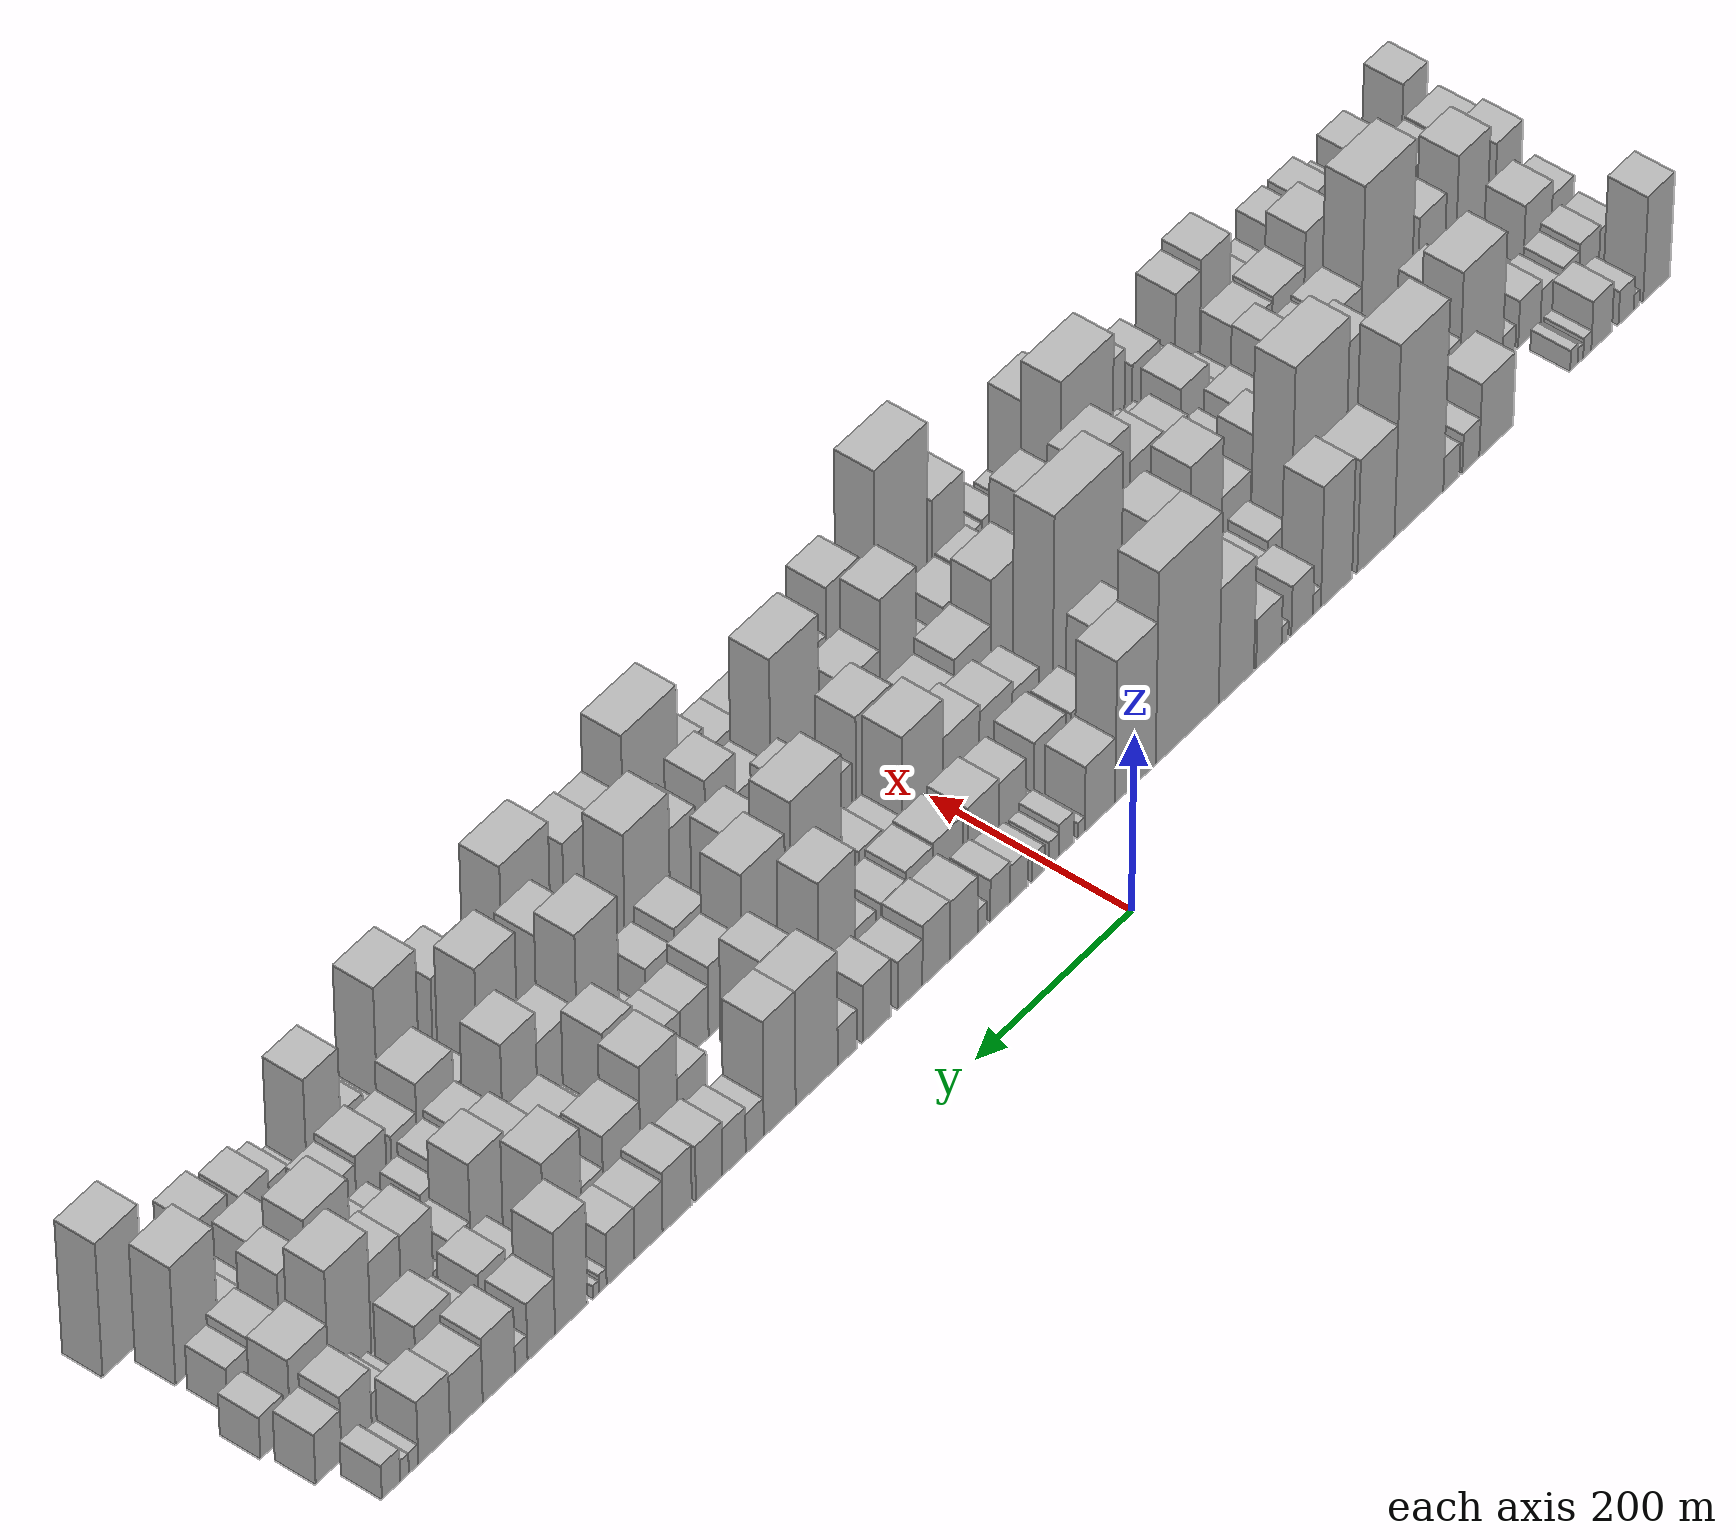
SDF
<sdf version="1.6">
 <world name="default">
  <scene>
   <sky><clouds><speed>12</speed></clouds></sky>
   <ambient>0.4 0.4 0.4 1</ambient>
   <background>0.7 0.7 0.7 1</background>
   <shadows>1</shadows>
  </scene>
  <gravity>0 0 -9.8066</gravity>
  <magnetic_field>6e-06 2.3e-05 -4.2e-05</magnetic_field>
  <physics default="0" name="default_physics" type="ode">
   <ode>
    <solver>
     <type>quick</type>
     <iters>10</iters>
     <sor>1.0</sor>
     <use_dynamic_moi_rescaling>0</use_dynamic_moi_rescaling>
    </solver>
    <constraints>
     <cfm>0</cfm>
     <erp>0.2</erp>
     <contact_max_correcting_vel>100</contact_max_correcting_vel>
     <contact_surface_layer>0.001</contact_surface_layer>
    </constraints>
   </ode>
   <max_step_size>0.004</max_step_size>
   <real_time_factor>1</real_time_factor>
   <real_time_update_rate>250</real_time_update_rate>
  </physics>
  <light name="sun" type="directional">
   <pose>0 0 10 0 0 0</pose>
   <diffuse>0.8 0.8 0.8 1</diffuse>
   <specular>0.2 0.2 0.2 1</specular>
   <attenuation>
    <range>1000</range>
    <constant>0.9</constant>
    <linear>0.01</linear>
    <quadratic>0.001</quadratic>
   </attenuation>
   <direction>-0.5 0.1 -0.9</direction>
  </light>
  <model name="building_1">
   <static>1</static>
   <pose>100.0000 -811.4164 0 0.000000 0.000000 0.000000</pose>
   <link name="link">
    <pose>0 0 60.00 0 0 0</pose>
    <collision name="collision"><geometry><box><size>40.0000 37.1672 120.0000</size></box></geometry></collision>
    <visual name="visual">
     <cast_shadows>0</cast_shadows>
     <geometry><box><size>40.0000 37.1672 120.0000</size></box></geometry>
     <material>
      <script>
       <uri>model://HANNAS_wall/materials/scripts</uri>
       <uri>model://HANNAS_wall/materials/textures</uri>
       <name>vrc/HANNAS_wall</name>
      </script>
     </material>
    </visual>
   </link>
  </model>
  <model name="building_2">
   <static>1</static>
   <pose>100.0000 -783.8636 0 0.000000 0.000000 0.000000</pose>
   <link name="link">
    <pose>0 0 9.00 0 0 0</pose>
    <collision name="collision"><geometry><box><size>40.0000 7.9383 18.0000</size></box></geometry></collision>
    <visual name="visual">
     <cast_shadows>0</cast_shadows>
     <geometry><box><size>40.0000 7.9383 18.0000</size></box></geometry>
     <material>
      <script>
       <uri>model://HANNAS_wall/materials/scripts</uri>
       <uri>model://HANNAS_wall/materials/textures</uri>
       <name>vrc/HANNAS_wall</name>
      </script>
     </material>
    </visual>
   </link>
  </model>
  <model name="building_3">
   <static>1</static>
   <pose>100.0000 -769.3108 0 0.000000 0.000000 0.000000</pose>
   <link name="link">
    <pose>0 0 19.50 0 0 0</pose>
    <collision name="collision"><geometry><box><size>40.0000 21.1674 39.0000</size></box></geometry></collision>
    <visual name="visual">
     <cast_shadows>0</cast_shadows>
     <geometry><box><size>40.0000 21.1674 39.0000</size></box></geometry>
     <material>
      <script>
       <uri>model://HANNAS_wall/materials/scripts</uri>
       <uri>model://HANNAS_wall/materials/textures</uri>
       <name>vrc/HANNAS_wall</name>
      </script>
     </material>
    </visual>
   </link>
  </model>
  <model name="building_4">
   <static>1</static>
   <pose>100.0000 -735.4422 0 0.000000 0.000000 0.000000</pose>
   <link name="link">
    <pose>0 0 28.50 0 0 0</pose>
    <collision name="collision"><geometry><box><size>40.0000 28.5698 57.0000</size></box></geometry></collision>
    <visual name="visual">
     <cast_shadows>0</cast_shadows>
     <geometry><box><size>40.0000 28.5698 57.0000</size></box></geometry>
     <material>
      <script>
       <uri>model://HANNAS_wall/materials/scripts</uri>
       <uri>model://HANNAS_wall/materials/textures</uri>
       <name>vrc/HANNAS_wall</name>
      </script>
     </material>
    </visual>
   </link>
  </model>
  <model name="building_5">
   <static>1</static>
   <pose>100.0000 -715.5884 0 0.000000 0.000000 0.000000</pose>
   <link name="link">
    <pose>0 0 12.00 0 0 0</pose>
    <collision name="collision"><geometry><box><size>40.0000 11.1378 24.0000</size></box></geometry></collision>
    <visual name="visual">
     <cast_shadows>0</cast_shadows>
     <geometry><box><size>40.0000 11.1378 24.0000</size></box></geometry>
     <material>
      <script>
       <uri>model://HANNAS_wall/materials/scripts</uri>
       <uri>model://HANNAS_wall/materials/textures</uri>
       <name>vrc/HANNAS_wall</name>
      </script>
     </material>
    </visual>
   </link>
  </model>
  <model name="building_6">
   <static>1</static>
   <pose>100.0000 -706.1968 0 0.000000 0.000000 0.000000</pose>
   <link name="link">
    <pose>0 0 9.00 0 0 0</pose>
    <collision name="collision"><geometry><box><size>40.0000 7.6454 18.0000</size></box></geometry></collision>
    <visual name="visual">
     <cast_shadows>0</cast_shadows>
     <geometry><box><size>40.0000 7.6454 18.0000</size></box></geometry>
     <material>
      <script>
       <uri>model://HANNAS_wall/materials/scripts</uri>
       <uri>model://HANNAS_wall/materials/textures</uri>
       <name>vrc/HANNAS_wall</name>
      </script>
     </material>
    </visual>
   </link>
  </model>
  <model name="building_7">
   <static>1</static>
   <pose>100.0000 -697.2363 0 0.000000 0.000000 0.000000</pose>
   <link name="link">
    <pose>0 0 12.00 0 0 0</pose>
    <collision name="collision"><geometry><box><size>40.0000 10.2755 24.0000</size></box></geometry></collision>
    <visual name="visual">
     <cast_shadows>0</cast_shadows>
     <geometry><box><size>40.0000 10.2755 24.0000</size></box></geometry>
     <material>
      <script>
       <uri>model://HANNAS_wall/materials/scripts</uri>
       <uri>model://HANNAS_wall/materials/textures</uri>
       <name>vrc/HANNAS_wall</name>
      </script>
     </material>
    </visual>
   </link>
  </model>
  <model name="building_8">
   <static>1</static>
   <pose>100.0000 -590.8446 0 0.000000 0.000000 0.000000</pose>
   <link name="link">
    <pose>0 0 42.00 0 0 0</pose>
    <collision name="collision"><geometry><box><size>40.0000 46.1693 84.0000</size></box></geometry></collision>
    <visual name="visual">
     <cast_shadows>0</cast_shadows>
     <geometry><box><size>40.0000 46.1693 84.0000</size></box></geometry>
     <material>
      <script>
       <uri>model://HANNAS_wall/materials/scripts</uri>
       <uri>model://HANNAS_wall/materials/textures</uri>
       <name>vrc/HANNAS_wall</name>
      </script>
     </material>
    </visual>
   </link>
  </model>
  <model name="building_9">
   <static>1</static>
   <pose>100.0000 -556.2142 0 0.000000 0.000000 0.000000</pose>
   <link name="link">
    <pose>0 0 22.50 0 0 0</pose>
    <collision name="collision"><geometry><box><size>40.0000 23.0915 45.0000</size></box></geometry></collision>
    <visual name="visual">
     <cast_shadows>0</cast_shadows>
     <geometry><box><size>40.0000 23.0915 45.0000</size></box></geometry>
     <material>
      <script>
       <uri>model://HANNAS_wall/materials/scripts</uri>
       <uri>model://HANNAS_wall/materials/textures</uri>
       <name>vrc/HANNAS_wall</name>
      </script>
     </material>
    </visual>
   </link>
  </model>
  <model name="building_10">
   <static>1</static>
   <pose>100.0000 -529.7747 0 0.000000 0.000000 0.000000</pose>
   <link name="link">
    <pose>0 0 19.50 0 0 0</pose>
    <collision name="collision"><geometry><box><size>40.0000 21.7876 39.0000</size></box></geometry></collision>
    <visual name="visual">
     <cast_shadows>0</cast_shadows>
     <geometry><box><size>40.0000 21.7876 39.0000</size></box></geometry>
     <material>
      <script>
       <uri>model://HANNAS_wall/materials/scripts</uri>
       <uri>model://HANNAS_wall/materials/textures</uri>
       <name>vrc/HANNAS_wall</name>
      </script>
     </material>
    </visual>
   </link>
  </model>
  <model name="building_11">
   <static>1</static>
   <pose>100.0000 -485.8917 0 0.000000 0.000000 0.000000</pose>
   <link name="link">
    <pose>0 0 109.50 0 0 0</pose>
    <collision name="collision"><geometry><box><size>40.0000 65.9784 219.0000</size></box></geometry></collision>
    <visual name="visual">
     <cast_shadows>0</cast_shadows>
     <geometry><box><size>40.0000 65.9784 219.0000</size></box></geometry>
     <material>
      <script>
       <uri>model://HANNAS_wall/materials/scripts</uri>
       <uri>model://HANNAS_wall/materials/textures</uri>
       <name>vrc/HANNAS_wall</name>
      </script>
     </material>
    </visual>
   </link>
  </model>
  <model name="building_12">
   <static>1</static>
   <pose>100.0000 -427.9507 0 0.000000 0.000000 0.000000</pose>
   <link name="link">
    <pose>0 0 64.50 0 0 0</pose>
    <collision name="collision"><geometry><box><size>40.0000 49.9035 129.0000</size></box></geometry></collision>
    <visual name="visual">
     <cast_shadows>0</cast_shadows>
     <geometry><box><size>40.0000 49.9035 129.0000</size></box></geometry>
     <material>
      <script>
       <uri>model://HANNAS_wall/materials/scripts</uri>
       <uri>model://HANNAS_wall/materials/textures</uri>
       <name>vrc/HANNAS_wall</name>
      </script>
     </material>
    </visual>
   </link>
  </model>
  <model name="building_13">
   <static>1</static>
   <pose>100.0000 -375.0913 0 0.000000 0.000000 0.000000</pose>
   <link name="link">
    <pose>0 0 69.00 0 0 0</pose>
    <collision name="collision"><geometry><box><size>40.0000 41.8153 138.0000</size></box></geometry></collision>
    <visual name="visual">
     <cast_shadows>0</cast_shadows>
     <geometry><box><size>40.0000 41.8153 138.0000</size></box></geometry>
     <material>
      <script>
       <uri>model://HANNAS_wall/materials/scripts</uri>
       <uri>model://HANNAS_wall/materials/textures</uri>
       <name>vrc/HANNAS_wall</name>
      </script>
     </material>
    </visual>
   </link>
  </model>
  <model name="building_14">
   <static>1</static>
   <pose>100.0000 -348.9207 0 0.000000 0.000000 0.000000</pose>
   <link name="link">
    <pose>0 0 12.00 0 0 0</pose>
    <collision name="collision"><geometry><box><size>40.0000 10.5259 24.0000</size></box></geometry></collision>
    <visual name="visual">
     <cast_shadows>0</cast_shadows>
     <geometry><box><size>40.0000 10.5259 24.0000</size></box></geometry>
     <material>
      <script>
       <uri>model://HANNAS_wall/materials/scripts</uri>
       <uri>model://HANNAS_wall/materials/textures</uri>
       <name>vrc/HANNAS_wall</name>
      </script>
     </material>
    </visual>
   </link>
  </model>
  <model name="building_15">
   <static>1</static>
   <pose>100.0000 -329.2720 0 0.000000 0.000000 0.000000</pose>
   <link name="link">
    <pose>0 0 28.50 0 0 0</pose>
    <collision name="collision"><geometry><box><size>40.0000 28.7715 57.0000</size></box></geometry></collision>
    <visual name="visual">
     <cast_shadows>0</cast_shadows>
     <geometry><box><size>40.0000 28.7715 57.0000</size></box></geometry>
     <material>
      <script>
       <uri>model://HANNAS_wall/materials/scripts</uri>
       <uri>model://HANNAS_wall/materials/textures</uri>
       <name>vrc/HANNAS_wall</name>
      </script>
     </material>
    </visual>
   </link>
  </model>
  <model name="building_16">
   <static>1</static>
   <pose>100.0000 -306.3816 0 0.000000 0.000000 0.000000</pose>
   <link name="link">
    <pose>0 0 10.50 0 0 0</pose>
    <collision name="collision"><geometry><box><size>40.0000 9.0092 21.0000</size></box></geometry></collision>
    <visual name="visual">
     <cast_shadows>0</cast_shadows>
     <geometry><box><size>40.0000 9.0092 21.0000</size></box></geometry>
     <material>
      <script>
       <uri>model://HANNAS_wall/materials/scripts</uri>
       <uri>model://HANNAS_wall/materials/textures</uri>
       <name>vrc/HANNAS_wall</name>
      </script>
     </material>
    </visual>
   </link>
  </model>
  <model name="building_17">
   <static>1</static>
   <pose>100.0000 -285.0486 0 0.000000 0.000000 0.000000</pose>
   <link name="link">
    <pose>0 0 28.50 0 0 0</pose>
    <collision name="collision"><geometry><box><size>40.0000 33.6569 57.0000</size></box></geometry></collision>
    <visual name="visual">
     <cast_shadows>0</cast_shadows>
     <geometry><box><size>40.0000 33.6569 57.0000</size></box></geometry>
     <material>
      <script>
       <uri>model://HANNAS_wall/materials/scripts</uri>
       <uri>model://HANNAS_wall/materials/textures</uri>
       <name>vrc/HANNAS_wall</name>
      </script>
     </material>
    </visual>
   </link>
  </model>
  <model name="building_18">
   <static>1</static>
   <pose>100.0000 -241.9831 0 0.000000 0.000000 0.000000</pose>
   <link name="link">
    <pose>0 0 66.00 0 0 0</pose>
    <collision name="collision"><geometry><box><size>40.0000 46.4741 132.0000</size></box></geometry></collision>
    <visual name="visual">
     <cast_shadows>0</cast_shadows>
     <geometry><box><size>40.0000 46.4741 132.0000</size></box></geometry>
     <material>
      <script>
       <uri>model://HANNAS_wall/materials/scripts</uri>
       <uri>model://HANNAS_wall/materials/textures</uri>
       <name>vrc/HANNAS_wall</name>
      </script>
     </material>
    </visual>
   </link>
  </model>
  <model name="building_19">
   <static>1</static>
   <pose>100.0000 -177.3380 0 0.000000 0.000000 0.000000</pose>
   <link name="link">
    <pose>0 0 109.50 0 0 0</pose>
    <collision name="collision"><geometry><box><size>40.0000 82.8162 219.0000</size></box></geometry></collision>
    <visual name="visual">
     <cast_shadows>0</cast_shadows>
     <geometry><box><size>40.0000 82.8162 219.0000</size></box></geometry>
     <material>
      <script>
       <uri>model://HANNAS_wall/materials/scripts</uri>
       <uri>model://HANNAS_wall/materials/textures</uri>
       <name>vrc/HANNAS_wall</name>
      </script>
     </material>
    </visual>
   </link>
  </model>
  <model name="building_20">
   <static>1</static>
   <pose>100.0000 -109.4534 0 0.000000 0.000000 0.000000</pose>
   <link name="link">
    <pose>0 0 81.00 0 0 0</pose>
    <collision name="collision"><geometry><box><size>40.0000 52.9530 162.0000</size></box></geometry></collision>
    <visual name="visual">
     <cast_shadows>0</cast_shadows>
     <geometry><box><size>40.0000 52.9530 162.0000</size></box></geometry>
     <material>
      <script>
       <uri>model://HANNAS_wall/materials/scripts</uri>
       <uri>model://HANNAS_wall/materials/textures</uri>
       <name>vrc/HANNAS_wall</name>
      </script>
     </material>
    </visual>
   </link>
  </model>
  <model name="building_21">
   <static>1</static>
   <pose>100.0000 -63.3266 0 0.000000 0.000000 0.000000</pose>
   <link name="link">
    <pose>0 0 37.50 0 0 0</pose>
    <collision name="collision"><geometry><box><size>40.0000 39.3005 75.0000</size></box></geometry></collision>
    <visual name="visual">
     <cast_shadows>0</cast_shadows>
     <geometry><box><size>40.0000 39.3005 75.0000</size></box></geometry>
     <material>
      <script>
       <uri>model://HANNAS_wall/materials/scripts</uri>
       <uri>model://HANNAS_wall/materials/textures</uri>
       <name>vrc/HANNAS_wall</name>
      </script>
     </material>
    </visual>
   </link>
  </model>
  <model name="building_22">
   <static>1</static>
   <pose>100.0000 -39.4577 0 0.000000 0.000000 0.000000</pose>
   <link name="link">
    <pose>0 0 9.00 0 0 0</pose>
    <collision name="collision"><geometry><box><size>40.0000 8.4373 18.0000</size></box></geometry></collision>
    <visual name="visual">
     <cast_shadows>0</cast_shadows>
     <geometry><box><size>40.0000 8.4373 18.0000</size></box></geometry>
     <material>
      <script>
       <uri>model://HANNAS_wall/materials/scripts</uri>
       <uri>model://HANNAS_wall/materials/textures</uri>
       <name>vrc/HANNAS_wall</name>
      </script>
     </material>
    </visual>
   </link>
  </model>
  <model name="building_23">
   <static>1</static>
   <pose>100.0000 -19.8759 0 0.000000 0.000000 0.000000</pose>
   <link name="link">
    <pose>0 0 18.00 0 0 0</pose>
    <collision name="collision"><geometry><box><size>40.0000 18.7263 36.0000</size></box></geometry></collision>
    <visual name="visual">
     <cast_shadows>0</cast_shadows>
     <geometry><box><size>40.0000 18.7263 36.0000</size></box></geometry>
     <material>
      <script>
       <uri>model://HANNAS_wall/materials/scripts</uri>
       <uri>model://HANNAS_wall/materials/textures</uri>
       <name>vrc/HANNAS_wall</name>
      </script>
     </material>
    </visual>
   </link>
  </model>
  <model name="building_24">
   <static>1</static>
   <pose>100.0000 -4.0476 0 0.000000 0.000000 0.000000</pose>
   <link name="link">
    <pose>0 0 13.50 0 0 0</pose>
    <collision name="collision"><geometry><box><size>40.0000 12.9304 27.0000</size></box></geometry></collision>
    <visual name="visual">
     <cast_shadows>0</cast_shadows>
     <geometry><box><size>40.0000 12.9304 27.0000</size></box></geometry>
     <material>
      <script>
       <uri>model://HANNAS_wall/materials/scripts</uri>
       <uri>model://HANNAS_wall/materials/textures</uri>
       <name>vrc/HANNAS_wall</name>
      </script>
     </material>
    </visual>
   </link>
  </model>
  <model name="building_25">
   <static>1</static>
   <pose>100.0000 16.3489 0 0.000000 0.000000 0.000000</pose>
   <link name="link">
    <pose>0 0 15.00 0 0 0</pose>
    <collision name="collision"><geometry><box><size>40.0000 15.8626 30.0000</size></box></geometry></collision>
    <visual name="visual">
     <cast_shadows>0</cast_shadows>
     <geometry><box><size>40.0000 15.8626 30.0000</size></box></geometry>
     <material>
      <script>
       <uri>model://HANNAS_wall/materials/scripts</uri>
       <uri>model://HANNAS_wall/materials/textures</uri>
       <name>vrc/HANNAS_wall</name>
      </script>
     </material>
    </visual>
   </link>
  </model>
  <model name="building_26">
   <static>1</static>
   <pose>100.0000 40.9273 0 0.000000 0.000000 0.000000</pose>
   <link name="link">
    <pose>0 0 21.00 0 0 0</pose>
    <collision name="collision"><geometry><box><size>40.0000 23.2941 42.0000</size></box></geometry></collision>
    <visual name="visual">
     <cast_shadows>0</cast_shadows>
     <geometry><box><size>40.0000 23.2941 42.0000</size></box></geometry>
     <material>
      <script>
       <uri>model://HANNAS_wall/materials/scripts</uri>
       <uri>model://HANNAS_wall/materials/textures</uri>
       <name>vrc/HANNAS_wall</name>
      </script>
     </material>
    </visual>
   </link>
  </model>
  <model name="building_27">
   <static>1</static>
   <pose>100.0000 65.3385 0 0.000000 0.000000 0.000000</pose>
   <link name="link">
    <pose>0 0 24.00 0 0 0</pose>
    <collision name="collision"><geometry><box><size>40.0000 25.5284 48.0000</size></box></geometry></collision>
    <visual name="visual">
     <cast_shadows>0</cast_shadows>
     <geometry><box><size>40.0000 25.5284 48.0000</size></box></geometry>
     <material>
      <script>
       <uri>model://HANNAS_wall/materials/scripts</uri>
       <uri>model://HANNAS_wall/materials/textures</uri>
       <name>vrc/HANNAS_wall</name>
      </script>
     </material>
    </visual>
   </link>
  </model>
  <model name="building_28">
   <static>1</static>
   <pose>100.0000 88.1129 0 0.000000 0.000000 0.000000</pose>
   <link name="link">
    <pose>0 0 13.50 0 0 0</pose>
    <collision name="collision"><geometry><box><size>40.0000 12.0204 27.0000</size></box></geometry></collision>
    <visual name="visual">
     <cast_shadows>0</cast_shadows>
     <geometry><box><size>40.0000 12.0204 27.0000</size></box></geometry>
     <material>
      <script>
       <uri>model://HANNAS_wall/materials/scripts</uri>
       <uri>model://HANNAS_wall/materials/textures</uri>
       <name>vrc/HANNAS_wall</name>
      </script>
     </material>
    </visual>
   </link>
  </model>
  <model name="building_29">
   <static>1</static>
   <pose>100.0000 112.0169 0 0.000000 0.000000 0.000000</pose>
   <link name="link">
    <pose>0 0 33.00 0 0 0</pose>
    <collision name="collision"><geometry><box><size>40.0000 35.7874 66.0000</size></box></geometry></collision>
    <visual name="visual">
     <cast_shadows>0</cast_shadows>
     <geometry><box><size>40.0000 35.7874 66.0000</size></box></geometry>
     <material>
      <script>
       <uri>model://HANNAS_wall/materials/scripts</uri>
       <uri>model://HANNAS_wall/materials/textures</uri>
       <name>vrc/HANNAS_wall</name>
      </script>
     </material>
    </visual>
   </link>
  </model>
  <model name="building_30">
   <static>1</static>
   <pose>100.0000 147.3166 0 0.000000 0.000000 0.000000</pose>
   <link name="link">
    <pose>0 0 34.50 0 0 0</pose>
    <collision name="collision"><geometry><box><size>40.0000 34.8121 69.0000</size></box></geometry></collision>
    <visual name="visual">
     <cast_shadows>0</cast_shadows>
     <geometry><box><size>40.0000 34.8121 69.0000</size></box></geometry>
     <material>
      <script>
       <uri>model://HANNAS_wall/materials/scripts</uri>
       <uri>model://HANNAS_wall/materials/textures</uri>
       <name>vrc/HANNAS_wall</name>
      </script>
     </material>
    </visual>
   </link>
  </model>
  <model name="building_31">
   <static>1</static>
   <pose>100.0000 180.0864 0 0.000000 0.000000 0.000000</pose>
   <link name="link">
    <pose>0 0 27.00 0 0 0</pose>
    <collision name="collision"><geometry><box><size>40.0000 30.7275 54.0000</size></box></geometry></collision>
    <visual name="visual">
     <cast_shadows>0</cast_shadows>
     <geometry><box><size>40.0000 30.7275 54.0000</size></box></geometry>
     <material>
      <script>
       <uri>model://HANNAS_wall/materials/scripts</uri>
       <uri>model://HANNAS_wall/materials/textures</uri>
       <name>vrc/HANNAS_wall</name>
      </script>
     </material>
    </visual>
   </link>
  </model>
  <model name="building_32">
   <static>1</static>
   <pose>100.0000 222.3811 0 0.000000 0.000000 0.000000</pose>
   <link name="link">
    <pose>0 0 33.00 0 0 0</pose>
    <collision name="collision"><geometry><box><size>40.0000 35.8618 66.0000</size></box></geometry></collision>
    <visual name="visual">
     <cast_shadows>0</cast_shadows>
     <geometry><box><size>40.0000 35.8618 66.0000</size></box></geometry>
     <material>
      <script>
       <uri>model://HANNAS_wall/materials/scripts</uri>
       <uri>model://HANNAS_wall/materials/textures</uri>
       <name>vrc/HANNAS_wall</name>
      </script>
     </material>
    </visual>
   </link>
  </model>
  <model name="building_33">
   <static>1</static>
   <pose>100.0000 259.6715 0 0.000000 0.000000 0.000000</pose>
   <link name="link">
    <pose>0 0 22.50 0 0 0</pose>
    <collision name="collision"><geometry><box><size>40.0000 24.7191 45.0000</size></box></geometry></collision>
    <visual name="visual">
     <cast_shadows>0</cast_shadows>
     <geometry><box><size>40.0000 24.7191 45.0000</size></box></geometry>
     <material>
      <script>
       <uri>model://HANNAS_wall/materials/scripts</uri>
       <uri>model://HANNAS_wall/materials/textures</uri>
       <name>vrc/HANNAS_wall</name>
      </script>
     </material>
    </visual>
   </link>
  </model>
  <model name="building_34">
   <static>1</static>
   <pose>100.0000 298.4205 0 0.000000 0.000000 0.000000</pose>
   <link name="link">
    <pose>0 0 66.00 0 0 0</pose>
    <collision name="collision"><geometry><box><size>40.0000 52.7788 132.0000</size></box></geometry></collision>
    <visual name="visual">
     <cast_shadows>0</cast_shadows>
     <geometry><box><size>40.0000 52.7788 132.0000</size></box></geometry>
     <material>
      <script>
       <uri>model://HANNAS_wall/materials/scripts</uri>
       <uri>model://HANNAS_wall/materials/textures</uri>
       <name>vrc/HANNAS_wall</name>
      </script>
     </material>
    </visual>
   </link>
  </model>
  <model name="building_35">
   <static>1</static>
   <pose>100.0000 344.7468 0 0.000000 0.000000 0.000000</pose>
   <link name="link">
    <pose>0 0 66.00 0 0 0</pose>
    <collision name="collision"><geometry><box><size>40.0000 39.8739 132.0000</size></box></geometry></collision>
    <visual name="visual">
     <cast_shadows>0</cast_shadows>
     <geometry><box><size>40.0000 39.8739 132.0000</size></box></geometry>
     <material>
      <script>
       <uri>model://HANNAS_wall/materials/scripts</uri>
       <uri>model://HANNAS_wall/materials/textures</uri>
       <name>vrc/HANNAS_wall</name>
      </script>
     </material>
    </visual>
   </link>
  </model>
  <model name="building_36">
   <static>1</static>
   <pose>100.0000 375.9424 0 0.000000 0.000000 0.000000</pose>
   <link name="link">
    <pose>0 0 22.50 0 0 0</pose>
    <collision name="collision"><geometry><box><size>40.0000 22.5172 45.0000</size></box></geometry></collision>
    <visual name="visual">
     <cast_shadows>0</cast_shadows>
     <geometry><box><size>40.0000 22.5172 45.0000</size></box></geometry>
     <material>
      <script>
       <uri>model://HANNAS_wall/materials/scripts</uri>
       <uri>model://HANNAS_wall/materials/textures</uri>
       <name>vrc/HANNAS_wall</name>
      </script>
     </material>
    </visual>
   </link>
  </model>
  <model name="building_37">
   <static>1</static>
   <pose>100.0000 401.6316 0 0.000000 0.000000 0.000000</pose>
   <link name="link">
    <pose>0 0 27.00 0 0 0</pose>
    <collision name="collision"><geometry><box><size>40.0000 28.8611 54.0000</size></box></geometry></collision>
    <visual name="visual">
     <cast_shadows>0</cast_shadows>
     <geometry><box><size>40.0000 28.8611 54.0000</size></box></geometry>
     <material>
      <script>
       <uri>model://HANNAS_wall/materials/scripts</uri>
       <uri>model://HANNAS_wall/materials/textures</uri>
       <name>vrc/HANNAS_wall</name>
      </script>
     </material>
    </visual>
   </link>
  </model>
  <model name="building_38">
   <static>1</static>
   <pose>100.0000 432.5570 0 0.000000 0.000000 0.000000</pose>
   <link name="link">
    <pose>0 0 31.50 0 0 0</pose>
    <collision name="collision"><geometry><box><size>40.0000 32.9896 63.0000</size></box></geometry></collision>
    <visual name="visual">
     <cast_shadows>0</cast_shadows>
     <geometry><box><size>40.0000 32.9896 63.0000</size></box></geometry>
     <material>
      <script>
       <uri>model://HANNAS_wall/materials/scripts</uri>
       <uri>model://HANNAS_wall/materials/textures</uri>
       <name>vrc/HANNAS_wall</name>
      </script>
     </material>
    </visual>
   </link>
  </model>
  <model name="building_39">
   <static>1</static>
   <pose>100.0000 472.1289 0 0.000000 0.000000 0.000000</pose>
   <link name="link">
    <pose>0 0 34.50 0 0 0</pose>
    <collision name="collision"><geometry><box><size>40.0000 36.1542 69.0000</size></box></geometry></collision>
    <visual name="visual">
     <cast_shadows>0</cast_shadows>
     <geometry><box><size>40.0000 36.1542 69.0000</size></box></geometry>
     <material>
      <script>
       <uri>model://HANNAS_wall/materials/scripts</uri>
       <uri>model://HANNAS_wall/materials/textures</uri>
       <name>vrc/HANNAS_wall</name>
      </script>
     </material>
    </visual>
   </link>
  </model>
  <model name="building_40">
   <static>1</static>
   <pose>100.0000 507.4661 0 0.000000 0.000000 0.000000</pose>
   <link name="link">
    <pose>0 0 30.00 0 0 0</pose>
    <collision name="collision"><geometry><box><size>40.0000 34.5202 60.0000</size></box></geometry></collision>
    <visual name="visual">
     <cast_shadows>0</cast_shadows>
     <geometry><box><size>40.0000 34.5202 60.0000</size></box></geometry>
     <material>
      <script>
       <uri>model://HANNAS_wall/materials/scripts</uri>
       <uri>model://HANNAS_wall/materials/textures</uri>
       <name>vrc/HANNAS_wall</name>
      </script>
     </material>
    </visual>
   </link>
  </model>
  <model name="building_41">
   <static>1</static>
   <pose>100.0000 541.8242 0 0.000000 0.000000 0.000000</pose>
   <link name="link">
    <pose>0 0 30.00 0 0 0</pose>
    <collision name="collision"><geometry><box><size>40.0000 34.1960 60.0000</size></box></geometry></collision>
    <visual name="visual">
     <cast_shadows>0</cast_shadows>
     <geometry><box><size>40.0000 34.1960 60.0000</size></box></geometry>
     <material>
      <script>
       <uri>model://HANNAS_wall/materials/scripts</uri>
       <uri>model://HANNAS_wall/materials/textures</uri>
       <name>vrc/HANNAS_wall</name>
      </script>
     </material>
    </visual>
   </link>
  </model>
  <model name="building_42">
   <static>1</static>
   <pose>100.0000 563.6817 0 0.000000 0.000000 0.000000</pose>
   <link name="link">
    <pose>0 0 10.50 0 0 0</pose>
    <collision name="collision"><geometry><box><size>40.0000 9.5190 21.0000</size></box></geometry></collision>
    <visual name="visual">
     <cast_shadows>0</cast_shadows>
     <geometry><box><size>40.0000 9.5190 21.0000</size></box></geometry>
     <material>
      <script>
       <uri>model://HANNAS_wall/materials/scripts</uri>
       <uri>model://HANNAS_wall/materials/textures</uri>
       <name>vrc/HANNAS_wall</name>
      </script>
     </material>
    </visual>
   </link>
  </model>
  <model name="building_43">
   <static>1</static>
   <pose>100.0000 571.8710 0 0.000000 0.000000 0.000000</pose>
   <link name="link">
    <pose>0 0 7.50 0 0 0</pose>
    <collision name="collision"><geometry><box><size>40.0000 6.8597 15.0000</size></box></geometry></collision>
    <visual name="visual">
     <cast_shadows>0</cast_shadows>
     <geometry><box><size>40.0000 6.8597 15.0000</size></box></geometry>
     <material>
      <script>
       <uri>model://HANNAS_wall/materials/scripts</uri>
       <uri>model://HANNAS_wall/materials/textures</uri>
       <name>vrc/HANNAS_wall</name>
      </script>
     </material>
    </visual>
   </link>
  </model>
  <model name="building_44">
   <static>1</static>
   <pose>100.0000 602.0692 0 0.000000 0.000000 0.000000</pose>
   <link name="link">
    <pose>0 0 58.50 0 0 0</pose>
    <collision name="collision"><geometry><box><size>40.0000 39.5367 117.0000</size></box></geometry></collision>
    <visual name="visual">
     <cast_shadows>0</cast_shadows>
     <geometry><box><size>40.0000 39.5367 117.0000</size></box></geometry>
     <material>
      <script>
       <uri>model://HANNAS_wall/materials/scripts</uri>
       <uri>model://HANNAS_wall/materials/textures</uri>
       <name>vrc/HANNAS_wall</name>
      </script>
     </material>
    </visual>
   </link>
  </model>
  <model name="building_45">
   <static>1</static>
   <pose>100.0000 638.5882 0 0.000000 0.000000 0.000000</pose>
   <link name="link">
    <pose>0 0 33.00 0 0 0</pose>
    <collision name="collision"><geometry><box><size>40.0000 33.5014 66.0000</size></box></geometry></collision>
    <visual name="visual">
     <cast_shadows>0</cast_shadows>
     <geometry><box><size>40.0000 33.5014 66.0000</size></box></geometry>
     <material>
      <script>
       <uri>model://HANNAS_wall/materials/scripts</uri>
       <uri>model://HANNAS_wall/materials/textures</uri>
       <name>vrc/HANNAS_wall</name>
      </script>
     </material>
    </visual>
   </link>
  </model>
  <model name="building_46">
   <static>1</static>
   <pose>100.0000 662.9354 0 0.000000 0.000000 0.000000</pose>
   <link name="link">
    <pose>0 0 15.00 0 0 0</pose>
    <collision name="collision"><geometry><box><size>40.0000 15.1930 30.0000</size></box></geometry></collision>
    <visual name="visual">
     <cast_shadows>0</cast_shadows>
     <geometry><box><size>40.0000 15.1930 30.0000</size></box></geometry>
     <material>
      <script>
       <uri>model://HANNAS_wall/materials/scripts</uri>
       <uri>model://HANNAS_wall/materials/textures</uri>
       <name>vrc/HANNAS_wall</name>
      </script>
     </material>
    </visual>
   </link>
  </model>
  <model name="building_47">
   <static>1</static>
   <pose>100.0000 690.0562 0 0.000000 0.000000 0.000000</pose>
   <link name="link">
    <pose>0 0 37.50 0 0 0</pose>
    <collision name="collision"><geometry><box><size>40.0000 39.0487 75.0000</size></box></geometry></collision>
    <visual name="visual">
     <cast_shadows>0</cast_shadows>
     <geometry><box><size>40.0000 39.0487 75.0000</size></box></geometry>
     <material>
      <script>
       <uri>model://HANNAS_wall/materials/scripts</uri>
       <uri>model://HANNAS_wall/materials/textures</uri>
       <name>vrc/HANNAS_wall</name>
      </script>
     </material>
    </visual>
   </link>
  </model>
  <model name="building_48">
   <static>1</static>
   <pose>100.0000 729.2057 0 0.000000 0.000000 0.000000</pose>
   <link name="link">
    <pose>0 0 33.00 0 0 0</pose>
    <collision name="collision"><geometry><box><size>40.0000 39.2503 66.0000</size></box></geometry></collision>
    <visual name="visual">
     <cast_shadows>0</cast_shadows>
     <geometry><box><size>40.0000 39.2503 66.0000</size></box></geometry>
     <material>
      <script>
       <uri>model://HANNAS_wall/materials/scripts</uri>
       <uri>model://HANNAS_wall/materials/textures</uri>
       <name>vrc/HANNAS_wall</name>
      </script>
     </material>
    </visual>
   </link>
  </model>
  <model name="building_49">
   <static>1</static>
   <pose>100.0000 767.9527 0 0.000000 0.000000 0.000000</pose>
   <link name="link">
    <pose>0 0 36.00 0 0 0</pose>
    <collision name="collision"><geometry><box><size>40.0000 38.2437 72.0000</size></box></geometry></collision>
    <visual name="visual">
     <cast_shadows>0</cast_shadows>
     <geometry><box><size>40.0000 38.2437 72.0000</size></box></geometry>
     <material>
      <script>
       <uri>model://HANNAS_wall/materials/scripts</uri>
       <uri>model://HANNAS_wall/materials/textures</uri>
       <name>vrc/HANNAS_wall</name>
      </script>
     </material>
    </visual>
   </link>
  </model>
  <model name="building_50">
   <static>1</static>
   <pose>100.0000 792.7380 0 0.000000 0.000000 0.000000</pose>
   <link name="link">
    <pose>0 0 12.00 0 0 0</pose>
    <collision name="collision"><geometry><box><size>40.0000 11.3270 24.0000</size></box></geometry></collision>
    <visual name="visual">
     <cast_shadows>0</cast_shadows>
     <geometry><box><size>40.0000 11.3270 24.0000</size></box></geometry>
     <material>
      <script>
       <uri>model://HANNAS_wall/materials/scripts</uri>
       <uri>model://HANNAS_wall/materials/textures</uri>
       <name>vrc/HANNAS_wall</name>
      </script>
     </material>
    </visual>
   </link>
  </model>
  <model name="building_51">
   <static>1</static>
   <pose>100.0000 803.5421 0 0.000000 0.000000 0.000000</pose>
   <link name="link">
    <pose>0 0 12.00 0 0 0</pose>
    <collision name="collision"><geometry><box><size>40.0000 10.2812 24.0000</size></box></geometry></collision>
    <visual name="visual">
     <cast_shadows>0</cast_shadows>
     <geometry><box><size>40.0000 10.2812 24.0000</size></box></geometry>
     <material>
      <script>
       <uri>model://HANNAS_wall/materials/scripts</uri>
       <uri>model://HANNAS_wall/materials/textures</uri>
       <name>vrc/HANNAS_wall</name>
      </script>
     </material>
    </visual>
   </link>
  </model>
  <model name="building_52">
   <static>1</static>
   <pose>100.0000 819.6766 0 0.000000 0.000000 0.000000</pose>
   <link name="link">
    <pose>0 0 19.50 0 0 0</pose>
    <collision name="collision"><geometry><box><size>40.0000 21.9879 39.0000</size></box></geometry></collision>
    <visual name="visual">
     <cast_shadows>0</cast_shadows>
     <geometry><box><size>40.0000 21.9879 39.0000</size></box></geometry>
     <material>
      <script>
       <uri>model://HANNAS_wall/materials/scripts</uri>
       <uri>model://HANNAS_wall/materials/textures</uri>
       <name>vrc/HANNAS_wall</name>
      </script>
     </material>
    </visual>
   </link>
  </model>
  <model name="building_53">
   <static>1</static>
   <pose>149.0000 -811.8645 0 0.000000 0.000000 0.000000</pose>
   <link name="link">
    <pose>0 0 24.00 0 0 0</pose>
    <collision name="collision"><geometry><box><size>40.0000 26.2711 48.0000</size></box></geometry></collision>
    <visual name="visual">
     <cast_shadows>0</cast_shadows>
     <geometry><box><size>40.0000 26.2711 48.0000</size></box></geometry>
     <material>
      <script>
       <uri>model://HANNAS_wall/materials/scripts</uri>
       <uri>model://HANNAS_wall/materials/textures</uri>
       <name>vrc/HANNAS_wall</name>
      </script>
     </material>
    </visual>
   </link>
  </model>
  <model name="building_54">
   <static>1</static>
   <pose>149.0000 -784.7413 0 0.000000 0.000000 0.000000</pose>
   <link name="link">
    <pose>0 0 27.00 0 0 0</pose>
    <collision name="collision"><geometry><box><size>40.0000 27.9752 54.0000</size></box></geometry></collision>
    <visual name="visual">
     <cast_shadows>0</cast_shadows>
     <geometry><box><size>40.0000 27.9752 54.0000</size></box></geometry>
     <material>
      <script>
       <uri>model://HANNAS_wall/materials/scripts</uri>
       <uri>model://HANNAS_wall/materials/textures</uri>
       <name>vrc/HANNAS_wall</name>
      </script>
     </material>
    </visual>
   </link>
  </model>
  <model name="building_55">
   <static>1</static>
   <pose>149.0000 -759.3443 0 0.000000 0.000000 0.000000</pose>
   <link name="link">
    <pose>0 0 22.50 0 0 0</pose>
    <collision name="collision"><geometry><box><size>40.0000 22.8188 45.0000</size></box></geometry></collision>
    <visual name="visual">
     <cast_shadows>0</cast_shadows>
     <geometry><box><size>40.0000 22.8188 45.0000</size></box></geometry>
     <material>
      <script>
       <uri>model://HANNAS_wall/materials/scripts</uri>
       <uri>model://HANNAS_wall/materials/textures</uri>
       <name>vrc/HANNAS_wall</name>
      </script>
     </material>
    </visual>
   </link>
  </model>
  <model name="building_56">
   <static>1</static>
   <pose>149.0000 -730.1455 0 0.000000 0.000000 0.000000</pose>
   <link name="link">
    <pose>0 0 21.00 0 0 0</pose>
    <collision name="collision"><geometry><box><size>40.0000 23.5788 42.0000</size></box></geometry></collision>
    <visual name="visual">
     <cast_shadows>0</cast_shadows>
     <geometry><box><size>40.0000 23.5788 42.0000</size></box></geometry>
     <material>
      <script>
       <uri>model://HANNAS_wall/materials/scripts</uri>
       <uri>model://HANNAS_wall/materials/textures</uri>
       <name>vrc/HANNAS_wall</name>
      </script>
     </material>
    </visual>
   </link>
  </model>
  <model name="building_57">
   <static>1</static>
   <pose>149.0000 -703.0242 0 0.000000 0.000000 0.000000</pose>
   <link name="link">
    <pose>0 0 27.00 0 0 0</pose>
    <collision name="collision"><geometry><box><size>40.0000 30.6639 54.0000</size></box></geometry></collision>
    <visual name="visual">
     <cast_shadows>0</cast_shadows>
     <geometry><box><size>40.0000 30.6639 54.0000</size></box></geometry>
     <material>
      <script>
       <uri>model://HANNAS_wall/materials/scripts</uri>
       <uri>model://HANNAS_wall/materials/textures</uri>
       <name>vrc/HANNAS_wall</name>
      </script>
     </material>
    </visual>
   </link>
  </model>
  <model name="building_58">
   <static>1</static>
   <pose>149.0000 -674.7201 0 0.000000 0.000000 0.000000</pose>
   <link name="link">
    <pose>0 0 15.00 0 0 0</pose>
    <collision name="collision"><geometry><box><size>40.0000 17.9442 30.0000</size></box></geometry></collision>
    <visual name="visual">
     <cast_shadows>0</cast_shadows>
     <geometry><box><size>40.0000 17.9442 30.0000</size></box></geometry>
     <material>
      <script>
       <uri>model://HANNAS_wall/materials/scripts</uri>
       <uri>model://HANNAS_wall/materials/textures</uri>
       <name>vrc/HANNAS_wall</name>
      </script>
     </material>
    </visual>
   </link>
  </model>
  <model name="building_59">
   <static>1</static>
   <pose>149.0000 -636.1037 0 0.000000 0.000000 0.000000</pose>
   <link name="link">
    <pose>0 0 75.00 0 0 0</pose>
    <collision name="collision"><geometry><box><size>40.0000 59.2884 150.0000</size></box></geometry></collision>
    <visual name="visual">
     <cast_shadows>0</cast_shadows>
     <geometry><box><size>40.0000 59.2884 150.0000</size></box></geometry>
     <material>
      <script>
       <uri>model://HANNAS_wall/materials/scripts</uri>
       <uri>model://HANNAS_wall/materials/textures</uri>
       <name>vrc/HANNAS_wall</name>
      </script>
     </material>
    </visual>
   </link>
  </model>
  <model name="building_60">
   <static>1</static>
   <pose>149.0000 -584.9677 0 0.000000 0.000000 0.000000</pose>
   <link name="link">
    <pose>0 0 37.50 0 0 0</pose>
    <collision name="collision"><geometry><box><size>40.0000 42.9836 75.0000</size></box></geometry></collision>
    <visual name="visual">
     <cast_shadows>0</cast_shadows>
     <geometry><box><size>40.0000 42.9836 75.0000</size></box></geometry>
     <material>
      <script>
       <uri>model://HANNAS_wall/materials/scripts</uri>
       <uri>model://HANNAS_wall/materials/textures</uri>
       <name>vrc/HANNAS_wall</name>
      </script>
     </material>
    </visual>
   </link>
  </model>
  <model name="building_61">
   <static>1</static>
   <pose>149.0000 -492.4160 0 0.000000 0.000000 0.000000</pose>
   <link name="link">
    <pose>0 0 21.00 0 0 0</pose>
    <collision name="collision"><geometry><box><size>40.0000 24.7066 42.0000</size></box></geometry></collision>
    <visual name="visual">
     <cast_shadows>0</cast_shadows>
     <geometry><box><size>40.0000 24.7066 42.0000</size></box></geometry>
     <material>
      <script>
       <uri>model://HANNAS_wall/materials/scripts</uri>
       <uri>model://HANNAS_wall/materials/textures</uri>
       <name>vrc/HANNAS_wall</name>
      </script>
     </material>
    </visual>
   </link>
  </model>
  <model name="building_62">
   <static>1</static>
   <pose>149.0000 -465.7952 0 0.000000 0.000000 0.000000</pose>
   <link name="link">
    <pose>0 0 28.50 0 0 0</pose>
    <collision name="collision"><geometry><box><size>40.0000 28.5350 57.0000</size></box></geometry></collision>
    <visual name="visual">
     <cast_shadows>0</cast_shadows>
     <geometry><box><size>40.0000 28.5350 57.0000</size></box></geometry>
     <material>
      <script>
       <uri>model://HANNAS_wall/materials/scripts</uri>
       <uri>model://HANNAS_wall/materials/textures</uri>
       <name>vrc/HANNAS_wall</name>
      </script>
     </material>
    </visual>
   </link>
  </model>
  <model name="building_63">
   <static>1</static>
   <pose>149.0000 -415.2956 0 0.000000 0.000000 0.000000</pose>
   <link name="link">
    <pose>0 0 111.00 0 0 0</pose>
    <collision name="collision"><geometry><box><size>40.0000 72.4643 222.0000</size></box></geometry></collision>
    <visual name="visual">
     <cast_shadows>0</cast_shadows>
     <geometry><box><size>40.0000 72.4643 222.0000</size></box></geometry>
     <material>
      <script>
       <uri>model://HANNAS_wall/materials/scripts</uri>
       <uri>model://HANNAS_wall/materials/textures</uri>
       <name>vrc/HANNAS_wall</name>
      </script>
     </material>
    </visual>
   </link>
  </model>
  <model name="building_64">
   <static>1</static>
   <pose>149.0000 -361.4305 0 0.000000 0.000000 0.000000</pose>
   <link name="link">
    <pose>0 0 25.50 0 0 0</pose>
    <collision name="collision"><geometry><box><size>40.0000 27.2659 51.0000</size></box></geometry></collision>
    <visual name="visual">
     <cast_shadows>0</cast_shadows>
     <geometry><box><size>40.0000 27.2659 51.0000</size></box></geometry>
     <material>
      <script>
       <uri>model://HANNAS_wall/materials/scripts</uri>
       <uri>model://HANNAS_wall/materials/textures</uri>
       <name>vrc/HANNAS_wall</name>
      </script>
     </material>
    </visual>
   </link>
  </model>
  <model name="building_65">
   <static>1</static>
   <pose>149.0000 -336.2556 0 0.000000 0.000000 0.000000</pose>
   <link name="link">
    <pose>0 0 19.50 0 0 0</pose>
    <collision name="collision"><geometry><box><size>40.0000 23.0838 39.0000</size></box></geometry></collision>
    <visual name="visual">
     <cast_shadows>0</cast_shadows>
     <geometry><box><size>40.0000 23.0838 39.0000</size></box></geometry>
     <material>
      <script>
       <uri>model://HANNAS_wall/materials/scripts</uri>
       <uri>model://HANNAS_wall/materials/textures</uri>
       <name>vrc/HANNAS_wall</name>
      </script>
     </material>
    </visual>
   </link>
  </model>
  <model name="building_66">
   <static>1</static>
   <pose>149.0000 -312.7713 0 0.000000 0.000000 0.000000</pose>
   <link name="link">
    <pose>0 0 22.50 0 0 0</pose>
    <collision name="collision"><geometry><box><size>40.0000 23.8847 45.0000</size></box></geometry></collision>
    <visual name="visual">
     <cast_shadows>0</cast_shadows>
     <geometry><box><size>40.0000 23.8847 45.0000</size></box></geometry>
     <material>
      <script>
       <uri>model://HANNAS_wall/materials/scripts</uri>
       <uri>model://HANNAS_wall/materials/textures</uri>
       <name>vrc/HANNAS_wall</name>
      </script>
     </material>
    </visual>
   </link>
  </model>
  <model name="building_67">
   <static>1</static>
   <pose>149.0000 -275.8887 0 0.000000 0.000000 0.000000</pose>
   <link name="link">
    <pose>0 0 28.50 0 0 0</pose>
    <collision name="collision"><geometry><box><size>40.0000 29.8805 57.0000</size></box></geometry></collision>
    <visual name="visual">
     <cast_shadows>0</cast_shadows>
     <geometry><box><size>40.0000 29.8805 57.0000</size></box></geometry>
     <material>
      <script>
       <uri>model://HANNAS_wall/materials/scripts</uri>
       <uri>model://HANNAS_wall/materials/textures</uri>
       <name>vrc/HANNAS_wall</name>
      </script>
     </material>
    </visual>
   </link>
  </model>
  <model name="building_68">
   <static>1</static>
   <pose>149.0000 -236.1031 0 0.000000 0.000000 0.000000</pose>
   <link name="link">
    <pose>0 0 36.00 0 0 0</pose>
    <collision name="collision"><geometry><box><size>40.0000 39.6908 72.0000</size></box></geometry></collision>
    <visual name="visual">
     <cast_shadows>0</cast_shadows>
     <geometry><box><size>40.0000 39.6908 72.0000</size></box></geometry>
     <material>
      <script>
       <uri>model://HANNAS_wall/materials/scripts</uri>
       <uri>model://HANNAS_wall/materials/textures</uri>
       <name>vrc/HANNAS_wall</name>
      </script>
     </material>
    </visual>
   </link>
  </model>
  <model name="building_69">
   <static>1</static>
   <pose>149.0000 -201.3836 0 0.000000 0.000000 0.000000</pose>
   <link name="link">
    <pose>0 0 25.50 0 0 0</pose>
    <collision name="collision"><geometry><box><size>40.0000 29.7481 51.0000</size></box></geometry></collision>
    <visual name="visual">
     <cast_shadows>0</cast_shadows>
     <geometry><box><size>40.0000 29.7481 51.0000</size></box></geometry>
     <material>
      <script>
       <uri>model://HANNAS_wall/materials/scripts</uri>
       <uri>model://HANNAS_wall/materials/textures</uri>
       <name>vrc/HANNAS_wall</name>
      </script>
     </material>
    </visual>
   </link>
  </model>
  <model name="building_70">
   <static>1</static>
   <pose>149.0000 -157.8084 0 0.000000 0.000000 0.000000</pose>
   <link name="link">
    <pose>0 0 58.50 0 0 0</pose>
    <collision name="collision"><geometry><box><size>40.0000 45.4023 117.0000</size></box></geometry></collision>
    <visual name="visual">
     <cast_shadows>0</cast_shadows>
     <geometry><box><size>40.0000 45.4023 117.0000</size></box></geometry>
     <material>
      <script>
       <uri>model://HANNAS_wall/materials/scripts</uri>
       <uri>model://HANNAS_wall/materials/textures</uri>
       <name>vrc/HANNAS_wall</name>
      </script>
     </material>
    </visual>
   </link>
  </model>
  <model name="building_71">
   <static>1</static>
   <pose>149.0000 -107.3944 0 0.000000 0.000000 0.000000</pose>
   <link name="link">
    <pose>0 0 33.00 0 0 0</pose>
    <collision name="collision"><geometry><box><size>40.0000 35.4257 66.0000</size></box></geometry></collision>
    <visual name="visual">
     <cast_shadows>0</cast_shadows>
     <geometry><box><size>40.0000 35.4257 66.0000</size></box></geometry>
     <material>
      <script>
       <uri>model://HANNAS_wall/materials/scripts</uri>
       <uri>model://HANNAS_wall/materials/textures</uri>
       <name>vrc/HANNAS_wall</name>
      </script>
     </material>
    </visual>
   </link>
  </model>
  <model name="building_72">
   <static>1</static>
   <pose>149.0000 -62.2759 0 0.000000 0.000000 0.000000</pose>
   <link name="link">
    <pose>0 0 36.00 0 0 0</pose>
    <collision name="collision"><geometry><box><size>40.0000 40.8113 72.0000</size></box></geometry></collision>
    <visual name="visual">
     <cast_shadows>0</cast_shadows>
     <geometry><box><size>40.0000 40.8113 72.0000</size></box></geometry>
     <material>
      <script>
       <uri>model://HANNAS_wall/materials/scripts</uri>
       <uri>model://HANNAS_wall/materials/textures</uri>
       <name>vrc/HANNAS_wall</name>
      </script>
     </material>
    </visual>
   </link>
  </model>
  <model name="building_73">
   <static>1</static>
   <pose>149.0000 -38.1605 0 0.000000 0.000000 0.000000</pose>
   <link name="link">
    <pose>0 0 7.50 0 0 0</pose>
    <collision name="collision"><geometry><box><size>40.0000 7.4195 15.0000</size></box></geometry></collision>
    <visual name="visual">
     <cast_shadows>0</cast_shadows>
     <geometry><box><size>40.0000 7.4195 15.0000</size></box></geometry>
     <material>
      <script>
       <uri>model://HANNAS_wall/materials/scripts</uri>
       <uri>model://HANNAS_wall/materials/textures</uri>
       <name>vrc/HANNAS_wall</name>
      </script>
     </material>
    </visual>
   </link>
  </model>
  <model name="building_74">
   <static>1</static>
   <pose>149.0000 -14.0762 0 0.000000 0.000000 0.000000</pose>
   <link name="link">
    <pose>0 0 31.50 0 0 0</pose>
    <collision name="collision"><geometry><box><size>40.0000 34.7492 63.0000</size></box></geometry></collision>
    <visual name="visual">
     <cast_shadows>0</cast_shadows>
     <geometry><box><size>40.0000 34.7492 63.0000</size></box></geometry>
     <material>
      <script>
       <uri>model://HANNAS_wall/materials/scripts</uri>
       <uri>model://HANNAS_wall/materials/textures</uri>
       <name>vrc/HANNAS_wall</name>
      </script>
     </material>
    </visual>
   </link>
  </model>
  <model name="building_75">
   <static>1</static>
   <pose>149.0000 23.5966 0 0.000000 0.000000 0.000000</pose>
   <link name="link">
    <pose>0 0 34.50 0 0 0</pose>
    <collision name="collision"><geometry><box><size>40.0000 40.5964 69.0000</size></box></geometry></collision>
    <visual name="visual">
     <cast_shadows>0</cast_shadows>
     <geometry><box><size>40.0000 40.5964 69.0000</size></box></geometry>
     <material>
      <script>
       <uri>model://HANNAS_wall/materials/scripts</uri>
       <uri>model://HANNAS_wall/materials/textures</uri>
       <name>vrc/HANNAS_wall</name>
      </script>
     </material>
    </visual>
   </link>
  </model>
  <model name="building_76">
   <static>1</static>
   <pose>149.0000 68.8350 0 0.000000 0.000000 0.000000</pose>
   <link name="link">
    <pose>0 0 33.00 0 0 0</pose>
    <collision name="collision"><geometry><box><size>40.0000 37.8805 66.0000</size></box></geometry></collision>
    <visual name="visual">
     <cast_shadows>0</cast_shadows>
     <geometry><box><size>40.0000 37.8805 66.0000</size></box></geometry>
     <material>
      <script>
       <uri>model://HANNAS_wall/materials/scripts</uri>
       <uri>model://HANNAS_wall/materials/textures</uri>
       <name>vrc/HANNAS_wall</name>
      </script>
     </material>
    </visual>
   </link>
  </model>
  <model name="building_77">
   <static>1</static>
   <pose>149.0000 105.3139 0 0.000000 0.000000 0.000000</pose>
   <link name="link">
    <pose>0 0 31.50 0 0 0</pose>
    <collision name="collision"><geometry><box><size>40.0000 35.0773 63.0000</size></box></geometry></collision>
    <visual name="visual">
     <cast_shadows>0</cast_shadows>
     <geometry><box><size>40.0000 35.0773 63.0000</size></box></geometry>
     <material>
      <script>
       <uri>model://HANNAS_wall/materials/scripts</uri>
       <uri>model://HANNAS_wall/materials/textures</uri>
       <name>vrc/HANNAS_wall</name>
      </script>
     </material>
    </visual>
   </link>
  </model>
  <model name="building_78">
   <static>1</static>
   <pose>149.0000 138.5867 0 0.000000 0.000000 0.000000</pose>
   <link name="link">
    <pose>0 0 27.00 0 0 0</pose>
    <collision name="collision"><geometry><box><size>40.0000 31.4684 54.0000</size></box></geometry></collision>
    <visual name="visual">
     <cast_shadows>0</cast_shadows>
     <geometry><box><size>40.0000 31.4684 54.0000</size></box></geometry>
     <material>
      <script>
       <uri>model://HANNAS_wall/materials/scripts</uri>
       <uri>model://HANNAS_wall/materials/textures</uri>
       <name>vrc/HANNAS_wall</name>
      </script>
     </material>
    </visual>
   </link>
  </model>
  <model name="building_79">
   <static>1</static>
   <pose>149.0000 173.7759 0 0.000000 0.000000 0.000000</pose>
   <link name="link">
    <pose>0 0 25.50 0 0 0</pose>
    <collision name="collision"><geometry><box><size>40.0000 26.9100 51.0000</size></box></geometry></collision>
    <visual name="visual">
     <cast_shadows>0</cast_shadows>
     <geometry><box><size>40.0000 26.9100 51.0000</size></box></geometry>
     <material>
      <script>
       <uri>model://HANNAS_wall/materials/scripts</uri>
       <uri>model://HANNAS_wall/materials/textures</uri>
       <name>vrc/HANNAS_wall</name>
      </script>
     </material>
    </visual>
   </link>
  </model>
  <model name="building_80">
   <static>1</static>
   <pose>149.0000 210.4363 0 0.000000 0.000000 0.000000</pose>
   <link name="link">
    <pose>0 0 72.00 0 0 0</pose>
    <collision name="collision"><geometry><box><size>40.0000 46.4108 144.0000</size></box></geometry></collision>
    <visual name="visual">
     <cast_shadows>0</cast_shadows>
     <geometry><box><size>40.0000 46.4108 144.0000</size></box></geometry>
     <material>
      <script>
       <uri>model://HANNAS_wall/materials/scripts</uri>
       <uri>model://HANNAS_wall/materials/textures</uri>
       <name>vrc/HANNAS_wall</name>
      </script>
     </material>
    </visual>
   </link>
  </model>
  <model name="building_81">
   <static>1</static>
   <pose>149.0000 251.5522 0 0.000000 0.000000 0.000000</pose>
   <link name="link">
    <pose>0 0 33.00 0 0 0</pose>
    <collision name="collision"><geometry><box><size>40.0000 35.8211 66.0000</size></box></geometry></collision>
    <visual name="visual">
     <cast_shadows>0</cast_shadows>
     <geometry><box><size>40.0000 35.8211 66.0000</size></box></geometry>
     <material>
      <script>
       <uri>model://HANNAS_wall/materials/scripts</uri>
       <uri>model://HANNAS_wall/materials/textures</uri>
       <name>vrc/HANNAS_wall</name>
      </script>
     </material>
    </visual>
   </link>
  </model>
  <model name="building_82">
   <static>1</static>
   <pose>149.0000 287.7121 0 0.000000 0.000000 0.000000</pose>
   <link name="link">
    <pose>0 0 58.50 0 0 0</pose>
    <collision name="collision"><geometry><box><size>40.0000 36.4986 117.0000</size></box></geometry></collision>
    <visual name="visual">
     <cast_shadows>0</cast_shadows>
     <geometry><box><size>40.0000 36.4986 117.0000</size></box></geometry>
     <material>
      <script>
       <uri>model://HANNAS_wall/materials/scripts</uri>
       <uri>model://HANNAS_wall/materials/textures</uri>
       <name>vrc/HANNAS_wall</name>
      </script>
     </material>
    </visual>
   </link>
  </model>
  <model name="building_83">
   <static>1</static>
   <pose>149.0000 391.4420 0 0.000000 0.000000 0.000000</pose>
   <link name="link">
    <pose>0 0 36.00 0 0 0</pose>
    <collision name="collision"><geometry><box><size>40.0000 36.9871 72.0000</size></box></geometry></collision>
    <visual name="visual">
     <cast_shadows>0</cast_shadows>
     <geometry><box><size>40.0000 36.9871 72.0000</size></box></geometry>
     <material>
      <script>
       <uri>model://HANNAS_wall/materials/scripts</uri>
       <uri>model://HANNAS_wall/materials/textures</uri>
       <name>vrc/HANNAS_wall</name>
      </script>
     </material>
    </visual>
   </link>
  </model>
  <model name="building_84">
   <static>1</static>
   <pose>149.0000 432.7237 0 0.000000 0.000000 0.000000</pose>
   <link name="link">
    <pose>0 0 63.00 0 0 0</pose>
    <collision name="collision"><geometry><box><size>40.0000 45.5762 126.0000</size></box></geometry></collision>
    <visual name="visual">
     <cast_shadows>0</cast_shadows>
     <geometry><box><size>40.0000 45.5762 126.0000</size></box></geometry>
     <material>
      <script>
       <uri>model://HANNAS_wall/materials/scripts</uri>
       <uri>model://HANNAS_wall/materials/textures</uri>
       <name>vrc/HANNAS_wall</name>
      </script>
     </material>
    </visual>
   </link>
  </model>
  <model name="building_85">
   <static>1</static>
   <pose>149.0000 478.4495 0 0.000000 0.000000 0.000000</pose>
   <link name="link">
    <pose>0 0 43.50 0 0 0</pose>
    <collision name="collision"><geometry><box><size>40.0000 45.8754 87.0000</size></box></geometry></collision>
    <visual name="visual">
     <cast_shadows>0</cast_shadows>
     <geometry><box><size>40.0000 45.8754 87.0000</size></box></geometry>
     <material>
      <script>
       <uri>model://HANNAS_wall/materials/scripts</uri>
       <uri>model://HANNAS_wall/materials/textures</uri>
       <name>vrc/HANNAS_wall</name>
      </script>
     </material>
    </visual>
   </link>
  </model>
  <model name="building_86">
   <static>1</static>
   <pose>149.0000 514.8269 0 0.000000 0.000000 0.000000</pose>
   <link name="link">
    <pose>0 0 25.50 0 0 0</pose>
    <collision name="collision"><geometry><box><size>40.0000 26.8794 51.0000</size></box></geometry></collision>
    <visual name="visual">
     <cast_shadows>0</cast_shadows>
     <geometry><box><size>40.0000 26.8794 51.0000</size></box></geometry>
     <material>
      <script>
       <uri>model://HANNAS_wall/materials/scripts</uri>
       <uri>model://HANNAS_wall/materials/textures</uri>
       <name>vrc/HANNAS_wall</name>
      </script>
     </material>
    </visual>
   </link>
  </model>
  <model name="building_87">
   <static>1</static>
   <pose>149.0000 551.3746 0 0.000000 0.000000 0.000000</pose>
   <link name="link">
    <pose>0 0 60.00 0 0 0</pose>
    <collision name="collision"><geometry><box><size>40.0000 46.2159 120.0000</size></box></geometry></collision>
    <visual name="visual">
     <cast_shadows>0</cast_shadows>
     <geometry><box><size>40.0000 46.2159 120.0000</size></box></geometry>
     <material>
      <script>
       <uri>model://HANNAS_wall/materials/scripts</uri>
       <uri>model://HANNAS_wall/materials/textures</uri>
       <name>vrc/HANNAS_wall</name>
      </script>
     </material>
    </visual>
   </link>
  </model>
  <model name="building_88">
   <static>1</static>
   <pose>149.0000 587.4664 0 0.000000 0.000000 0.000000</pose>
   <link name="link">
    <pose>0 0 12.00 0 0 0</pose>
    <collision name="collision"><geometry><box><size>40.0000 11.9678 24.0000</size></box></geometry></collision>
    <visual name="visual">
     <cast_shadows>0</cast_shadows>
     <geometry><box><size>40.0000 11.9678 24.0000</size></box></geometry>
     <material>
      <script>
       <uri>model://HANNAS_wall/materials/scripts</uri>
       <uri>model://HANNAS_wall/materials/textures</uri>
       <name>vrc/HANNAS_wall</name>
      </script>
     </material>
    </visual>
   </link>
  </model>
  <model name="building_89">
   <static>1</static>
   <pose>149.0000 606.6335 0 0.000000 0.000000 0.000000</pose>
   <link name="link">
    <pose>0 0 25.50 0 0 0</pose>
    <collision name="collision"><geometry><box><size>40.0000 26.3666 51.0000</size></box></geometry></collision>
    <visual name="visual">
     <cast_shadows>0</cast_shadows>
     <geometry><box><size>40.0000 26.3666 51.0000</size></box></geometry>
     <material>
      <script>
       <uri>model://HANNAS_wall/materials/scripts</uri>
       <uri>model://HANNAS_wall/materials/textures</uri>
       <name>vrc/HANNAS_wall</name>
      </script>
     </material>
    </visual>
   </link>
  </model>
  <model name="building_90">
   <static>1</static>
   <pose>149.0000 636.5814 0 0.000000 0.000000 0.000000</pose>
   <link name="link">
    <pose>0 0 31.50 0 0 0</pose>
    <collision name="collision"><geometry><box><size>40.0000 33.5291 63.0000</size></box></geometry></collision>
    <visual name="visual">
     <cast_shadows>0</cast_shadows>
     <geometry><box><size>40.0000 33.5291 63.0000</size></box></geometry>
     <material>
      <script>
       <uri>model://HANNAS_wall/materials/scripts</uri>
       <uri>model://HANNAS_wall/materials/textures</uri>
       <name>vrc/HANNAS_wall</name>
      </script>
     </material>
    </visual>
   </link>
  </model>
  <model name="building_91">
   <static>1</static>
   <pose>149.0000 671.8169 0 0.000000 0.000000 0.000000</pose>
   <link name="link">
    <pose>0 0 21.00 0 0 0</pose>
    <collision name="collision"><geometry><box><size>40.0000 22.9419 42.0000</size></box></geometry></collision>
    <visual name="visual">
     <cast_shadows>0</cast_shadows>
     <geometry><box><size>40.0000 22.9419 42.0000</size></box></geometry>
     <material>
      <script>
       <uri>model://HANNAS_wall/materials/scripts</uri>
       <uri>model://HANNAS_wall/materials/textures</uri>
       <name>vrc/HANNAS_wall</name>
      </script>
     </material>
    </visual>
   </link>
  </model>
  <model name="building_92">
   <static>1</static>
   <pose>149.0000 707.8054 0 0.000000 0.000000 0.000000</pose>
   <link name="link">
    <pose>0 0 36.00 0 0 0</pose>
    <collision name="collision"><geometry><box><size>40.0000 43.0351 72.0000</size></box></geometry></collision>
    <visual name="visual">
     <cast_shadows>0</cast_shadows>
     <geometry><box><size>40.0000 43.0351 72.0000</size></box></geometry>
     <material>
      <script>
       <uri>model://HANNAS_wall/materials/scripts</uri>
       <uri>model://HANNAS_wall/materials/textures</uri>
       <name>vrc/HANNAS_wall</name>
      </script>
     </material>
    </visual>
   </link>
  </model>
  <model name="building_93">
   <static>1</static>
   <pose>149.0000 743.5890 0 0.000000 0.000000 0.000000</pose>
   <link name="link">
    <pose>0 0 12.00 0 0 0</pose>
    <collision name="collision"><geometry><box><size>40.0000 10.5320 24.0000</size></box></geometry></collision>
    <visual name="visual">
     <cast_shadows>0</cast_shadows>
     <geometry><box><size>40.0000 10.5320 24.0000</size></box></geometry>
     <material>
      <script>
       <uri>model://HANNAS_wall/materials/scripts</uri>
       <uri>model://HANNAS_wall/materials/textures</uri>
       <name>vrc/HANNAS_wall</name>
      </script>
     </material>
    </visual>
   </link>
  </model>
  <model name="building_94">
   <static>1</static>
   <pose>149.0000 770.7004 0 0.000000 0.000000 0.000000</pose>
   <link name="link">
    <pose>0 0 21.00 0 0 0</pose>
    <collision name="collision"><geometry><box><size>40.0000 23.6908 42.0000</size></box></geometry></collision>
    <visual name="visual">
     <cast_shadows>0</cast_shadows>
     <geometry><box><size>40.0000 23.6908 42.0000</size></box></geometry>
     <material>
      <script>
       <uri>model://HANNAS_wall/materials/scripts</uri>
       <uri>model://HANNAS_wall/materials/textures</uri>
       <name>vrc/HANNAS_wall</name>
      </script>
     </material>
    </visual>
   </link>
  </model>
  <model name="building_95">
   <static>1</static>
   <pose>149.0000 800.5840 0 0.000000 0.000000 0.000000</pose>
   <link name="link">
    <pose>0 0 36.00 0 0 0</pose>
    <collision name="collision"><geometry><box><size>40.0000 36.0763 72.0000</size></box></geometry></collision>
    <visual name="visual">
     <cast_shadows>0</cast_shadows>
     <geometry><box><size>40.0000 36.0763 72.0000</size></box></geometry>
     <material>
      <script>
       <uri>model://HANNAS_wall/materials/scripts</uri>
       <uri>model://HANNAS_wall/materials/textures</uri>
       <name>vrc/HANNAS_wall</name>
      </script>
     </material>
    </visual>
   </link>
  </model>
  <model name="building_96">
   <static>1</static>
   <pose>149.0000 834.2031 0 0.000000 0.000000 0.000000</pose>
   <link name="link">
    <pose>0 0 28.50 0 0 0</pose>
    <collision name="collision"><geometry><box><size>40.0000 31.1619 57.0000</size></box></geometry></collision>
    <visual name="visual">
     <cast_shadows>0</cast_shadows>
     <geometry><box><size>40.0000 31.1619 57.0000</size></box></geometry>
     <material>
      <script>
       <uri>model://HANNAS_wall/materials/scripts</uri>
       <uri>model://HANNAS_wall/materials/textures</uri>
       <name>vrc/HANNAS_wall</name>
      </script>
     </material>
    </visual>
   </link>
  </model>
  <model name="building_97">
   <static>1</static>
   <pose>198.0000 -814.6850 0 0.000000 0.000000 0.000000</pose>
   <link name="link">
    <pose>0 0 28.50 0 0 0</pose>
    <collision name="collision"><geometry><box><size>40.0000 30.6300 57.0000</size></box></geometry></collision>
    <visual name="visual">
     <cast_shadows>0</cast_shadows>
     <geometry><box><size>40.0000 30.6300 57.0000</size></box></geometry>
     <material>
      <script>
       <uri>model://HANNAS_wall/materials/scripts</uri>
       <uri>model://HANNAS_wall/materials/textures</uri>
       <name>vrc/HANNAS_wall</name>
      </script>
     </material>
    </visual>
   </link>
  </model>
  <model name="building_98">
   <static>1</static>
   <pose>198.0000 -780.4639 0 0.000000 0.000000 0.000000</pose>
   <link name="link">
    <pose>0 0 37.50 0 0 0</pose>
    <collision name="collision"><geometry><box><size>40.0000 37.8121 75.0000</size></box></geometry></collision>
    <visual name="visual">
     <cast_shadows>0</cast_shadows>
     <geometry><box><size>40.0000 37.8121 75.0000</size></box></geometry>
     <material>
      <script>
       <uri>model://HANNAS_wall/materials/scripts</uri>
       <uri>model://HANNAS_wall/materials/textures</uri>
       <name>vrc/HANNAS_wall</name>
      </script>
     </material>
    </visual>
   </link>
  </model>
  <model name="building_99">
   <static>1</static>
   <pose>198.0000 -750.4961 0 0.000000 0.000000 0.000000</pose>
   <link name="link">
    <pose>0 0 7.50 0 0 0</pose>
    <collision name="collision"><geometry><box><size>40.0000 6.1236 15.0000</size></box></geometry></collision>
    <visual name="visual">
     <cast_shadows>0</cast_shadows>
     <geometry><box><size>40.0000 6.1236 15.0000</size></box></geometry>
     <material>
      <script>
       <uri>model://HANNAS_wall/materials/scripts</uri>
       <uri>model://HANNAS_wall/materials/textures</uri>
       <name>vrc/HANNAS_wall</name>
      </script>
     </material>
    </visual>
   </link>
  </model>
  <model name="building_100">
   <static>1</static>
   <pose>198.0000 -732.8580 0 0.000000 0.000000 0.000000</pose>
   <link name="link">
    <pose>0 0 13.50 0 0 0</pose>
    <collision name="collision"><geometry><box><size>40.0000 11.1527 27.0000</size></box></geometry></collision>
    <visual name="visual">
     <cast_shadows>0</cast_shadows>
     <geometry><box><size>40.0000 11.1527 27.0000</size></box></geometry>
     <material>
      <script>
       <uri>model://HANNAS_wall/materials/scripts</uri>
       <uri>model://HANNAS_wall/materials/textures</uri>
       <name>vrc/HANNAS_wall</name>
      </script>
     </material>
    </visual>
   </link>
  </model>
  <model name="building_101">
   <static>1</static>
   <pose>198.0000 -721.8490 0 0.000000 0.000000 0.000000</pose>
   <link name="link">
    <pose>0 0 12.00 0 0 0</pose>
    <collision name="collision"><geometry><box><size>40.0000 10.8653 24.0000</size></box></geometry></collision>
    <visual name="visual">
     <cast_shadows>0</cast_shadows>
     <geometry><box><size>40.0000 10.8653 24.0000</size></box></geometry>
     <material>
      <script>
       <uri>model://HANNAS_wall/materials/scripts</uri>
       <uri>model://HANNAS_wall/materials/textures</uri>
       <name>vrc/HANNAS_wall</name>
      </script>
     </material>
    </visual>
   </link>
  </model>
  <model name="building_102">
   <static>1</static>
   <pose>198.0000 -695.9489 0 0.000000 0.000000 0.000000</pose>
   <link name="link">
    <pose>0 0 21.00 0 0 0</pose>
    <collision name="collision"><geometry><box><size>40.0000 24.9348 42.0000</size></box></geometry></collision>
    <visual name="visual">
     <cast_shadows>0</cast_shadows>
     <geometry><box><size>40.0000 24.9348 42.0000</size></box></geometry>
     <material>
      <script>
       <uri>model://HANNAS_wall/materials/scripts</uri>
       <uri>model://HANNAS_wall/materials/textures</uri>
       <name>vrc/HANNAS_wall</name>
      </script>
     </material>
    </visual>
   </link>
  </model>
  <model name="building_103">
   <static>1</static>
   <pose>198.0000 -660.8054 0 0.000000 0.000000 0.000000</pose>
   <link name="link">
    <pose>0 0 36.00 0 0 0</pose>
    <collision name="collision"><geometry><box><size>40.0000 37.3524 72.0000</size></box></geometry></collision>
    <visual name="visual">
     <cast_shadows>0</cast_shadows>
     <geometry><box><size>40.0000 37.3524 72.0000</size></box></geometry>
     <material>
      <script>
       <uri>model://HANNAS_wall/materials/scripts</uri>
       <uri>model://HANNAS_wall/materials/textures</uri>
       <name>vrc/HANNAS_wall</name>
      </script>
     </material>
    </visual>
   </link>
  </model>
  <model name="building_104">
   <static>1</static>
   <pose>198.0000 -624.7391 0 0.000000 0.000000 0.000000</pose>
   <link name="link">
    <pose>0 0 25.50 0 0 0</pose>
    <collision name="collision"><geometry><box><size>40.0000 28.7802 51.0000</size></box></geometry></collision>
    <visual name="visual">
     <cast_shadows>0</cast_shadows>
     <geometry><box><size>40.0000 28.7802 51.0000</size></box></geometry>
     <material>
      <script>
       <uri>model://HANNAS_wall/materials/scripts</uri>
       <uri>model://HANNAS_wall/materials/textures</uri>
       <name>vrc/HANNAS_wall</name>
      </script>
     </material>
    </visual>
   </link>
  </model>
  <model name="building_105">
   <static>1</static>
   <pose>198.0000 -601.8558 0 0.000000 0.000000 0.000000</pose>
   <link name="link">
    <pose>0 0 15.00 0 0 0</pose>
    <collision name="collision"><geometry><box><size>40.0000 16.9864 30.0000</size></box></geometry></collision>
    <visual name="visual">
     <cast_shadows>0</cast_shadows>
     <geometry><box><size>40.0000 16.9864 30.0000</size></box></geometry>
     <material>
      <script>
       <uri>model://HANNAS_wall/materials/scripts</uri>
       <uri>model://HANNAS_wall/materials/textures</uri>
       <name>vrc/HANNAS_wall</name>
      </script>
     </material>
    </visual>
   </link>
  </model>
  <model name="building_106">
   <static>1</static>
   <pose>198.0000 -572.7123 0 0.000000 0.000000 0.000000</pose>
   <link name="link">
    <pose>0 0 30.00 0 0 0</pose>
    <collision name="collision"><geometry><box><size>40.0000 31.3006 60.0000</size></box></geometry></collision>
    <visual name="visual">
     <cast_shadows>0</cast_shadows>
     <geometry><box><size>40.0000 31.3006 60.0000</size></box></geometry>
     <material>
      <script>
       <uri>model://HANNAS_wall/materials/scripts</uri>
       <uri>model://HANNAS_wall/materials/textures</uri>
       <name>vrc/HANNAS_wall</name>
      </script>
     </material>
    </visual>
   </link>
  </model>
  <model name="building_107">
   <static>1</static>
   <pose>198.0000 -535.6577 0 0.000000 0.000000 0.000000</pose>
   <link name="link">
    <pose>0 0 54.00 0 0 0</pose>
    <collision name="collision"><geometry><box><size>40.0000 34.8087 108.0000</size></box></geometry></collision>
    <visual name="visual">
     <cast_shadows>0</cast_shadows>
     <geometry><box><size>40.0000 34.8087 108.0000</size></box></geometry>
     <material>
      <script>
       <uri>model://HANNAS_wall/materials/scripts</uri>
       <uri>model://HANNAS_wall/materials/textures</uri>
       <name>vrc/HANNAS_wall</name>
      </script>
     </material>
    </visual>
   </link>
  </model>
  <model name="building_108">
   <static>1</static>
   <pose>198.0000 -514.0276 0 0.000000 0.000000 0.000000</pose>
   <link name="link">
    <pose>0 0 10.50 0 0 0</pose>
    <collision name="collision"><geometry><box><size>40.0000 8.4514 21.0000</size></box></geometry></collision>
    <visual name="visual">
     <cast_shadows>0</cast_shadows>
     <geometry><box><size>40.0000 8.4514 21.0000</size></box></geometry>
     <material>
      <script>
       <uri>model://HANNAS_wall/materials/scripts</uri>
       <uri>model://HANNAS_wall/materials/textures</uri>
       <name>vrc/HANNAS_wall</name>
      </script>
     </material>
    </visual>
   </link>
  </model>
  <model name="building_109">
   <static>1</static>
   <pose>198.0000 -490.1910 0 0.000000 0.000000 0.000000</pose>
   <link name="link">
    <pose>0 0 57.00 0 0 0</pose>
    <collision name="collision"><geometry><box><size>40.0000 39.2218 114.0000</size></box></geometry></collision>
    <visual name="visual">
     <cast_shadows>0</cast_shadows>
     <geometry><box><size>40.0000 39.2218 114.0000</size></box></geometry>
     <material>
      <script>
       <uri>model://HANNAS_wall/materials/scripts</uri>
       <uri>model://HANNAS_wall/materials/textures</uri>
       <name>vrc/HANNAS_wall</name>
      </script>
     </material>
    </visual>
   </link>
  </model>
  <model name="building_110">
   <static>1</static>
   <pose>198.0000 -450.1724 0 0.000000 0.000000 0.000000</pose>
   <link name="link">
    <pose>0 0 27.00 0 0 0</pose>
    <collision name="collision"><geometry><box><size>40.0000 28.8155 54.0000</size></box></geometry></collision>
    <visual name="visual">
     <cast_shadows>0</cast_shadows>
     <geometry><box><size>40.0000 28.8155 54.0000</size></box></geometry>
     <material>
      <script>
       <uri>model://HANNAS_wall/materials/scripts</uri>
       <uri>model://HANNAS_wall/materials/textures</uri>
       <name>vrc/HANNAS_wall</name>
      </script>
     </material>
    </visual>
   </link>
  </model>
  <model name="building_111">
   <static>1</static>
   <pose>198.0000 -416.8391 0 0.000000 0.000000 0.000000</pose>
   <link name="link">
    <pose>0 0 49.50 0 0 0</pose>
    <collision name="collision"><geometry><box><size>40.0000 37.8511 99.0000</size></box></geometry></collision>
    <visual name="visual">
     <cast_shadows>0</cast_shadows>
     <geometry><box><size>40.0000 37.8511 99.0000</size></box></geometry>
     <material>
      <script>
       <uri>model://HANNAS_wall/materials/scripts</uri>
       <uri>model://HANNAS_wall/materials/textures</uri>
       <name>vrc/HANNAS_wall</name>
      </script>
     </material>
    </visual>
   </link>
  </model>
  <model name="building_112">
   <static>1</static>
   <pose>198.0000 -371.4315 0 0.000000 0.000000 0.000000</pose>
   <link name="link">
    <pose>0 0 33.00 0 0 0</pose>
    <collision name="collision"><geometry><box><size>40.0000 38.9641 66.0000</size></box></geometry></collision>
    <visual name="visual">
     <cast_shadows>0</cast_shadows>
     <geometry><box><size>40.0000 38.9641 66.0000</size></box></geometry>
     <material>
      <script>
       <uri>model://HANNAS_wall/materials/scripts</uri>
       <uri>model://HANNAS_wall/materials/textures</uri>
       <name>vrc/HANNAS_wall</name>
      </script>
     </material>
    </visual>
   </link>
  </model>
  <model name="building_113">
   <static>1</static>
   <pose>198.0000 -330.7115 0 0.000000 0.000000 0.000000</pose>
   <link name="link">
    <pose>0 0 67.50 0 0 0</pose>
    <collision name="collision"><geometry><box><size>40.0000 42.4760 135.0000</size></box></geometry></collision>
    <visual name="visual">
     <cast_shadows>0</cast_shadows>
     <geometry><box><size>40.0000 42.4760 135.0000</size></box></geometry>
     <material>
      <script>
       <uri>model://HANNAS_wall/materials/scripts</uri>
       <uri>model://HANNAS_wall/materials/textures</uri>
       <name>vrc/HANNAS_wall</name>
      </script>
     </material>
    </visual>
   </link>
  </model>
  <model name="building_114">
   <static>1</static>
   <pose>198.0000 -279.3711 0 0.000000 0.000000 0.000000</pose>
   <link name="link">
    <pose>0 0 57.00 0 0 0</pose>
    <collision name="collision"><geometry><box><size>40.0000 44.2047 114.0000</size></box></geometry></collision>
    <visual name="visual">
     <cast_shadows>0</cast_shadows>
     <geometry><box><size>40.0000 44.2047 114.0000</size></box></geometry>
     <material>
      <script>
       <uri>model://HANNAS_wall/materials/scripts</uri>
       <uri>model://HANNAS_wall/materials/textures</uri>
       <name>vrc/HANNAS_wall</name>
      </script>
     </material>
    </visual>
   </link>
  </model>
  <model name="building_115">
   <static>1</static>
   <pose>198.0000 -241.0895 0 0.000000 0.000000 0.000000</pose>
   <link name="link">
    <pose>0 0 30.00 0 0 0</pose>
    <collision name="collision"><geometry><box><size>40.0000 32.3585 60.0000</size></box></geometry></collision>
    <visual name="visual">
     <cast_shadows>0</cast_shadows>
     <geometry><box><size>40.0000 32.3585 60.0000</size></box></geometry>
     <material>
      <script>
       <uri>model://HANNAS_wall/materials/scripts</uri>
       <uri>model://HANNAS_wall/materials/textures</uri>
       <name>vrc/HANNAS_wall</name>
      </script>
     </material>
    </visual>
   </link>
  </model>
  <model name="building_116">
   <static>1</static>
   <pose>198.0000 -221.8473 0 0.000000 0.000000 0.000000</pose>
   <link name="link">
    <pose>0 0 7.50 0 0 0</pose>
    <collision name="collision"><geometry><box><size>40.0000 6.1260 15.0000</size></box></geometry></collision>
    <visual name="visual">
     <cast_shadows>0</cast_shadows>
     <geometry><box><size>40.0000 6.1260 15.0000</size></box></geometry>
     <material>
      <script>
       <uri>model://HANNAS_wall/materials/scripts</uri>
       <uri>model://HANNAS_wall/materials/textures</uri>
       <name>vrc/HANNAS_wall</name>
      </script>
     </material>
    </visual>
   </link>
  </model>
  <model name="building_117">
   <static>1</static>
   <pose>198.0000 -174.2746 0 0.000000 0.000000 0.000000</pose>
   <link name="link">
    <pose>0 0 112.50 0 0 0</pose>
    <collision name="collision"><geometry><box><size>40.0000 89.0194 225.0000</size></box></geometry></collision>
    <visual name="visual">
     <cast_shadows>0</cast_shadows>
     <geometry><box><size>40.0000 89.0194 225.0000</size></box></geometry>
     <material>
      <script>
       <uri>model://HANNAS_wall/materials/scripts</uri>
       <uri>model://HANNAS_wall/materials/textures</uri>
       <name>vrc/HANNAS_wall</name>
      </script>
     </material>
    </visual>
   </link>
  </model>
  <model name="building_118">
   <static>1</static>
   <pose>198.0000 -116.8831 0 0.000000 0.000000 0.000000</pose>
   <link name="link">
    <pose>0 0 10.50 0 0 0</pose>
    <collision name="collision"><geometry><box><size>40.0000 9.7635 21.0000</size></box></geometry></collision>
    <visual name="visual">
     <cast_shadows>0</cast_shadows>
     <geometry><box><size>40.0000 9.7635 21.0000</size></box></geometry>
     <material>
      <script>
       <uri>model://HANNAS_wall/materials/scripts</uri>
       <uri>model://HANNAS_wall/materials/textures</uri>
       <name>vrc/HANNAS_wall</name>
      </script>
     </material>
    </visual>
   </link>
  </model>
  <model name="building_119">
   <static>1</static>
   <pose>198.0000 -94.6599 0 0.000000 0.000000 0.000000</pose>
   <link name="link">
    <pose>0 0 34.50 0 0 0</pose>
    <collision name="collision"><geometry><box><size>40.0000 34.6830 69.0000</size></box></geometry></collision>
    <visual name="visual">
     <cast_shadows>0</cast_shadows>
     <geometry><box><size>40.0000 34.6830 69.0000</size></box></geometry>
     <material>
      <script>
       <uri>model://HANNAS_wall/materials/scripts</uri>
       <uri>model://HANNAS_wall/materials/textures</uri>
       <name>vrc/HANNAS_wall</name>
      </script>
     </material>
    </visual>
   </link>
  </model>
  <model name="building_120">
   <static>1</static>
   <pose>198.0000 -56.0234 0 0.000000 0.000000 0.000000</pose>
   <link name="link">
    <pose>0 0 40.50 0 0 0</pose>
    <collision name="collision"><geometry><box><size>40.0000 42.5899 81.0000</size></box></geometry></collision>
    <visual name="visual">
     <cast_shadows>0</cast_shadows>
     <geometry><box><size>40.0000 42.5899 81.0000</size></box></geometry>
     <material>
      <script>
       <uri>model://HANNAS_wall/materials/scripts</uri>
       <uri>model://HANNAS_wall/materials/textures</uri>
       <name>vrc/HANNAS_wall</name>
      </script>
     </material>
    </visual>
   </link>
  </model>
  <model name="building_121">
   <static>1</static>
   <pose>198.0000 -11.2413 0 0.000000 0.000000 0.000000</pose>
   <link name="link">
    <pose>0 0 45.00 0 0 0</pose>
    <collision name="collision"><geometry><box><size>40.0000 46.9743 90.0000</size></box></geometry></collision>
    <visual name="visual">
     <cast_shadows>0</cast_shadows>
     <geometry><box><size>40.0000 46.9743 90.0000</size></box></geometry>
     <material>
      <script>
       <uri>model://HANNAS_wall/materials/scripts</uri>
       <uri>model://HANNAS_wall/materials/textures</uri>
       <name>vrc/HANNAS_wall</name>
      </script>
     </material>
    </visual>
   </link>
  </model>
  <model name="building_122">
   <static>1</static>
   <pose>198.0000 38.3296 0 0.000000 0.000000 0.000000</pose>
   <link name="link">
    <pose>0 0 67.50 0 0 0</pose>
    <collision name="collision"><geometry><box><size>40.0000 52.1676 135.0000</size></box></geometry></collision>
    <visual name="visual">
     <cast_shadows>0</cast_shadows>
     <geometry><box><size>40.0000 52.1676 135.0000</size></box></geometry>
     <material>
      <script>
       <uri>model://HANNAS_wall/materials/scripts</uri>
       <uri>model://HANNAS_wall/materials/textures</uri>
       <name>vrc/HANNAS_wall</name>
      </script>
     </material>
    </visual>
   </link>
  </model>
  <model name="building_123">
   <static>1</static>
   <pose>198.0000 76.8443 0 0.000000 0.000000 0.000000</pose>
   <link name="link">
    <pose>0 0 22.50 0 0 0</pose>
    <collision name="collision"><geometry><box><size>40.0000 24.8618 45.0000</size></box></geometry></collision>
    <visual name="visual">
     <cast_shadows>0</cast_shadows>
     <geometry><box><size>40.0000 24.8618 45.0000</size></box></geometry>
     <material>
      <script>
       <uri>model://HANNAS_wall/materials/scripts</uri>
       <uri>model://HANNAS_wall/materials/textures</uri>
       <name>vrc/HANNAS_wall</name>
      </script>
     </material>
    </visual>
   </link>
  </model>
  <model name="building_124">
   <static>1</static>
   <pose>198.0000 104.3820 0 0.000000 0.000000 0.000000</pose>
   <link name="link">
    <pose>0 0 25.50 0 0 0</pose>
    <collision name="collision"><geometry><box><size>40.0000 30.2136 51.0000</size></box></geometry></collision>
    <visual name="visual">
     <cast_shadows>0</cast_shadows>
     <geometry><box><size>40.0000 30.2136 51.0000</size></box></geometry>
     <material>
      <script>
       <uri>model://HANNAS_wall/materials/scripts</uri>
       <uri>model://HANNAS_wall/materials/textures</uri>
       <name>vrc/HANNAS_wall</name>
      </script>
     </material>
    </visual>
   </link>
  </model>
  <model name="building_125">
   <static>1</static>
   <pose>198.0000 125.4242 0 0.000000 0.000000 0.000000</pose>
   <link name="link">
    <pose>0 0 13.50 0 0 0</pose>
    <collision name="collision"><geometry><box><size>40.0000 11.8709 27.0000</size></box></geometry></collision>
    <visual name="visual">
     <cast_shadows>0</cast_shadows>
     <geometry><box><size>40.0000 11.8709 27.0000</size></box></geometry>
     <material>
      <script>
       <uri>model://HANNAS_wall/materials/scripts</uri>
       <uri>model://HANNAS_wall/materials/textures</uri>
       <name>vrc/HANNAS_wall</name>
      </script>
     </material>
    </visual>
   </link>
  </model>
  <model name="building_126">
   <static>1</static>
   <pose>198.0000 173.5772 0 0.000000 0.000000 0.000000</pose>
   <link name="link">
    <pose>0 0 90.00 0 0 0</pose>
    <collision name="collision"><geometry><box><size>40.0000 64.4351 180.0000</size></box></geometry></collision>
    <visual name="visual">
     <cast_shadows>0</cast_shadows>
     <geometry><box><size>40.0000 64.4351 180.0000</size></box></geometry>
     <material>
      <script>
       <uri>model://HANNAS_wall/materials/scripts</uri>
       <uri>model://HANNAS_wall/materials/textures</uri>
       <name>vrc/HANNAS_wall</name>
      </script>
     </material>
    </visual>
   </link>
  </model>
  <model name="building_127">
   <static>1</static>
   <pose>198.0000 240.1357 0 0.000000 0.000000 0.000000</pose>
   <link name="link">
    <pose>0 0 75.00 0 0 0</pose>
    <collision name="collision"><geometry><box><size>40.0000 54.6819 150.0000</size></box></geometry></collision>
    <visual name="visual">
     <cast_shadows>0</cast_shadows>
     <geometry><box><size>40.0000 54.6819 150.0000</size></box></geometry>
     <material>
      <script>
       <uri>model://HANNAS_wall/materials/scripts</uri>
       <uri>model://HANNAS_wall/materials/textures</uri>
       <name>vrc/HANNAS_wall</name>
      </script>
     </material>
    </visual>
   </link>
  </model>
  <model name="building_128">
   <static>1</static>
   <pose>198.0000 288.4253 0 0.000000 0.000000 0.000000</pose>
   <link name="link">
    <pose>0 0 40.50 0 0 0</pose>
    <collision name="collision"><geometry><box><size>40.0000 41.8972 81.0000</size></box></geometry></collision>
    <visual name="visual">
     <cast_shadows>0</cast_shadows>
     <geometry><box><size>40.0000 41.8972 81.0000</size></box></geometry>
     <material>
      <script>
       <uri>model://HANNAS_wall/materials/scripts</uri>
       <uri>model://HANNAS_wall/materials/textures</uri>
       <name>vrc/HANNAS_wall</name>
      </script>
     </material>
    </visual>
   </link>
  </model>
  <model name="building_129">
   <static>1</static>
   <pose>198.0000 327.0059 0 0.000000 0.000000 0.000000</pose>
   <link name="link">
    <pose>0 0 30.00 0 0 0</pose>
    <collision name="collision"><geometry><box><size>40.0000 35.2640 60.0000</size></box></geometry></collision>
    <visual name="visual">
     <cast_shadows>0</cast_shadows>
     <geometry><box><size>40.0000 35.2640 60.0000</size></box></geometry>
     <material>
      <script>
       <uri>model://HANNAS_wall/materials/scripts</uri>
       <uri>model://HANNAS_wall/materials/textures</uri>
       <name>vrc/HANNAS_wall</name>
      </script>
     </material>
    </visual>
   </link>
  </model>
  <model name="building_130">
   <static>1</static>
   <pose>198.0000 361.1175 0 0.000000 0.000000 0.000000</pose>
   <link name="link">
    <pose>0 0 30.00 0 0 0</pose>
    <collision name="collision"><geometry><box><size>40.0000 32.9593 60.0000</size></box></geometry></collision>
    <visual name="visual">
     <cast_shadows>0</cast_shadows>
     <geometry><box><size>40.0000 32.9593 60.0000</size></box></geometry>
     <material>
      <script>
       <uri>model://HANNAS_wall/materials/scripts</uri>
       <uri>model://HANNAS_wall/materials/textures</uri>
       <name>vrc/HANNAS_wall</name>
      </script>
     </material>
    </visual>
   </link>
  </model>
  <model name="building_131">
   <static>1</static>
   <pose>198.0000 390.0472 0 0.000000 0.000000 0.000000</pose>
   <link name="link">
    <pose>0 0 22.50 0 0 0</pose>
    <collision name="collision"><geometry><box><size>40.0000 24.9001 45.0000</size></box></geometry></collision>
    <visual name="visual">
     <cast_shadows>0</cast_shadows>
     <geometry><box><size>40.0000 24.9001 45.0000</size></box></geometry>
     <material>
      <script>
       <uri>model://HANNAS_wall/materials/scripts</uri>
       <uri>model://HANNAS_wall/materials/textures</uri>
       <name>vrc/HANNAS_wall</name>
      </script>
     </material>
    </visual>
   </link>
  </model>
  <model name="building_132">
   <static>1</static>
   <pose>198.0000 421.1160 0 0.000000 0.000000 0.000000</pose>
   <link name="link">
    <pose>0 0 58.50 0 0 0</pose>
    <collision name="collision"><geometry><box><size>40.0000 37.2373 117.0000</size></box></geometry></collision>
    <visual name="visual">
     <cast_shadows>0</cast_shadows>
     <geometry><box><size>40.0000 37.2373 117.0000</size></box></geometry>
     <material>
      <script>
       <uri>model://HANNAS_wall/materials/scripts</uri>
       <uri>model://HANNAS_wall/materials/textures</uri>
       <name>vrc/HANNAS_wall</name>
      </script>
     </material>
    </visual>
   </link>
  </model>
  <model name="building_133">
   <static>1</static>
   <pose>198.0000 448.8676 0 0.000000 0.000000 0.000000</pose>
   <link name="link">
    <pose>0 0 16.50 0 0 0</pose>
    <collision name="collision"><geometry><box><size>40.0000 18.2660 33.0000</size></box></geometry></collision>
    <visual name="visual">
     <cast_shadows>0</cast_shadows>
     <geometry><box><size>40.0000 18.2660 33.0000</size></box></geometry>
     <material>
      <script>
       <uri>model://HANNAS_wall/materials/scripts</uri>
       <uri>model://HANNAS_wall/materials/textures</uri>
       <name>vrc/HANNAS_wall</name>
      </script>
     </material>
    </visual>
   </link>
  </model>
  <model name="building_134">
   <static>1</static>
   <pose>198.0000 462.8233 0 0.000000 0.000000 0.000000</pose>
   <link name="link">
    <pose>0 0 12.00 0 0 0</pose>
    <collision name="collision"><geometry><box><size>40.0000 9.6454 24.0000</size></box></geometry></collision>
    <visual name="visual">
     <cast_shadows>0</cast_shadows>
     <geometry><box><size>40.0000 9.6454 24.0000</size></box></geometry>
     <material>
      <script>
       <uri>model://HANNAS_wall/materials/scripts</uri>
       <uri>model://HANNAS_wall/materials/textures</uri>
       <name>vrc/HANNAS_wall</name>
      </script>
     </material>
    </visual>
   </link>
  </model>
  <model name="building_135">
   <static>1</static>
   <pose>198.0000 487.4423 0 0.000000 0.000000 0.000000</pose>
   <link name="link">
    <pose>0 0 34.50 0 0 0</pose>
    <collision name="collision"><geometry><box><size>40.0000 39.5926 69.0000</size></box></geometry></collision>
    <visual name="visual">
     <cast_shadows>0</cast_shadows>
     <geometry><box><size>40.0000 39.5926 69.0000</size></box></geometry>
     <material>
      <script>
       <uri>model://HANNAS_wall/materials/scripts</uri>
       <uri>model://HANNAS_wall/materials/textures</uri>
       <name>vrc/HANNAS_wall</name>
      </script>
     </material>
    </visual>
   </link>
  </model>
  <model name="building_136">
   <static>1</static>
   <pose>198.0000 517.6573 0 0.000000 0.000000 0.000000</pose>
   <link name="link">
    <pose>0 0 18.00 0 0 0</pose>
    <collision name="collision"><geometry><box><size>40.0000 20.8374 36.0000</size></box></geometry></collision>
    <visual name="visual">
     <cast_shadows>0</cast_shadows>
     <geometry><box><size>40.0000 20.8374 36.0000</size></box></geometry>
     <material>
      <script>
       <uri>model://HANNAS_wall/materials/scripts</uri>
       <uri>model://HANNAS_wall/materials/textures</uri>
       <name>vrc/HANNAS_wall</name>
      </script>
     </material>
    </visual>
   </link>
  </model>
  <model name="building_137">
   <static>1</static>
   <pose>198.0000 544.0962 0 0.000000 0.000000 0.000000</pose>
   <link name="link">
    <pose>0 0 51.00 0 0 0</pose>
    <collision name="collision"><geometry><box><size>40.0000 32.0405 102.0000</size></box></geometry></collision>
    <visual name="visual">
     <cast_shadows>0</cast_shadows>
     <geometry><box><size>40.0000 32.0405 102.0000</size></box></geometry>
     <material>
      <script>
       <uri>model://HANNAS_wall/materials/scripts</uri>
       <uri>model://HANNAS_wall/materials/textures</uri>
       <name>vrc/HANNAS_wall</name>
      </script>
     </material>
    </visual>
   </link>
  </model>
  <model name="building_138">
   <static>1</static>
   <pose>198.0000 581.4063 0 0.000000 0.000000 0.000000</pose>
   <link name="link">
    <pose>0 0 55.50 0 0 0</pose>
    <collision name="collision"><geometry><box><size>40.0000 42.5797 111.0000</size></box></geometry></collision>
    <visual name="visual">
     <cast_shadows>0</cast_shadows>
     <geometry><box><size>40.0000 42.5797 111.0000</size></box></geometry>
     <material>
      <script>
       <uri>model://HANNAS_wall/materials/scripts</uri>
       <uri>model://HANNAS_wall/materials/textures</uri>
       <name>vrc/HANNAS_wall</name>
      </script>
     </material>
    </visual>
   </link>
  </model>
  <model name="building_139">
   <static>1</static>
   <pose>198.0000 615.1747 0 0.000000 0.000000 0.000000</pose>
   <link name="link">
    <pose>0 0 22.50 0 0 0</pose>
    <collision name="collision"><geometry><box><size>40.0000 24.9571 45.0000</size></box></geometry></collision>
    <visual name="visual">
     <cast_shadows>0</cast_shadows>
     <geometry><box><size>40.0000 24.9571 45.0000</size></box></geometry>
     <material>
      <script>
       <uri>model://HANNAS_wall/materials/scripts</uri>
       <uri>model://HANNAS_wall/materials/textures</uri>
       <name>vrc/HANNAS_wall</name>
      </script>
     </material>
    </visual>
   </link>
  </model>
  <model name="building_140">
   <static>1</static>
   <pose>198.0000 642.2478 0 0.000000 0.000000 0.000000</pose>
   <link name="link">
    <pose>0 0 13.50 0 0 0</pose>
    <collision name="collision"><geometry><box><size>40.0000 11.1889 27.0000</size></box></geometry></collision>
    <visual name="visual">
     <cast_shadows>0</cast_shadows>
     <geometry><box><size>40.0000 11.1889 27.0000</size></box></geometry>
     <material>
      <script>
       <uri>model://HANNAS_wall/materials/scripts</uri>
       <uri>model://HANNAS_wall/materials/textures</uri>
       <name>vrc/HANNAS_wall</name>
      </script>
     </material>
    </visual>
   </link>
  </model>
  <model name="building_141">
   <static>1</static>
   <pose>198.0000 666.9610 0 0.000000 0.000000 0.000000</pose>
   <link name="link">
    <pose>0 0 51.00 0 0 0</pose>
    <collision name="collision"><geometry><box><size>40.0000 38.2375 102.0000</size></box></geometry></collision>
    <visual name="visual">
     <cast_shadows>0</cast_shadows>
     <geometry><box><size>40.0000 38.2375 102.0000</size></box></geometry>
     <material>
      <script>
       <uri>model://HANNAS_wall/materials/scripts</uri>
       <uri>model://HANNAS_wall/materials/textures</uri>
       <name>vrc/HANNAS_wall</name>
      </script>
     </material>
    </visual>
   </link>
  </model>
  <model name="building_142">
   <static>1</static>
   <pose>198.0000 704.6001 0 0.000000 0.000000 0.000000</pose>
   <link name="link">
    <pose>0 0 52.50 0 0 0</pose>
    <collision name="collision"><geometry><box><size>40.0000 37.0406 105.0000</size></box></geometry></collision>
    <visual name="visual">
     <cast_shadows>0</cast_shadows>
     <geometry><box><size>40.0000 37.0406 105.0000</size></box></geometry>
     <material>
      <script>
       <uri>model://HANNAS_wall/materials/scripts</uri>
       <uri>model://HANNAS_wall/materials/textures</uri>
       <name>vrc/HANNAS_wall</name>
      </script>
     </material>
    </visual>
   </link>
  </model>
  <model name="building_143">
   <static>1</static>
   <pose>198.0000 748.4615 0 0.000000 0.000000 0.000000</pose>
   <link name="link">
    <pose>0 0 70.50 0 0 0</pose>
    <collision name="collision"><geometry><box><size>40.0000 50.6822 141.0000</size></box></geometry></collision>
    <visual name="visual">
     <cast_shadows>0</cast_shadows>
     <geometry><box><size>40.0000 50.6822 141.0000</size></box></geometry>
     <material>
      <script>
       <uri>model://HANNAS_wall/materials/scripts</uri>
       <uri>model://HANNAS_wall/materials/textures</uri>
       <name>vrc/HANNAS_wall</name>
      </script>
     </material>
    </visual>
   </link>
  </model>
  <model name="building_144">
   <static>1</static>
   <pose>198.0000 797.0505 0 0.000000 0.000000 0.000000</pose>
   <link name="link">
    <pose>0 0 40.50 0 0 0</pose>
    <collision name="collision"><geometry><box><size>40.0000 46.4958 81.0000</size></box></geometry></collision>
    <visual name="visual">
     <cast_shadows>0</cast_shadows>
     <geometry><box><size>40.0000 46.4958 81.0000</size></box></geometry>
     <material>
      <script>
       <uri>model://HANNAS_wall/materials/scripts</uri>
       <uri>model://HANNAS_wall/materials/textures</uri>
       <name>vrc/HANNAS_wall</name>
      </script>
     </material>
    </visual>
   </link>
  </model>
  <model name="building_145">
   <static>1</static>
   <pose>198.0000 841.5733 0 0.000000 0.000000 0.000000</pose>
   <link name="link">
    <pose>0 0 24.00 0 0 0</pose>
    <collision name="collision"><geometry><box><size>40.0000 28.5496 48.0000</size></box></geometry></collision>
    <visual name="visual">
     <cast_shadows>0</cast_shadows>
     <geometry><box><size>40.0000 28.5496 48.0000</size></box></geometry>
     <material>
      <script>
       <uri>model://HANNAS_wall/materials/scripts</uri>
       <uri>model://HANNAS_wall/materials/textures</uri>
       <name>vrc/HANNAS_wall</name>
      </script>
     </material>
    </visual>
   </link>
  </model>
  <model name="building_146">
   <static>1</static>
   <pose>247.0000 -805.9222 0 0.000000 0.000000 0.000000</pose>
   <link name="link">
    <pose>0 0 48.00 0 0 0</pose>
    <collision name="collision"><geometry><box><size>40.0000 36.1556 96.0000</size></box></geometry></collision>
    <visual name="visual">
     <cast_shadows>0</cast_shadows>
     <geometry><box><size>40.0000 36.1556 96.0000</size></box></geometry>
     <material>
      <script>
       <uri>model://HANNAS_wall/materials/scripts</uri>
       <uri>model://HANNAS_wall/materials/textures</uri>
       <name>vrc/HANNAS_wall</name>
      </script>
     </material>
    </visual>
   </link>
  </model>
  <model name="building_147">
   <static>1</static>
   <pose>247.0000 -784.3652 0 0.000000 0.000000 0.000000</pose>
   <link name="link">
    <pose>0 0 7.50 0 0 0</pose>
    <collision name="collision"><geometry><box><size>40.0000 6.9583 15.0000</size></box></geometry></collision>
    <visual name="visual">
     <cast_shadows>0</cast_shadows>
     <geometry><box><size>40.0000 6.9583 15.0000</size></box></geometry>
     <material>
      <script>
       <uri>model://HANNAS_wall/materials/scripts</uri>
       <uri>model://HANNAS_wall/materials/textures</uri>
       <name>vrc/HANNAS_wall</name>
      </script>
     </material>
    </visual>
   </link>
  </model>
  <model name="building_148">
   <static>1</static>
   <pose>247.0000 -756.2472 0 0.000000 0.000000 0.000000</pose>
   <link name="link">
    <pose>0 0 61.50 0 0 0</pose>
    <collision name="collision"><geometry><box><size>40.0000 43.2778 123.0000</size></box></geometry></collision>
    <visual name="visual">
     <cast_shadows>0</cast_shadows>
     <geometry><box><size>40.0000 43.2778 123.0000</size></box></geometry>
     <material>
      <script>
       <uri>model://HANNAS_wall/materials/scripts</uri>
       <uri>model://HANNAS_wall/materials/textures</uri>
       <name>vrc/HANNAS_wall</name>
      </script>
     </material>
    </visual>
   </link>
  </model>
  <model name="building_149">
   <static>1</static>
   <pose>247.0000 -726.8591 0 0.000000 0.000000 0.000000</pose>
   <link name="link">
    <pose>0 0 15.00 0 0 0</pose>
    <collision name="collision"><geometry><box><size>40.0000 15.4983 30.0000</size></box></geometry></collision>
    <visual name="visual">
     <cast_shadows>0</cast_shadows>
     <geometry><box><size>40.0000 15.4983 30.0000</size></box></geometry>
     <material>
      <script>
       <uri>model://HANNAS_wall/materials/scripts</uri>
       <uri>model://HANNAS_wall/materials/textures</uri>
       <name>vrc/HANNAS_wall</name>
      </script>
     </material>
    </visual>
   </link>
  </model>
  <model name="building_150">
   <static>1</static>
   <pose>247.0000 -700.6596 0 0.000000 0.000000 0.000000</pose>
   <link name="link">
    <pose>0 0 46.50 0 0 0</pose>
    <collision name="collision"><geometry><box><size>40.0000 36.9006 93.0000</size></box></geometry></collision>
    <visual name="visual">
     <cast_shadows>0</cast_shadows>
     <geometry><box><size>40.0000 36.9006 93.0000</size></box></geometry>
     <material>
      <script>
       <uri>model://HANNAS_wall/materials/scripts</uri>
       <uri>model://HANNAS_wall/materials/textures</uri>
       <name>vrc/HANNAS_wall</name>
      </script>
     </material>
    </visual>
   </link>
  </model>
  <model name="building_151">
   <static>1</static>
   <pose>247.0000 -639.4867 0 0.000000 0.000000 0.000000</pose>
   <link name="link">
    <pose>0 0 94.50 0 0 0</pose>
    <collision name="collision"><geometry><box><size>40.0000 69.4453 189.0000</size></box></geometry></collision>
    <visual name="visual">
     <cast_shadows>0</cast_shadows>
     <geometry><box><size>40.0000 69.4453 189.0000</size></box></geometry>
     <material>
      <script>
       <uri>model://HANNAS_wall/materials/scripts</uri>
       <uri>model://HANNAS_wall/materials/textures</uri>
       <name>vrc/HANNAS_wall</name>
      </script>
     </material>
    </visual>
   </link>
  </model>
  <model name="building_152">
   <static>1</static>
   <pose>247.0000 -583.6456 0 0.000000 0.000000 0.000000</pose>
   <link name="link">
    <pose>0 0 37.50 0 0 0</pose>
    <collision name="collision"><geometry><box><size>40.0000 42.2369 75.0000</size></box></geometry></collision>
    <visual name="visual">
     <cast_shadows>0</cast_shadows>
     <geometry><box><size>40.0000 42.2369 75.0000</size></box></geometry>
     <material>
      <script>
       <uri>model://HANNAS_wall/materials/scripts</uri>
       <uri>model://HANNAS_wall/materials/textures</uri>
       <name>vrc/HANNAS_wall</name>
      </script>
     </material>
    </visual>
   </link>
  </model>
  <model name="building_153">
   <static>1</static>
   <pose>247.0000 -542.0713 0 0.000000 0.000000 0.000000</pose>
   <link name="link">
    <pose>0 0 34.50 0 0 0</pose>
    <collision name="collision"><geometry><box><size>40.0000 40.9116 69.0000</size></box></geometry></collision>
    <visual name="visual">
     <cast_shadows>0</cast_shadows>
     <geometry><box><size>40.0000 40.9116 69.0000</size></box></geometry>
     <material>
      <script>
       <uri>model://HANNAS_wall/materials/scripts</uri>
       <uri>model://HANNAS_wall/materials/textures</uri>
       <name>vrc/HANNAS_wall</name>
      </script>
     </material>
    </visual>
   </link>
  </model>
  <model name="building_154">
   <static>1</static>
   <pose>247.0000 -497.6860 0 0.000000 0.000000 0.000000</pose>
   <link name="link">
    <pose>0 0 52.50 0 0 0</pose>
    <collision name="collision"><geometry><box><size>40.0000 31.8590 105.0000</size></box></geometry></collision>
    <visual name="visual">
     <cast_shadows>0</cast_shadows>
     <geometry><box><size>40.0000 31.8590 105.0000</size></box></geometry>
     <material>
      <script>
       <uri>model://HANNAS_wall/materials/scripts</uri>
       <uri>model://HANNAS_wall/materials/textures</uri>
       <name>vrc/HANNAS_wall</name>
      </script>
     </material>
    </visual>
   </link>
  </model>
  <model name="building_155">
   <static>1</static>
   <pose>247.0000 -464.0404 0 0.000000 0.000000 0.000000</pose>
   <link name="link">
    <pose>0 0 30.00 0 0 0</pose>
    <collision name="collision"><geometry><box><size>40.0000 35.4321 60.0000</size></box></geometry></collision>
    <visual name="visual">
     <cast_shadows>0</cast_shadows>
     <geometry><box><size>40.0000 35.4321 60.0000</size></box></geometry>
     <material>
      <script>
       <uri>model://HANNAS_wall/materials/scripts</uri>
       <uri>model://HANNAS_wall/materials/textures</uri>
       <name>vrc/HANNAS_wall</name>
      </script>
     </material>
    </visual>
   </link>
  </model>
  <model name="building_156">
   <static>1</static>
   <pose>247.0000 -426.2289 0 0.000000 0.000000 0.000000</pose>
   <link name="link">
    <pose>0 0 22.50 0 0 0</pose>
    <collision name="collision"><geometry><box><size>40.0000 24.1910 45.0000</size></box></geometry></collision>
    <visual name="visual">
     <cast_shadows>0</cast_shadows>
     <geometry><box><size>40.0000 24.1910 45.0000</size></box></geometry>
     <material>
      <script>
       <uri>model://HANNAS_wall/materials/scripts</uri>
       <uri>model://HANNAS_wall/materials/textures</uri>
       <name>vrc/HANNAS_wall</name>
      </script>
     </material>
    </visual>
   </link>
  </model>
  <model name="building_157">
   <static>1</static>
   <pose>247.0000 -410.4297 0 0.000000 0.000000 0.000000</pose>
   <link name="link">
    <pose>0 0 7.50 0 0 0</pose>
    <collision name="collision"><geometry><box><size>40.0000 7.4075 15.0000</size></box></geometry></collision>
    <visual name="visual">
     <cast_shadows>0</cast_shadows>
     <geometry><box><size>40.0000 7.4075 15.0000</size></box></geometry>
     <material>
      <script>
       <uri>model://HANNAS_wall/materials/scripts</uri>
       <uri>model://HANNAS_wall/materials/textures</uri>
       <name>vrc/HANNAS_wall</name>
      </script>
     </material>
    </visual>
   </link>
  </model>
  <model name="building_158">
   <static>1</static>
   <pose>247.0000 -391.8639 0 0.000000 0.000000 0.000000</pose>
   <link name="link">
    <pose>0 0 27.00 0 0 0</pose>
    <collision name="collision"><geometry><box><size>40.0000 29.7241 54.0000</size></box></geometry></collision>
    <visual name="visual">
     <cast_shadows>0</cast_shadows>
     <geometry><box><size>40.0000 29.7241 54.0000</size></box></geometry>
     <material>
      <script>
       <uri>model://HANNAS_wall/materials/scripts</uri>
       <uri>model://HANNAS_wall/materials/textures</uri>
       <name>vrc/HANNAS_wall</name>
      </script>
     </material>
    </visual>
   </link>
  </model>
  <model name="building_159">
   <static>1</static>
   <pose>247.0000 -354.8948 0 0.000000 0.000000 0.000000</pose>
   <link name="link">
    <pose>0 0 57.00 0 0 0</pose>
    <collision name="collision"><geometry><box><size>40.0000 34.2141 114.0000</size></box></geometry></collision>
    <visual name="visual">
     <cast_shadows>0</cast_shadows>
     <geometry><box><size>40.0000 34.2141 114.0000</size></box></geometry>
     <material>
      <script>
       <uri>model://HANNAS_wall/materials/scripts</uri>
       <uri>model://HANNAS_wall/materials/textures</uri>
       <name>vrc/HANNAS_wall</name>
      </script>
     </material>
    </visual>
   </link>
  </model>
  <model name="building_160">
   <static>1</static>
   <pose>247.0000 -315.6419 0 0.000000 0.000000 0.000000</pose>
   <link name="link">
    <pose>0 0 61.50 0 0 0</pose>
    <collision name="collision"><geometry><box><size>40.0000 44.2917 123.0000</size></box></geometry></collision>
    <visual name="visual">
     <cast_shadows>0</cast_shadows>
     <geometry><box><size>40.0000 44.2917 123.0000</size></box></geometry>
     <material>
      <script>
       <uri>model://HANNAS_wall/materials/scripts</uri>
       <uri>model://HANNAS_wall/materials/textures</uri>
       <name>vrc/HANNAS_wall</name>
      </script>
     </material>
    </visual>
   </link>
  </model>
  <model name="building_161">
   <static>1</static>
   <pose>247.0000 -265.5947 0 0.000000 0.000000 0.000000</pose>
   <link name="link">
    <pose>0 0 82.50 0 0 0</pose>
    <collision name="collision"><geometry><box><size>40.0000 55.8027 165.0000</size></box></geometry></collision>
    <visual name="visual">
     <cast_shadows>0</cast_shadows>
     <geometry><box><size>40.0000 55.8027 165.0000</size></box></geometry>
     <material>
      <script>
       <uri>model://HANNAS_wall/materials/scripts</uri>
       <uri>model://HANNAS_wall/materials/textures</uri>
       <name>vrc/HANNAS_wall</name>
      </script>
     </material>
    </visual>
   </link>
  </model>
  <model name="building_162">
   <static>1</static>
   <pose>247.0000 -220.7779 0 0.000000 0.000000 0.000000</pose>
   <link name="link">
    <pose>0 0 30.00 0 0 0</pose>
    <collision name="collision"><geometry><box><size>40.0000 33.8310 60.0000</size></box></geometry></collision>
    <visual name="visual">
     <cast_shadows>0</cast_shadows>
     <geometry><box><size>40.0000 33.8310 60.0000</size></box></geometry>
     <material>
      <script>
       <uri>model://HANNAS_wall/materials/scripts</uri>
       <uri>model://HANNAS_wall/materials/textures</uri>
       <name>vrc/HANNAS_wall</name>
      </script>
     </material>
    </visual>
   </link>
  </model>
  <model name="building_163">
   <static>1</static>
   <pose>247.0000 -186.8509 0 0.000000 0.000000 0.000000</pose>
   <link name="link">
    <pose>0 0 51.00 0 0 0</pose>
    <collision name="collision"><geometry><box><size>40.0000 34.0231 102.0000</size></box></geometry></collision>
    <visual name="visual">
     <cast_shadows>0</cast_shadows>
     <geometry><box><size>40.0000 34.0231 102.0000</size></box></geometry>
     <material>
      <script>
       <uri>model://HANNAS_wall/materials/scripts</uri>
       <uri>model://HANNAS_wall/materials/textures</uri>
       <name>vrc/HANNAS_wall</name>
      </script>
     </material>
    </visual>
   </link>
  </model>
  <model name="building_164">
   <static>1</static>
   <pose>247.0000 -139.0201 0 0.000000 0.000000 0.000000</pose>
   <link name="link">
    <pose>0 0 67.50 0 0 0</pose>
    <collision name="collision"><geometry><box><size>40.0000 51.6385 135.0000</size></box></geometry></collision>
    <visual name="visual">
     <cast_shadows>0</cast_shadows>
     <geometry><box><size>40.0000 51.6385 135.0000</size></box></geometry>
     <material>
      <script>
       <uri>model://HANNAS_wall/materials/scripts</uri>
       <uri>model://HANNAS_wall/materials/textures</uri>
       <name>vrc/HANNAS_wall</name>
      </script>
     </material>
    </visual>
   </link>
  </model>
  <model name="building_165">
   <static>1</static>
   <pose>247.0000 -89.4596 0 0.000000 0.000000 0.000000</pose>
   <link name="link">
    <pose>0 0 42.00 0 0 0</pose>
    <collision name="collision"><geometry><box><size>40.0000 47.4825 84.0000</size></box></geometry></collision>
    <visual name="visual">
     <cast_shadows>0</cast_shadows>
     <geometry><box><size>40.0000 47.4825 84.0000</size></box></geometry>
     <material>
      <script>
       <uri>model://HANNAS_wall/materials/scripts</uri>
       <uri>model://HANNAS_wall/materials/textures</uri>
       <name>vrc/HANNAS_wall</name>
      </script>
     </material>
    </visual>
   </link>
  </model>
  <model name="building_166">
   <static>1</static>
   <pose>247.0000 -47.2180 0 0.000000 0.000000 0.000000</pose>
   <link name="link">
    <pose>0 0 33.00 0 0 0</pose>
    <collision name="collision"><geometry><box><size>40.0000 37.0007 66.0000</size></box></geometry></collision>
    <visual name="visual">
     <cast_shadows>0</cast_shadows>
     <geometry><box><size>40.0000 37.0007 66.0000</size></box></geometry>
     <material>
      <script>
       <uri>model://HANNAS_wall/materials/scripts</uri>
       <uri>model://HANNAS_wall/materials/textures</uri>
       <name>vrc/HANNAS_wall</name>
      </script>
     </material>
    </visual>
   </link>
  </model>
  <model name="building_167">
   <static>1</static>
   <pose>247.0000 -19.2278 0 0.000000 0.000000 0.000000</pose>
   <link name="link">
    <pose>0 0 18.00 0 0 0</pose>
    <collision name="collision"><geometry><box><size>40.0000 18.9798 36.0000</size></box></geometry></collision>
    <visual name="visual">
     <cast_shadows>0</cast_shadows>
     <geometry><box><size>40.0000 18.9798 36.0000</size></box></geometry>
     <material>
      <script>
       <uri>model://HANNAS_wall/materials/scripts</uri>
       <uri>model://HANNAS_wall/materials/textures</uri>
       <name>vrc/HANNAS_wall</name>
      </script>
     </material>
    </visual>
   </link>
  </model>
  <model name="building_168">
   <static>1</static>
   <pose>247.0000 2.7058 0 0.000000 0.000000 0.000000</pose>
   <link name="link">
    <pose>0 0 24.00 0 0 0</pose>
    <collision name="collision"><geometry><box><size>40.0000 24.8875 48.0000</size></box></geometry></collision>
    <visual name="visual">
     <cast_shadows>0</cast_shadows>
     <geometry><box><size>40.0000 24.8875 48.0000</size></box></geometry>
     <material>
      <script>
       <uri>model://HANNAS_wall/materials/scripts</uri>
       <uri>model://HANNAS_wall/materials/textures</uri>
       <name>vrc/HANNAS_wall</name>
      </script>
     </material>
    </visual>
   </link>
  </model>
  <model name="building_169">
   <static>1</static>
   <pose>247.0000 37.9396 0 0.000000 0.000000 0.000000</pose>
   <link name="link">
    <pose>0 0 61.50 0 0 0</pose>
    <collision name="collision"><geometry><box><size>40.0000 45.5800 123.0000</size></box></geometry></collision>
    <visual name="visual">
     <cast_shadows>0</cast_shadows>
     <geometry><box><size>40.0000 45.5800 123.0000</size></box></geometry>
     <material>
      <script>
       <uri>model://HANNAS_wall/materials/scripts</uri>
       <uri>model://HANNAS_wall/materials/textures</uri>
       <name>vrc/HANNAS_wall</name>
      </script>
     </material>
    </visual>
   </link>
  </model>
  <model name="building_170">
   <static>1</static>
   <pose>247.0000 87.1228 0 0.000000 0.000000 0.000000</pose>
   <link name="link">
    <pose>0 0 37.50 0 0 0</pose>
    <collision name="collision"><geometry><box><size>40.0000 42.7863 75.0000</size></box></geometry></collision>
    <visual name="visual">
     <cast_shadows>0</cast_shadows>
     <geometry><box><size>40.0000 42.7863 75.0000</size></box></geometry>
     <material>
      <script>
       <uri>model://HANNAS_wall/materials/scripts</uri>
       <uri>model://HANNAS_wall/materials/textures</uri>
       <name>vrc/HANNAS_wall</name>
      </script>
     </material>
    </visual>
   </link>
  </model>
  <model name="building_171">
   <static>1</static>
   <pose>247.0000 125.6208 0 0.000000 0.000000 0.000000</pose>
   <link name="link">
    <pose>0 0 57.00 0 0 0</pose>
    <collision name="collision"><geometry><box><size>40.0000 34.2097 114.0000</size></box></geometry></collision>
    <visual name="visual">
     <cast_shadows>0</cast_shadows>
     <geometry><box><size>40.0000 34.2097 114.0000</size></box></geometry>
     <material>
      <script>
       <uri>model://HANNAS_wall/materials/scripts</uri>
       <uri>model://HANNAS_wall/materials/textures</uri>
       <name>vrc/HANNAS_wall</name>
      </script>
     </material>
    </visual>
   </link>
  </model>
  <model name="building_172">
   <static>1</static>
   <pose>247.0000 164.4055 0 0.000000 0.000000 0.000000</pose>
   <link name="link">
    <pose>0 0 19.50 0 0 0</pose>
    <collision name="collision"><geometry><box><size>40.0000 23.3596 39.0000</size></box></geometry></collision>
    <visual name="visual">
     <cast_shadows>0</cast_shadows>
     <geometry><box><size>40.0000 23.3596 39.0000</size></box></geometry>
     <material>
      <script>
       <uri>model://HANNAS_wall/materials/scripts</uri>
       <uri>model://HANNAS_wall/materials/textures</uri>
       <name>vrc/HANNAS_wall</name>
      </script>
     </material>
    </visual>
   </link>
  </model>
  <model name="building_173">
   <static>1</static>
   <pose>247.0000 197.2470 0 0.000000 0.000000 0.000000</pose>
   <link name="link">
    <pose>0 0 58.50 0 0 0</pose>
    <collision name="collision"><geometry><box><size>40.0000 42.3234 117.0000</size></box></geometry></collision>
    <visual name="visual">
     <cast_shadows>0</cast_shadows>
     <geometry><box><size>40.0000 42.3234 117.0000</size></box></geometry>
     <material>
      <script>
       <uri>model://HANNAS_wall/materials/scripts</uri>
       <uri>model://HANNAS_wall/materials/textures</uri>
       <name>vrc/HANNAS_wall</name>
      </script>
     </material>
    </visual>
   </link>
  </model>
  <model name="building_174">
   <static>1</static>
   <pose>247.0000 237.1742 0 0.000000 0.000000 0.000000</pose>
   <link name="link">
    <pose>0 0 18.00 0 0 0</pose>
    <collision name="collision"><geometry><box><size>40.0000 21.5310 36.0000</size></box></geometry></collision>
    <visual name="visual">
     <cast_shadows>0</cast_shadows>
     <geometry><box><size>40.0000 21.5310 36.0000</size></box></geometry>
     <material>
      <script>
       <uri>model://HANNAS_wall/materials/scripts</uri>
       <uri>model://HANNAS_wall/materials/textures</uri>
       <name>vrc/HANNAS_wall</name>
      </script>
     </material>
    </visual>
   </link>
  </model>
  <model name="building_175">
   <static>1</static>
   <pose>247.0000 268.7239 0 0.000000 0.000000 0.000000</pose>
   <link name="link">
    <pose>0 0 37.50 0 0 0</pose>
    <collision name="collision"><geometry><box><size>40.0000 41.5685 75.0000</size></box></geometry></collision>
    <visual name="visual">
     <cast_shadows>0</cast_shadows>
     <geometry><box><size>40.0000 41.5685 75.0000</size></box></geometry>
     <material>
      <script>
       <uri>model://HANNAS_wall/materials/scripts</uri>
       <uri>model://HANNAS_wall/materials/textures</uri>
       <name>vrc/HANNAS_wall</name>
      </script>
     </material>
    </visual>
   </link>
  </model>
  <model name="building_176">
   <static>1</static>
   <pose>247.0000 309.0867 0 0.000000 0.000000 0.000000</pose>
   <link name="link">
    <pose>0 0 30.00 0 0 0</pose>
    <collision name="collision"><geometry><box><size>40.0000 33.1571 60.0000</size></box></geometry></collision>
    <visual name="visual">
     <cast_shadows>0</cast_shadows>
     <geometry><box><size>40.0000 33.1571 60.0000</size></box></geometry>
     <material>
      <script>
       <uri>model://HANNAS_wall/materials/scripts</uri>
       <uri>model://HANNAS_wall/materials/textures</uri>
       <name>vrc/HANNAS_wall</name>
      </script>
     </material>
    </visual>
   </link>
  </model>
  <model name="building_177">
   <static>1</static>
   <pose>247.0000 328.7197 0 0.000000 0.000000 0.000000</pose>
   <link name="link">
    <pose>0 0 7.50 0 0 0</pose>
    <collision name="collision"><geometry><box><size>40.0000 6.1088 15.0000</size></box></geometry></collision>
    <visual name="visual">
     <cast_shadows>0</cast_shadows>
     <geometry><box><size>40.0000 6.1088 15.0000</size></box></geometry>
     <material>
      <script>
       <uri>model://HANNAS_wall/materials/scripts</uri>
       <uri>model://HANNAS_wall/materials/textures</uri>
       <name>vrc/HANNAS_wall</name>
      </script>
     </material>
    </visual>
   </link>
  </model>
  <model name="building_178">
   <static>1</static>
   <pose>247.0000 337.2028 0 0.000000 0.000000 0.000000</pose>
   <link name="link">
    <pose>0 0 13.50 0 0 0</pose>
    <collision name="collision"><geometry><box><size>40.0000 10.8574 27.0000</size></box></geometry></collision>
    <visual name="visual">
     <cast_shadows>0</cast_shadows>
     <geometry><box><size>40.0000 10.8574 27.0000</size></box></geometry>
     <material>
      <script>
       <uri>model://HANNAS_wall/materials/scripts</uri>
       <uri>model://HANNAS_wall/materials/textures</uri>
       <name>vrc/HANNAS_wall</name>
      </script>
     </material>
    </visual>
   </link>
  </model>
  <model name="building_179">
   <static>1</static>
   <pose>247.0000 346.7066 0 0.000000 0.000000 0.000000</pose>
   <link name="link">
    <pose>0 0 9.00 0 0 0</pose>
    <collision name="collision"><geometry><box><size>40.0000 8.1502 18.0000</size></box></geometry></collision>
    <visual name="visual">
     <cast_shadows>0</cast_shadows>
     <geometry><box><size>40.0000 8.1502 18.0000</size></box></geometry>
     <material>
      <script>
       <uri>model://HANNAS_wall/materials/scripts</uri>
       <uri>model://HANNAS_wall/materials/textures</uri>
       <name>vrc/HANNAS_wall</name>
      </script>
     </material>
    </visual>
   </link>
  </model>
  <model name="building_180">
   <static>1</static>
   <pose>247.0000 384.7025 0 0.000000 0.000000 0.000000</pose>
   <link name="link">
    <pose>0 0 85.50 0 0 0</pose>
    <collision name="collision"><geometry><box><size>40.0000 51.8416 171.0000</size></box></geometry></collision>
    <visual name="visual">
     <cast_shadows>0</cast_shadows>
     <geometry><box><size>40.0000 51.8416 171.0000</size></box></geometry>
     <material>
      <script>
       <uri>model://HANNAS_wall/materials/scripts</uri>
       <uri>model://HANNAS_wall/materials/textures</uri>
       <name>vrc/HANNAS_wall</name>
      </script>
     </material>
    </visual>
   </link>
  </model>
  <model name="building_181">
   <static>1</static>
   <pose>247.0000 435.2918 0 0.000000 0.000000 0.000000</pose>
   <link name="link">
    <pose>0 0 45.00 0 0 0</pose>
    <collision name="collision"><geometry><box><size>40.0000 49.3371 90.0000</size></box></geometry></collision>
    <visual name="visual">
     <cast_shadows>0</cast_shadows>
     <geometry><box><size>40.0000 49.3371 90.0000</size></box></geometry>
     <material>
      <script>
       <uri>model://HANNAS_wall/materials/scripts</uri>
       <uri>model://HANNAS_wall/materials/textures</uri>
       <name>vrc/HANNAS_wall</name>
      </script>
     </material>
    </visual>
   </link>
  </model>
  <model name="building_182">
   <static>1</static>
   <pose>247.0000 481.2819 0 0.000000 0.000000 0.000000</pose>
   <link name="link">
    <pose>0 0 63.00 0 0 0</pose>
    <collision name="collision"><geometry><box><size>40.0000 42.6431 126.0000</size></box></geometry></collision>
    <visual name="visual">
     <cast_shadows>0</cast_shadows>
     <geometry><box><size>40.0000 42.6431 126.0000</size></box></geometry>
     <material>
      <script>
       <uri>model://HANNAS_wall/materials/scripts</uri>
       <uri>model://HANNAS_wall/materials/textures</uri>
       <name>vrc/HANNAS_wall</name>
      </script>
     </material>
    </visual>
   </link>
  </model>
  <model name="building_183">
   <static>1</static>
   <pose>247.0000 506.5623 0 0.000000 0.000000 0.000000</pose>
   <link name="link">
    <pose>0 0 9.00 0 0 0</pose>
    <collision name="collision"><geometry><box><size>40.0000 7.9178 18.0000</size></box></geometry></collision>
    <visual name="visual">
     <cast_shadows>0</cast_shadows>
     <geometry><box><size>40.0000 7.9178 18.0000</size></box></geometry>
     <material>
      <script>
       <uri>model://HANNAS_wall/materials/scripts</uri>
       <uri>model://HANNAS_wall/materials/textures</uri>
       <name>vrc/HANNAS_wall</name>
      </script>
     </material>
    </visual>
   </link>
  </model>
  <model name="building_184">
   <static>1</static>
   <pose>247.0000 529.8665 0 0.000000 0.000000 0.000000</pose>
   <link name="link">
    <pose>0 0 33.00 0 0 0</pose>
    <collision name="collision"><geometry><box><size>40.0000 38.6906 66.0000</size></box></geometry></collision>
    <visual name="visual">
     <cast_shadows>0</cast_shadows>
     <geometry><box><size>40.0000 38.6906 66.0000</size></box></geometry>
     <material>
      <script>
       <uri>model://HANNAS_wall/materials/scripts</uri>
       <uri>model://HANNAS_wall/materials/textures</uri>
       <name>vrc/HANNAS_wall</name>
      </script>
     </material>
    </visual>
   </link>
  </model>
  <model name="building_185">
   <static>1</static>
   <pose>247.0000 565.0422 0 0.000000 0.000000 0.000000</pose>
   <link name="link">
    <pose>0 0 28.50 0 0 0</pose>
    <collision name="collision"><geometry><box><size>40.0000 31.6606 57.0000</size></box></geometry></collision>
    <visual name="visual">
     <cast_shadows>0</cast_shadows>
     <geometry><box><size>40.0000 31.6606 57.0000</size></box></geometry>
     <material>
      <script>
       <uri>model://HANNAS_wall/materials/scripts</uri>
       <uri>model://HANNAS_wall/materials/textures</uri>
       <name>vrc/HANNAS_wall</name>
      </script>
     </material>
    </visual>
   </link>
  </model>
  <model name="building_186">
   <static>1</static>
   <pose>247.0000 591.7828 0 0.000000 0.000000 0.000000</pose>
   <link name="link">
    <pose>0 0 21.00 0 0 0</pose>
    <collision name="collision"><geometry><box><size>40.0000 21.8206 42.0000</size></box></geometry></collision>
    <visual name="visual">
     <cast_shadows>0</cast_shadows>
     <geometry><box><size>40.0000 21.8206 42.0000</size></box></geometry>
     <material>
      <script>
       <uri>model://HANNAS_wall/materials/scripts</uri>
       <uri>model://HANNAS_wall/materials/textures</uri>
       <name>vrc/HANNAS_wall</name>
      </script>
     </material>
    </visual>
   </link>
  </model>
  <model name="building_187">
   <static>1</static>
   <pose>247.0000 614.0792 0 0.000000 0.000000 0.000000</pose>
   <link name="link">
    <pose>0 0 9.00 0 0 0</pose>
    <collision name="collision"><geometry><box><size>40.0000 8.7723 18.0000</size></box></geometry></collision>
    <visual name="visual">
     <cast_shadows>0</cast_shadows>
     <geometry><box><size>40.0000 8.7723 18.0000</size></box></geometry>
     <material>
      <script>
       <uri>model://HANNAS_wall/materials/scripts</uri>
       <uri>model://HANNAS_wall/materials/textures</uri>
       <name>vrc/HANNAS_wall</name>
      </script>
     </material>
    </visual>
   </link>
  </model>
  <model name="building_188">
   <static>1</static>
   <pose>247.0000 631.5724 0 0.000000 0.000000 0.000000</pose>
   <link name="link">
    <pose>0 0 22.50 0 0 0</pose>
    <collision name="collision"><geometry><box><size>40.0000 26.2143 45.0000</size></box></geometry></collision>
    <visual name="visual">
     <cast_shadows>0</cast_shadows>
     <geometry><box><size>40.0000 26.2143 45.0000</size></box></geometry>
     <material>
      <script>
       <uri>model://HANNAS_wall/materials/scripts</uri>
       <uri>model://HANNAS_wall/materials/textures</uri>
       <name>vrc/HANNAS_wall</name>
      </script>
     </material>
    </visual>
   </link>
  </model>
  <model name="building_189">
   <static>1</static>
   <pose>247.0000 669.6287 0 0.000000 0.000000 0.000000</pose>
   <link name="link">
    <pose>0 0 31.50 0 0 0</pose>
    <collision name="collision"><geometry><box><size>40.0000 33.8983 63.0000</size></box></geometry></collision>
    <visual name="visual">
     <cast_shadows>0</cast_shadows>
     <geometry><box><size>40.0000 33.8983 63.0000</size></box></geometry>
     <material>
      <script>
       <uri>model://HANNAS_wall/materials/scripts</uri>
       <uri>model://HANNAS_wall/materials/textures</uri>
       <name>vrc/HANNAS_wall</name>
      </script>
     </material>
    </visual>
   </link>
  </model>
  <model name="building_190">
   <static>1</static>
   <pose>247.0000 713.2732 0 0.000000 0.000000 0.000000</pose>
   <link name="link">
    <pose>0 0 67.50 0 0 0</pose>
    <collision name="collision"><geometry><box><size>40.0000 53.3905 135.0000</size></box></geometry></collision>
    <visual name="visual">
     <cast_shadows>0</cast_shadows>
     <geometry><box><size>40.0000 53.3905 135.0000</size></box></geometry>
     <material>
      <script>
       <uri>model://HANNAS_wall/materials/scripts</uri>
       <uri>model://HANNAS_wall/materials/textures</uri>
       <name>vrc/HANNAS_wall</name>
      </script>
     </material>
    </visual>
   </link>
  </model>
  <model name="building_191">
   <static>1</static>
   <pose>247.0000 756.1698 0 0.000000 0.000000 0.000000</pose>
   <link name="link">
    <pose>0 0 51.00 0 0 0</pose>
    <collision name="collision"><geometry><box><size>40.0000 32.4028 102.0000</size></box></geometry></collision>
    <visual name="visual">
     <cast_shadows>0</cast_shadows>
     <geometry><box><size>40.0000 32.4028 102.0000</size></box></geometry>
     <material>
      <script>
       <uri>model://HANNAS_wall/materials/scripts</uri>
       <uri>model://HANNAS_wall/materials/textures</uri>
       <name>vrc/HANNAS_wall</name>
      </script>
     </material>
    </visual>
   </link>
  </model>
  <model name="building_192">
   <static>1</static>
   <pose>247.0000 792.4862 0 0.000000 0.000000 0.000000</pose>
   <link name="link">
    <pose>0 0 31.50 0 0 0</pose>
    <collision name="collision"><geometry><box><size>40.0000 34.2301 63.0000</size></box></geometry></collision>
    <visual name="visual">
     <cast_shadows>0</cast_shadows>
     <geometry><box><size>40.0000 34.2301 63.0000</size></box></geometry>
     <material>
      <script>
       <uri>model://HANNAS_wall/materials/scripts</uri>
       <uri>model://HANNAS_wall/materials/textures</uri>
       <name>vrc/HANNAS_wall</name>
      </script>
     </material>
    </visual>
   </link>
  </model>
  <model name="building_193">
   <static>1</static>
   <pose>247.0000 822.5663 0 0.000000 0.000000 0.000000</pose>
   <link name="link">
    <pose>0 0 25.50 0 0 0</pose>
    <collision name="collision"><geometry><box><size>40.0000 25.9301 51.0000</size></box></geometry></collision>
    <visual name="visual">
     <cast_shadows>0</cast_shadows>
     <geometry><box><size>40.0000 25.9301 51.0000</size></box></geometry>
     <material>
      <script>
       <uri>model://HANNAS_wall/materials/scripts</uri>
       <uri>model://HANNAS_wall/materials/textures</uri>
       <name>vrc/HANNAS_wall</name>
      </script>
     </material>
    </visual>
   </link>
  </model>
  <model name="building_194">
   <static>1</static>
   <pose>296.0000 -806.6012 0 0.000000 0.000000 0.000000</pose>
   <link name="link">
    <pose>0 0 39.00 0 0 0</pose>
    <collision name="collision"><geometry><box><size>40.0000 46.7976 78.0000</size></box></geometry></collision>
    <visual name="visual">
     <cast_shadows>0</cast_shadows>
     <geometry><box><size>40.0000 46.7976 78.0000</size></box></geometry>
     <material>
      <script>
       <uri>model://HANNAS_wall/materials/scripts</uri>
       <uri>model://HANNAS_wall/materials/textures</uri>
       <name>vrc/HANNAS_wall</name>
      </script>
     </material>
    </visual>
   </link>
  </model>
  <model name="building_195">
   <static>1</static>
   <pose>296.0000 -760.8785 0 0.000000 0.000000 0.000000</pose>
   <link name="link">
    <pose>0 0 37.50 0 0 0</pose>
    <collision name="collision"><geometry><box><size>40.0000 44.6478 75.0000</size></box></geometry></collision>
    <visual name="visual">
     <cast_shadows>0</cast_shadows>
     <geometry><box><size>40.0000 44.6478 75.0000</size></box></geometry>
     <material>
      <script>
       <uri>model://HANNAS_wall/materials/scripts</uri>
       <uri>model://HANNAS_wall/materials/textures</uri>
       <name>vrc/HANNAS_wall</name>
      </script>
     </material>
    </visual>
   </link>
  </model>
  <model name="building_196">
   <static>1</static>
   <pose>296.0000 -716.9735 0 0.000000 0.000000 0.000000</pose>
   <link name="link">
    <pose>0 0 36.00 0 0 0</pose>
    <collision name="collision"><geometry><box><size>40.0000 43.1622 72.0000</size></box></geometry></collision>
    <visual name="visual">
     <cast_shadows>0</cast_shadows>
     <geometry><box><size>40.0000 43.1622 72.0000</size></box></geometry>
     <material>
      <script>
       <uri>model://HANNAS_wall/materials/scripts</uri>
       <uri>model://HANNAS_wall/materials/textures</uri>
       <name>vrc/HANNAS_wall</name>
      </script>
     </material>
    </visual>
   </link>
  </model>
  <model name="building_197">
   <static>1</static>
   <pose>296.0000 -677.9012 0 0.000000 0.000000 0.000000</pose>
   <link name="link">
    <pose>0 0 30.00 0 0 0</pose>
    <collision name="collision"><geometry><box><size>40.0000 34.9824 60.0000</size></box></geometry></collision>
    <visual name="visual">
     <cast_shadows>0</cast_shadows>
     <geometry><box><size>40.0000 34.9824 60.0000</size></box></geometry>
     <material>
      <script>
       <uri>model://HANNAS_wall/materials/scripts</uri>
       <uri>model://HANNAS_wall/materials/textures</uri>
       <name>vrc/HANNAS_wall</name>
      </script>
     </material>
    </visual>
   </link>
  </model>
  <model name="building_198">
   <static>1</static>
   <pose>296.0000 -651.9882 0 0.000000 0.000000 0.000000</pose>
   <link name="link">
    <pose>0 0 16.50 0 0 0</pose>
    <collision name="collision"><geometry><box><size>40.0000 16.8435 33.0000</size></box></geometry></collision>
    <visual name="visual">
     <cast_shadows>0</cast_shadows>
     <geometry><box><size>40.0000 16.8435 33.0000</size></box></geometry>
     <material>
      <script>
       <uri>model://HANNAS_wall/materials/scripts</uri>
       <uri>model://HANNAS_wall/materials/textures</uri>
       <name>vrc/HANNAS_wall</name>
      </script>
     </material>
    </visual>
   </link>
  </model>
  <model name="building_199">
   <static>1</static>
   <pose>296.0000 -614.6166 0 0.000000 0.000000 0.000000</pose>
   <link name="link">
    <pose>0 0 58.50 0 0 0</pose>
    <collision name="collision"><geometry><box><size>40.0000 43.8996 117.0000</size></box></geometry></collision>
    <visual name="visual">
     <cast_shadows>0</cast_shadows>
     <geometry><box><size>40.0000 43.8996 117.0000</size></box></geometry>
     <material>
      <script>
       <uri>model://HANNAS_wall/materials/scripts</uri>
       <uri>model://HANNAS_wall/materials/textures</uri>
       <name>vrc/HANNAS_wall</name>
      </script>
     </material>
    </visual>
   </link>
  </model>
  <model name="building_200">
   <static>1</static>
   <pose>296.0000 -571.0385 0 0.000000 0.000000 0.000000</pose>
   <link name="link">
    <pose>0 0 39.00 0 0 0</pose>
    <collision name="collision"><geometry><box><size>40.0000 43.2566 78.0000</size></box></geometry></collision>
    <visual name="visual">
     <cast_shadows>0</cast_shadows>
     <geometry><box><size>40.0000 43.2566 78.0000</size></box></geometry>
     <material>
      <script>
       <uri>model://HANNAS_wall/materials/scripts</uri>
       <uri>model://HANNAS_wall/materials/textures</uri>
       <name>vrc/HANNAS_wall</name>
      </script>
     </material>
    </visual>
   </link>
  </model>
  <model name="building_201">
   <static>1</static>
   <pose>296.0000 -528.1082 0 0.000000 0.000000 0.000000</pose>
   <link name="link">
    <pose>0 0 36.00 0 0 0</pose>
    <collision name="collision"><geometry><box><size>40.0000 42.6042 72.0000</size></box></geometry></collision>
    <visual name="visual">
     <cast_shadows>0</cast_shadows>
     <geometry><box><size>40.0000 42.6042 72.0000</size></box></geometry>
     <material>
      <script>
       <uri>model://HANNAS_wall/materials/scripts</uri>
       <uri>model://HANNAS_wall/materials/textures</uri>
       <name>vrc/HANNAS_wall</name>
      </script>
     </material>
    </visual>
   </link>
  </model>
  <model name="building_202">
   <static>1</static>
   <pose>296.0000 -492.6786 0 0.000000 0.000000 0.000000</pose>
   <link name="link">
    <pose>0 0 15.00 0 0 0</pose>
    <collision name="collision"><geometry><box><size>40.0000 16.2548 30.0000</size></box></geometry></collision>
    <visual name="visual">
     <cast_shadows>0</cast_shadows>
     <geometry><box><size>40.0000 16.2548 30.0000</size></box></geometry>
     <material>
      <script>
       <uri>model://HANNAS_wall/materials/scripts</uri>
       <uri>model://HANNAS_wall/materials/textures</uri>
       <name>vrc/HANNAS_wall</name>
      </script>
     </material>
    </visual>
   </link>
  </model>
  <model name="building_203">
   <static>1</static>
   <pose>296.0000 -476.3474 0 0.000000 0.000000 0.000000</pose>
   <link name="link">
    <pose>0 0 15.00 0 0 0</pose>
    <collision name="collision"><geometry><box><size>40.0000 16.4077 30.0000</size></box></geometry></collision>
    <visual name="visual">
     <cast_shadows>0</cast_shadows>
     <geometry><box><size>40.0000 16.4077 30.0000</size></box></geometry>
     <material>
      <script>
       <uri>model://HANNAS_wall/materials/scripts</uri>
       <uri>model://HANNAS_wall/materials/textures</uri>
       <name>vrc/HANNAS_wall</name>
      </script>
     </material>
    </visual>
   </link>
  </model>
  <model name="building_204">
   <static>1</static>
   <pose>296.0000 -445.6043 0 0.000000 0.000000 0.000000</pose>
   <link name="link">
    <pose>0 0 34.50 0 0 0</pose>
    <collision name="collision"><geometry><box><size>40.0000 37.0785 69.0000</size></box></geometry></collision>
    <visual name="visual">
     <cast_shadows>0</cast_shadows>
     <geometry><box><size>40.0000 37.0785 69.0000</size></box></geometry>
     <material>
      <script>
       <uri>model://HANNAS_wall/materials/scripts</uri>
       <uri>model://HANNAS_wall/materials/textures</uri>
       <name>vrc/HANNAS_wall</name>
      </script>
     </material>
    </visual>
   </link>
  </model>
  <model name="building_205">
   <static>1</static>
   <pose>296.0000 -407.0974 0 0.000000 0.000000 0.000000</pose>
   <link name="link">
    <pose>0 0 19.50 0 0 0</pose>
    <collision name="collision"><geometry><box><size>40.0000 21.9353 39.0000</size></box></geometry></collision>
    <visual name="visual">
     <cast_shadows>0</cast_shadows>
     <geometry><box><size>40.0000 21.9353 39.0000</size></box></geometry>
     <material>
      <script>
       <uri>model://HANNAS_wall/materials/scripts</uri>
       <uri>model://HANNAS_wall/materials/textures</uri>
       <name>vrc/HANNAS_wall</name>
      </script>
     </material>
    </visual>
   </link>
  </model>
  <model name="building_206">
   <static>1</static>
   <pose>296.0000 -383.7318 0 0.000000 0.000000 0.000000</pose>
   <link name="link">
    <pose>0 0 24.00 0 0 0</pose>
    <collision name="collision"><geometry><box><size>40.0000 24.7958 48.0000</size></box></geometry></collision>
    <visual name="visual">
     <cast_shadows>0</cast_shadows>
     <geometry><box><size>40.0000 24.7958 48.0000</size></box></geometry>
     <material>
      <script>
       <uri>model://HANNAS_wall/materials/scripts</uri>
       <uri>model://HANNAS_wall/materials/textures</uri>
       <name>vrc/HANNAS_wall</name>
      </script>
     </material>
    </visual>
   </link>
  </model>
  <model name="building_207">
   <static>1</static>
   <pose>296.0000 -349.4941 0 0.000000 0.000000 0.000000</pose>
   <link name="link">
    <pose>0 0 27.00 0 0 0</pose>
    <collision name="collision"><geometry><box><size>40.0000 27.6797 54.0000</size></box></geometry></collision>
    <visual name="visual">
     <cast_shadows>0</cast_shadows>
     <geometry><box><size>40.0000 27.6797 54.0000</size></box></geometry>
     <material>
      <script>
       <uri>model://HANNAS_wall/materials/scripts</uri>
       <uri>model://HANNAS_wall/materials/textures</uri>
       <name>vrc/HANNAS_wall</name>
      </script>
     </material>
    </visual>
   </link>
  </model>
  <model name="building_208">
   <static>1</static>
   <pose>296.0000 -301.3528 0 0.000000 0.000000 0.000000</pose>
   <link name="link">
    <pose>0 0 102.00 0 0 0</pose>
    <collision name="collision"><geometry><box><size>40.0000 68.6029 204.0000</size></box></geometry></collision>
    <visual name="visual">
     <cast_shadows>0</cast_shadows>
     <geometry><box><size>40.0000 68.6029 204.0000</size></box></geometry>
     <material>
      <script>
       <uri>model://HANNAS_wall/materials/scripts</uri>
       <uri>model://HANNAS_wall/materials/textures</uri>
       <name>vrc/HANNAS_wall</name>
      </script>
     </material>
    </visual>
   </link>
  </model>
  <model name="building_209">
   <static>1</static>
   <pose>296.0000 -246.8214 0 0.000000 0.000000 0.000000</pose>
   <link name="link">
    <pose>0 0 52.50 0 0 0</pose>
    <collision name="collision"><geometry><box><size>40.0000 40.4598 105.0000</size></box></geometry></collision>
    <visual name="visual">
     <cast_shadows>0</cast_shadows>
     <geometry><box><size>40.0000 40.4598 105.0000</size></box></geometry>
     <material>
      <script>
       <uri>model://HANNAS_wall/materials/scripts</uri>
       <uri>model://HANNAS_wall/materials/textures</uri>
       <name>vrc/HANNAS_wall</name>
      </script>
     </material>
    </visual>
   </link>
  </model>
  <model name="building_210">
   <static>1</static>
   <pose>296.0000 -210.5169 0 0.000000 0.000000 0.000000</pose>
   <link name="link">
    <pose>0 0 15.00 0 0 0</pose>
    <collision name="collision"><geometry><box><size>40.0000 16.1492 30.0000</size></box></geometry></collision>
    <visual name="visual">
     <cast_shadows>0</cast_shadows>
     <geometry><box><size>40.0000 16.1492 30.0000</size></box></geometry>
     <material>
      <script>
       <uri>model://HANNAS_wall/materials/scripts</uri>
       <uri>model://HANNAS_wall/materials/textures</uri>
       <name>vrc/HANNAS_wall</name>
      </script>
     </material>
    </visual>
   </link>
  </model>
  <model name="building_211">
   <static>1</static>
   <pose>296.0000 -176.3561 0 0.000000 0.000000 0.000000</pose>
   <link name="link">
    <pose>0 0 37.50 0 0 0</pose>
    <collision name="collision"><geometry><box><size>40.0000 40.1725 75.0000</size></box></geometry></collision>
    <visual name="visual">
     <cast_shadows>0</cast_shadows>
     <geometry><box><size>40.0000 40.1725 75.0000</size></box></geometry>
     <material>
      <script>
       <uri>model://HANNAS_wall/materials/scripts</uri>
       <uri>model://HANNAS_wall/materials/textures</uri>
       <name>vrc/HANNAS_wall</name>
      </script>
     </material>
    </visual>
   </link>
  </model>
  <model name="building_212">
   <static>1</static>
   <pose>296.0000 -135.5810 0 0.000000 0.000000 0.000000</pose>
   <link name="link">
    <pose>0 0 36.00 0 0 0</pose>
    <collision name="collision"><geometry><box><size>40.0000 41.3775 72.0000</size></box></geometry></collision>
    <visual name="visual">
     <cast_shadows>0</cast_shadows>
     <geometry><box><size>40.0000 41.3775 72.0000</size></box></geometry>
     <material>
      <script>
       <uri>model://HANNAS_wall/materials/scripts</uri>
       <uri>model://HANNAS_wall/materials/textures</uri>
       <name>vrc/HANNAS_wall</name>
      </script>
     </material>
    </visual>
   </link>
  </model>
  <model name="building_213">
   <static>1</static>
   <pose>296.0000 -102.4701 0 0.000000 0.000000 0.000000</pose>
   <link name="link">
    <pose>0 0 21.00 0 0 0</pose>
    <collision name="collision"><geometry><box><size>40.0000 24.8443 42.0000</size></box></geometry></collision>
    <visual name="visual">
     <cast_shadows>0</cast_shadows>
     <geometry><box><size>40.0000 24.8443 42.0000</size></box></geometry>
     <material>
      <script>
       <uri>model://HANNAS_wall/materials/scripts</uri>
       <uri>model://HANNAS_wall/materials/textures</uri>
       <name>vrc/HANNAS_wall</name>
      </script>
     </material>
    </visual>
   </link>
  </model>
  <model name="building_214">
   <static>1</static>
   <pose>296.0000 -56.5629 0 0.000000 0.000000 0.000000</pose>
   <link name="link">
    <pose>0 0 73.50 0 0 0</pose>
    <collision name="collision"><geometry><box><size>40.0000 46.9701 147.0000</size></box></geometry></collision>
    <visual name="visual">
     <cast_shadows>0</cast_shadows>
     <geometry><box><size>40.0000 46.9701 147.0000</size></box></geometry>
     <material>
      <script>
       <uri>model://HANNAS_wall/materials/scripts</uri>
       <uri>model://HANNAS_wall/materials/textures</uri>
       <name>vrc/HANNAS_wall</name>
      </script>
     </material>
    </visual>
   </link>
  </model>
  <model name="building_215">
   <static>1</static>
   <pose>296.0000 -10.2261 0 0.000000 0.000000 0.000000</pose>
   <link name="link">
    <pose>0 0 45.00 0 0 0</pose>
    <collision name="collision"><geometry><box><size>40.0000 45.7035 90.0000</size></box></geometry></collision>
    <visual name="visual">
     <cast_shadows>0</cast_shadows>
     <geometry><box><size>40.0000 45.7035 90.0000</size></box></geometry>
     <material>
      <script>
       <uri>model://HANNAS_wall/materials/scripts</uri>
       <uri>model://HANNAS_wall/materials/textures</uri>
       <name>vrc/HANNAS_wall</name>
      </script>
     </material>
    </visual>
   </link>
  </model>
  <model name="building_216">
   <static>1</static>
   <pose>296.0000 33.2826 0 0.000000 0.000000 0.000000</pose>
   <link name="link">
    <pose>0 0 22.50 0 0 0</pose>
    <collision name="collision"><geometry><box><size>40.0000 23.3138 45.0000</size></box></geometry></collision>
    <visual name="visual">
     <cast_shadows>0</cast_shadows>
     <geometry><box><size>40.0000 23.3138 45.0000</size></box></geometry>
     <material>
      <script>
       <uri>model://HANNAS_wall/materials/scripts</uri>
       <uri>model://HANNAS_wall/materials/textures</uri>
       <name>vrc/HANNAS_wall</name>
      </script>
     </material>
    </visual>
   </link>
  </model>
  <model name="building_217">
   <static>1</static>
   <pose>296.0000 75.8683 0 0.000000 0.000000 0.000000</pose>
   <link name="link">
    <pose>0 0 97.50 0 0 0</pose>
    <collision name="collision"><geometry><box><size>40.0000 61.8577 195.0000</size></box></geometry></collision>
    <visual name="visual">
     <cast_shadows>0</cast_shadows>
     <geometry><box><size>40.0000 61.8577 195.0000</size></box></geometry>
     <material>
      <script>
       <uri>model://HANNAS_wall/materials/scripts</uri>
       <uri>model://HANNAS_wall/materials/textures</uri>
       <name>vrc/HANNAS_wall</name>
      </script>
     </material>
    </visual>
   </link>
  </model>
  <model name="building_218">
   <static>1</static>
   <pose>296.0000 128.8824 0 0.000000 0.000000 0.000000</pose>
   <link name="link">
    <pose>0 0 39.00 0 0 0</pose>
    <collision name="collision"><geometry><box><size>40.0000 44.1704 78.0000</size></box></geometry></collision>
    <visual name="visual">
     <cast_shadows>0</cast_shadows>
     <geometry><box><size>40.0000 44.1704 78.0000</size></box></geometry>
     <material>
      <script>
       <uri>model://HANNAS_wall/materials/scripts</uri>
       <uri>model://HANNAS_wall/materials/textures</uri>
       <name>vrc/HANNAS_wall</name>
      </script>
     </material>
    </visual>
   </link>
  </model>
  <model name="building_219">
   <static>1</static>
   <pose>296.0000 169.9615 0 0.000000 0.000000 0.000000</pose>
   <link name="link">
    <pose>0 0 63.00 0 0 0</pose>
    <collision name="collision"><geometry><box><size>40.0000 37.9879 126.0000</size></box></geometry></collision>
    <visual name="visual">
     <cast_shadows>0</cast_shadows>
     <geometry><box><size>40.0000 37.9879 126.0000</size></box></geometry>
     <material>
      <script>
       <uri>model://HANNAS_wall/materials/scripts</uri>
       <uri>model://HANNAS_wall/materials/textures</uri>
       <name>vrc/HANNAS_wall</name>
      </script>
     </material>
    </visual>
   </link>
  </model>
  <model name="building_220">
   <static>1</static>
   <pose>296.0000 195.0657 0 0.000000 0.000000 0.000000</pose>
   <link name="link">
    <pose>0 0 13.50 0 0 0</pose>
    <collision name="collision"><geometry><box><size>40.0000 12.2204 27.0000</size></box></geometry></collision>
    <visual name="visual">
     <cast_shadows>0</cast_shadows>
     <geometry><box><size>40.0000 12.2204 27.0000</size></box></geometry>
     <material>
      <script>
       <uri>model://HANNAS_wall/materials/scripts</uri>
       <uri>model://HANNAS_wall/materials/textures</uri>
       <name>vrc/HANNAS_wall</name>
      </script>
     </material>
    </visual>
   </link>
  </model>
  <model name="building_221">
   <static>1</static>
   <pose>296.0000 217.4576 0 0.000000 0.000000 0.000000</pose>
   <link name="link">
    <pose>0 0 54.00 0 0 0</pose>
    <collision name="collision"><geometry><box><size>40.0000 32.5634 108.0000</size></box></geometry></collision>
    <visual name="visual">
     <cast_shadows>0</cast_shadows>
     <geometry><box><size>40.0000 32.5634 108.0000</size></box></geometry>
     <material>
      <script>
       <uri>model://HANNAS_wall/materials/scripts</uri>
       <uri>model://HANNAS_wall/materials/textures</uri>
       <name>vrc/HANNAS_wall</name>
      </script>
     </material>
    </visual>
   </link>
  </model>
  <model name="building_222">
   <static>1</static>
   <pose>296.0000 262.0290 0 0.000000 0.000000 0.000000</pose>
   <link name="link">
    <pose>0 0 75.00 0 0 0</pose>
    <collision name="collision"><geometry><box><size>40.0000 56.5795 150.0000</size></box></geometry></collision>
    <visual name="visual">
     <cast_shadows>0</cast_shadows>
     <geometry><box><size>40.0000 56.5795 150.0000</size></box></geometry>
     <material>
      <script>
       <uri>model://HANNAS_wall/materials/scripts</uri>
       <uri>model://HANNAS_wall/materials/textures</uri>
       <name>vrc/HANNAS_wall</name>
      </script>
     </material>
    </visual>
   </link>
  </model>
  <model name="building_223">
   <static>1</static>
   <pose>296.0000 298.7848 0 0.000000 0.000000 0.000000</pose>
   <link name="link">
    <pose>0 0 15.00 0 0 0</pose>
    <collision name="collision"><geometry><box><size>40.0000 16.9320 30.0000</size></box></geometry></collision>
    <visual name="visual">
     <cast_shadows>0</cast_shadows>
     <geometry><box><size>40.0000 16.9320 30.0000</size></box></geometry>
     <material>
      <script>
       <uri>model://HANNAS_wall/materials/scripts</uri>
       <uri>model://HANNAS_wall/materials/textures</uri>
       <name>vrc/HANNAS_wall</name>
      </script>
     </material>
    </visual>
   </link>
  </model>
  <model name="building_224">
   <static>1</static>
   <pose>296.0000 334.7481 0 0.000000 0.000000 0.000000</pose>
   <link name="link">
    <pose>0 0 37.50 0 0 0</pose>
    <collision name="collision"><geometry><box><size>40.0000 40.9947 75.0000</size></box></geometry></collision>
    <visual name="visual">
     <cast_shadows>0</cast_shadows>
     <geometry><box><size>40.0000 40.9947 75.0000</size></box></geometry>
     <material>
      <script>
       <uri>model://HANNAS_wall/materials/scripts</uri>
       <uri>model://HANNAS_wall/materials/textures</uri>
       <name>vrc/HANNAS_wall</name>
      </script>
     </material>
    </visual>
   </link>
  </model>
  <model name="building_225">
   <static>1</static>
   <pose>296.0000 377.5438 0 0.000000 0.000000 0.000000</pose>
   <link name="link">
    <pose>0 0 64.50 0 0 0</pose>
    <collision name="collision"><geometry><box><size>40.0000 44.5965 129.0000</size></box></geometry></collision>
    <visual name="visual">
     <cast_shadows>0</cast_shadows>
     <geometry><box><size>40.0000 44.5965 129.0000</size></box></geometry>
     <material>
      <script>
       <uri>model://HANNAS_wall/materials/scripts</uri>
       <uri>model://HANNAS_wall/materials/textures</uri>
       <name>vrc/HANNAS_wall</name>
      </script>
     </material>
    </visual>
   </link>
  </model>
  <model name="building_226">
   <static>1</static>
   <pose>296.0000 411.6336 0 0.000000 0.000000 0.000000</pose>
   <link name="link">
    <pose>0 0 22.50 0 0 0</pose>
    <collision name="collision"><geometry><box><size>40.0000 23.5832 45.0000</size></box></geometry></collision>
    <visual name="visual">
     <cast_shadows>0</cast_shadows>
     <geometry><box><size>40.0000 23.5832 45.0000</size></box></geometry>
     <material>
      <script>
       <uri>model://HANNAS_wall/materials/scripts</uri>
       <uri>model://HANNAS_wall/materials/textures</uri>
       <name>vrc/HANNAS_wall</name>
      </script>
     </material>
    </visual>
   </link>
  </model>
  <model name="building_227">
   <static>1</static>
   <pose>296.0000 447.9472 0 0.000000 0.000000 0.000000</pose>
   <link name="link">
    <pose>0 0 76.50 0 0 0</pose>
    <collision name="collision"><geometry><box><size>40.0000 49.0439 153.0000</size></box></geometry></collision>
    <visual name="visual">
     <cast_shadows>0</cast_shadows>
     <geometry><box><size>40.0000 49.0439 153.0000</size></box></geometry>
     <material>
      <script>
       <uri>model://HANNAS_wall/materials/scripts</uri>
       <uri>model://HANNAS_wall/materials/textures</uri>
       <name>vrc/HANNAS_wall</name>
      </script>
     </material>
    </visual>
   </link>
  </model>
  <model name="building_228">
   <static>1</static>
   <pose>296.0000 485.1023 0 0.000000 0.000000 0.000000</pose>
   <link name="link">
    <pose>0 0 22.50 0 0 0</pose>
    <collision name="collision"><geometry><box><size>40.0000 25.2663 45.0000</size></box></geometry></collision>
    <visual name="visual">
     <cast_shadows>0</cast_shadows>
     <geometry><box><size>40.0000 25.2663 45.0000</size></box></geometry>
     <material>
      <script>
       <uri>model://HANNAS_wall/materials/scripts</uri>
       <uri>model://HANNAS_wall/materials/textures</uri>
       <name>vrc/HANNAS_wall</name>
      </script>
     </material>
    </visual>
   </link>
  </model>
  <model name="building_229">
   <static>1</static>
   <pose>296.0000 524.3156 0 0.000000 0.000000 0.000000</pose>
   <link name="link">
    <pose>0 0 43.50 0 0 0</pose>
    <collision name="collision"><geometry><box><size>40.0000 45.1603 87.0000</size></box></geometry></collision>
    <visual name="visual">
     <cast_shadows>0</cast_shadows>
     <geometry><box><size>40.0000 45.1603 87.0000</size></box></geometry>
     <material>
      <script>
       <uri>model://HANNAS_wall/materials/scripts</uri>
       <uri>model://HANNAS_wall/materials/textures</uri>
       <name>vrc/HANNAS_wall</name>
      </script>
     </material>
    </visual>
   </link>
  </model>
  <model name="building_230">
   <static>1</static>
   <pose>296.0000 562.4951 0 0.000000 0.000000 0.000000</pose>
   <link name="link">
    <pose>0 0 27.00 0 0 0</pose>
    <collision name="collision"><geometry><box><size>40.0000 31.1986 54.0000</size></box></geometry></collision>
    <visual name="visual">
     <cast_shadows>0</cast_shadows>
     <geometry><box><size>40.0000 31.1986 54.0000</size></box></geometry>
     <material>
      <script>
       <uri>model://HANNAS_wall/materials/scripts</uri>
       <uri>model://HANNAS_wall/materials/textures</uri>
       <name>vrc/HANNAS_wall</name>
      </script>
     </material>
    </visual>
   </link>
  </model>
  <model name="building_231">
   <static>1</static>
   <pose>296.0000 602.4926 0 0.000000 0.000000 0.000000</pose>
   <link name="link">
    <pose>0 0 34.50 0 0 0</pose>
    <collision name="collision"><geometry><box><size>40.0000 36.7965 69.0000</size></box></geometry></collision>
    <visual name="visual">
     <cast_shadows>0</cast_shadows>
     <geometry><box><size>40.0000 36.7965 69.0000</size></box></geometry>
     <material>
      <script>
       <uri>model://HANNAS_wall/materials/scripts</uri>
       <uri>model://HANNAS_wall/materials/textures</uri>
       <name>vrc/HANNAS_wall</name>
      </script>
     </material>
    </visual>
   </link>
  </model>
  <model name="building_232">
   <static>1</static>
   <pose>296.0000 638.0444 0 0.000000 0.000000 0.000000</pose>
   <link name="link">
    <pose>0 0 30.00 0 0 0</pose>
    <collision name="collision"><geometry><box><size>40.0000 34.3071 60.0000</size></box></geometry></collision>
    <visual name="visual">
     <cast_shadows>0</cast_shadows>
     <geometry><box><size>40.0000 34.3071 60.0000</size></box></geometry>
     <material>
      <script>
       <uri>model://HANNAS_wall/materials/scripts</uri>
       <uri>model://HANNAS_wall/materials/textures</uri>
       <name>vrc/HANNAS_wall</name>
      </script>
     </material>
    </visual>
   </link>
  </model>
  <model name="building_233">
   <static>1</static>
   <pose>296.0000 664.4883 0 0.000000 0.000000 0.000000</pose>
   <link name="link">
    <pose>0 0 18.00 0 0 0</pose>
    <collision name="collision"><geometry><box><size>40.0000 18.5808 36.0000</size></box></geometry></collision>
    <visual name="visual">
     <cast_shadows>0</cast_shadows>
     <geometry><box><size>40.0000 18.5808 36.0000</size></box></geometry>
     <material>
      <script>
       <uri>model://HANNAS_wall/materials/scripts</uri>
       <uri>model://HANNAS_wall/materials/textures</uri>
       <name>vrc/HANNAS_wall</name>
      </script>
     </material>
    </visual>
   </link>
  </model>
  <model name="building_234">
   <static>1</static>
   <pose>296.0000 690.9138 0 0.000000 0.000000 0.000000</pose>
   <link name="link">
    <pose>0 0 22.50 0 0 0</pose>
    <collision name="collision"><geometry><box><size>40.0000 26.2701 45.0000</size></box></geometry></collision>
    <visual name="visual">
     <cast_shadows>0</cast_shadows>
     <geometry><box><size>40.0000 26.2701 45.0000</size></box></geometry>
     <material>
      <script>
       <uri>model://HANNAS_wall/materials/scripts</uri>
       <uri>model://HANNAS_wall/materials/textures</uri>
       <name>vrc/HANNAS_wall</name>
      </script>
     </material>
    </visual>
   </link>
  </model>
  <model name="building_235">
   <static>1</static>
   <pose>296.0000 723.4538 0 0.000000 0.000000 0.000000</pose>
   <link name="link">
    <pose>0 0 37.50 0 0 0</pose>
    <collision name="collision"><geometry><box><size>40.0000 38.8100 75.0000</size></box></geometry></collision>
    <visual name="visual">
     <cast_shadows>0</cast_shadows>
     <geometry><box><size>40.0000 38.8100 75.0000</size></box></geometry>
     <material>
      <script>
       <uri>model://HANNAS_wall/materials/scripts</uri>
       <uri>model://HANNAS_wall/materials/textures</uri>
       <name>vrc/HANNAS_wall</name>
      </script>
     </material>
    </visual>
   </link>
  </model>
  <model name="building_236">
   <static>1</static>
   <pose>296.0000 751.9042 0 0.000000 0.000000 0.000000</pose>
   <link name="link">
    <pose>0 0 18.00 0 0 0</pose>
    <collision name="collision"><geometry><box><size>40.0000 18.0907 36.0000</size></box></geometry></collision>
    <visual name="visual">
     <cast_shadows>0</cast_shadows>
     <geometry><box><size>40.0000 18.0907 36.0000</size></box></geometry>
     <material>
      <script>
       <uri>model://HANNAS_wall/materials/scripts</uri>
       <uri>model://HANNAS_wall/materials/textures</uri>
       <name>vrc/HANNAS_wall</name>
      </script>
     </material>
    </visual>
   </link>
  </model>
  <model name="building_237">
   <static>1</static>
   <pose>296.0000 774.0159 0 0.000000 0.000000 0.000000</pose>
   <link name="link">
    <pose>0 0 22.50 0 0 0</pose>
    <collision name="collision"><geometry><box><size>40.0000 26.1328 45.0000</size></box></geometry></collision>
    <visual name="visual">
     <cast_shadows>0</cast_shadows>
     <geometry><box><size>40.0000 26.1328 45.0000</size></box></geometry>
     <material>
      <script>
       <uri>model://HANNAS_wall/materials/scripts</uri>
       <uri>model://HANNAS_wall/materials/textures</uri>
       <name>vrc/HANNAS_wall</name>
      </script>
     </material>
    </visual>
   </link>
  </model>
  <model name="building_238">
   <static>1</static>
   <pose>296.0000 812.7517 0 0.000000 0.000000 0.000000</pose>
   <link name="link">
    <pose>0 0 67.50 0 0 0</pose>
    <collision name="collision"><geometry><box><size>40.0000 51.3388 135.0000</size></box></geometry></collision>
    <visual name="visual">
     <cast_shadows>0</cast_shadows>
     <geometry><box><size>40.0000 51.3388 135.0000</size></box></geometry>
     <material>
      <script>
       <uri>model://HANNAS_wall/materials/scripts</uri>
       <uri>model://HANNAS_wall/materials/textures</uri>
       <name>vrc/HANNAS_wall</name>
      </script>
     </material>
    </visual>
   </link>
  </model>
  <model name="building_239">
   <static>1</static>
   <pose>345.0000 -809.0305 0 0.000000 0.000000 0.000000</pose>
   <link name="link">
    <pose>0 0 51.00 0 0 0</pose>
    <collision name="collision"><geometry><box><size>40.0000 33.9389 102.0000</size></box></geometry></collision>
    <visual name="visual">
     <cast_shadows>0</cast_shadows>
     <geometry><box><size>40.0000 33.9389 102.0000</size></box></geometry>
     <material>
      <script>
       <uri>model://HANNAS_wall/materials/scripts</uri>
       <uri>model://HANNAS_wall/materials/textures</uri>
       <name>vrc/HANNAS_wall</name>
      </script>
     </material>
    </visual>
   </link>
  </model>
  <model name="building_240">
   <static>1</static>
   <pose>345.0000 -789.0546 0 0.000000 0.000000 0.000000</pose>
   <link name="link">
    <pose>0 0 7.50 0 0 0</pose>
    <collision name="collision"><geometry><box><size>40.0000 6.0129 15.0000</size></box></geometry></collision>
    <visual name="visual">
     <cast_shadows>0</cast_shadows>
     <geometry><box><size>40.0000 6.0129 15.0000</size></box></geometry>
     <material>
      <script>
       <uri>model://HANNAS_wall/materials/scripts</uri>
       <uri>model://HANNAS_wall/materials/textures</uri>
       <name>vrc/HANNAS_wall</name>
      </script>
     </material>
    </visual>
   </link>
  </model>
  <model name="building_241">
   <static>1</static>
   <pose>345.0000 -776.1161 0 0.000000 0.000000 0.000000</pose>
   <link name="link">
    <pose>0 0 18.00 0 0 0</pose>
    <collision name="collision"><geometry><box><size>40.0000 19.8642 36.0000</size></box></geometry></collision>
    <visual name="visual">
     <cast_shadows>0</cast_shadows>
     <geometry><box><size>40.0000 19.8642 36.0000</size></box></geometry>
     <material>
      <script>
       <uri>model://HANNAS_wall/materials/scripts</uri>
       <uri>model://HANNAS_wall/materials/textures</uri>
       <name>vrc/HANNAS_wall</name>
      </script>
     </material>
    </visual>
   </link>
  </model>
  <model name="building_242">
   <static>1</static>
   <pose>345.0000 -747.7777 0 0.000000 0.000000 0.000000</pose>
   <link name="link">
    <pose>0 0 34.50 0 0 0</pose>
    <collision name="collision"><geometry><box><size>40.0000 36.8125 69.0000</size></box></geometry></collision>
    <visual name="visual">
     <cast_shadows>0</cast_shadows>
     <geometry><box><size>40.0000 36.8125 69.0000</size></box></geometry>
     <material>
      <script>
       <uri>model://HANNAS_wall/materials/scripts</uri>
       <uri>model://HANNAS_wall/materials/textures</uri>
       <name>vrc/HANNAS_wall</name>
      </script>
     </material>
    </visual>
   </link>
  </model>
  <model name="building_243">
   <static>1</static>
   <pose>345.0000 -709.6846 0 0.000000 0.000000 0.000000</pose>
   <link name="link">
    <pose>0 0 22.50 0 0 0</pose>
    <collision name="collision"><geometry><box><size>40.0000 25.3738 45.0000</size></box></geometry></collision>
    <visual name="visual">
     <cast_shadows>0</cast_shadows>
     <geometry><box><size>40.0000 25.3738 45.0000</size></box></geometry>
     <material>
      <script>
       <uri>model://HANNAS_wall/materials/scripts</uri>
       <uri>model://HANNAS_wall/materials/textures</uri>
       <name>vrc/HANNAS_wall</name>
      </script>
     </material>
    </visual>
   </link>
  </model>
  <model name="building_244">
   <static>1</static>
   <pose>345.0000 -679.4750 0 0.000000 0.000000 0.000000</pose>
   <link name="link">
    <pose>0 0 34.50 0 0 0</pose>
    <collision name="collision"><geometry><box><size>40.0000 35.0454 69.0000</size></box></geometry></collision>
    <visual name="visual">
     <cast_shadows>0</cast_shadows>
     <geometry><box><size>40.0000 35.0454 69.0000</size></box></geometry>
     <material>
      <script>
       <uri>model://HANNAS_wall/materials/scripts</uri>
       <uri>model://HANNAS_wall/materials/textures</uri>
       <name>vrc/HANNAS_wall</name>
      </script>
     </material>
    </visual>
   </link>
  </model>
  <model name="building_245">
   <static>1</static>
   <pose>345.0000 -637.0829 0 0.000000 0.000000 0.000000</pose>
   <link name="link">
    <pose>0 0 34.50 0 0 0</pose>
    <collision name="collision"><geometry><box><size>40.0000 35.7389 69.0000</size></box></geometry></collision>
    <visual name="visual">
     <cast_shadows>0</cast_shadows>
     <geometry><box><size>40.0000 35.7389 69.0000</size></box></geometry>
     <material>
      <script>
       <uri>model://HANNAS_wall/materials/scripts</uri>
       <uri>model://HANNAS_wall/materials/textures</uri>
       <name>vrc/HANNAS_wall</name>
      </script>
     </material>
    </visual>
   </link>
  </model>
  <model name="building_246">
   <static>1</static>
   <pose>345.0000 -609.0784 0 0.000000 0.000000 0.000000</pose>
   <link name="link">
    <pose>0 0 18.00 0 0 0</pose>
    <collision name="collision"><geometry><box><size>40.0000 20.2702 36.0000</size></box></geometry></collision>
    <visual name="visual">
     <cast_shadows>0</cast_shadows>
     <geometry><box><size>40.0000 20.2702 36.0000</size></box></geometry>
     <material>
      <script>
       <uri>model://HANNAS_wall/materials/scripts</uri>
       <uri>model://HANNAS_wall/materials/textures</uri>
       <name>vrc/HANNAS_wall</name>
      </script>
     </material>
    </visual>
   </link>
  </model>
  <model name="building_247">
   <static>1</static>
   <pose>345.0000 -593.1027 0 0.000000 0.000000 0.000000</pose>
   <link name="link">
    <pose>0 0 12.00 0 0 0</pose>
    <collision name="collision"><geometry><box><size>40.0000 11.6812 24.0000</size></box></geometry></collision>
    <visual name="visual">
     <cast_shadows>0</cast_shadows>
     <geometry><box><size>40.0000 11.6812 24.0000</size></box></geometry>
     <material>
      <script>
       <uri>model://HANNAS_wall/materials/scripts</uri>
       <uri>model://HANNAS_wall/materials/textures</uri>
       <name>vrc/HANNAS_wall</name>
      </script>
     </material>
    </visual>
   </link>
  </model>
  <model name="building_248">
   <static>1</static>
   <pose>345.0000 -572.3802 0 0.000000 0.000000 0.000000</pose>
   <link name="link">
    <pose>0 0 27.00 0 0 0</pose>
    <collision name="collision"><geometry><box><size>40.0000 29.7636 54.0000</size></box></geometry></collision>
    <visual name="visual">
     <cast_shadows>0</cast_shadows>
     <geometry><box><size>40.0000 29.7636 54.0000</size></box></geometry>
     <material>
      <script>
       <uri>model://HANNAS_wall/materials/scripts</uri>
       <uri>model://HANNAS_wall/materials/textures</uri>
       <name>vrc/HANNAS_wall</name>
      </script>
     </material>
    </visual>
   </link>
  </model>
  <model name="building_249">
   <static>1</static>
   <pose>345.0000 -537.7580 0 0.000000 0.000000 0.000000</pose>
   <link name="link">
    <pose>0 0 57.00 0 0 0</pose>
    <collision name="collision"><geometry><box><size>40.0000 39.4808 114.0000</size></box></geometry></collision>
    <visual name="visual">
     <cast_shadows>0</cast_shadows>
     <geometry><box><size>40.0000 39.4808 114.0000</size></box></geometry>
     <material>
      <script>
       <uri>model://HANNAS_wall/materials/scripts</uri>
       <uri>model://HANNAS_wall/materials/textures</uri>
       <name>vrc/HANNAS_wall</name>
      </script>
     </material>
    </visual>
   </link>
  </model>
  <model name="building_250">
   <static>1</static>
   <pose>345.0000 -501.0992 0 0.000000 0.000000 0.000000</pose>
   <link name="link">
    <pose>0 0 51.00 0 0 0</pose>
    <collision name="collision"><geometry><box><size>40.0000 33.8368 102.0000</size></box></geometry></collision>
    <visual name="visual">
     <cast_shadows>0</cast_shadows>
     <geometry><box><size>40.0000 33.8368 102.0000</size></box></geometry>
     <material>
      <script>
       <uri>model://HANNAS_wall/materials/scripts</uri>
       <uri>model://HANNAS_wall/materials/textures</uri>
       <name>vrc/HANNAS_wall</name>
      </script>
     </material>
    </visual>
   </link>
  </model>
  <model name="building_251">
   <static>1</static>
   <pose>345.0000 -474.0632 0 0.000000 0.000000 0.000000</pose>
   <link name="link">
    <pose>0 0 18.00 0 0 0</pose>
    <collision name="collision"><geometry><box><size>40.0000 20.2353 36.0000</size></box></geometry></collision>
    <visual name="visual">
     <cast_shadows>0</cast_shadows>
     <geometry><box><size>40.0000 20.2353 36.0000</size></box></geometry>
     <material>
      <script>
       <uri>model://HANNAS_wall/materials/scripts</uri>
       <uri>model://HANNAS_wall/materials/textures</uri>
       <name>vrc/HANNAS_wall</name>
      </script>
     </material>
    </visual>
   </link>
  </model>
  <model name="building_252">
   <static>1</static>
   <pose>345.0000 -445.5394 0 0.000000 0.000000 0.000000</pose>
   <link name="link">
    <pose>0 0 33.00 0 0 0</pose>
    <collision name="collision"><geometry><box><size>40.0000 36.8124 66.0000</size></box></geometry></collision>
    <visual name="visual">
     <cast_shadows>0</cast_shadows>
     <geometry><box><size>40.0000 36.8124 66.0000</size></box></geometry>
     <material>
      <script>
       <uri>model://HANNAS_wall/materials/scripts</uri>
       <uri>model://HANNAS_wall/materials/textures</uri>
       <name>vrc/HANNAS_wall</name>
      </script>
     </material>
    </visual>
   </link>
  </model>
  <model name="building_253">
   <static>1</static>
   <pose>345.0000 -401.0809 0 0.000000 0.000000 0.000000</pose>
   <link name="link">
    <pose>0 0 46.50 0 0 0</pose>
    <collision name="collision"><geometry><box><size>40.0000 32.1046 93.0000</size></box></geometry></collision>
    <visual name="visual">
     <cast_shadows>0</cast_shadows>
     <geometry><box><size>40.0000 32.1046 93.0000</size></box></geometry>
     <material>
      <script>
       <uri>model://HANNAS_wall/materials/scripts</uri>
       <uri>model://HANNAS_wall/materials/textures</uri>
       <name>vrc/HANNAS_wall</name>
      </script>
     </material>
    </visual>
   </link>
  </model>
  <model name="building_254">
   <static>1</static>
   <pose>345.0000 -363.7208 0 0.000000 0.000000 0.000000</pose>
   <link name="link">
    <pose>0 0 19.50 0 0 0</pose>
    <collision name="collision"><geometry><box><size>40.0000 22.6156 39.0000</size></box></geometry></collision>
    <visual name="visual">
     <cast_shadows>0</cast_shadows>
     <geometry><box><size>40.0000 22.6156 39.0000</size></box></geometry>
     <material>
      <script>
       <uri>model://HANNAS_wall/materials/scripts</uri>
       <uri>model://HANNAS_wall/materials/textures</uri>
       <name>vrc/HANNAS_wall</name>
      </script>
     </material>
    </visual>
   </link>
  </model>
  <model name="building_255">
   <static>1</static>
   <pose>345.0000 -346.0888 0 0.000000 0.000000 0.000000</pose>
   <link name="link">
    <pose>0 0 13.50 0 0 0</pose>
    <collision name="collision"><geometry><box><size>40.0000 12.6484 27.0000</size></box></geometry></collision>
    <visual name="visual">
     <cast_shadows>0</cast_shadows>
     <geometry><box><size>40.0000 12.6484 27.0000</size></box></geometry>
     <material>
      <script>
       <uri>model://HANNAS_wall/materials/scripts</uri>
       <uri>model://HANNAS_wall/materials/textures</uri>
       <name>vrc/HANNAS_wall</name>
      </script>
     </material>
    </visual>
   </link>
  </model>
  <model name="building_256">
   <static>1</static>
   <pose>345.0000 -311.0837 0 0.000000 0.000000 0.000000</pose>
   <link name="link">
    <pose>0 0 66.00 0 0 0</pose>
    <collision name="collision"><geometry><box><size>40.0000 45.3616 132.0000</size></box></geometry></collision>
    <visual name="visual">
     <cast_shadows>0</cast_shadows>
     <geometry><box><size>40.0000 45.3616 132.0000</size></box></geometry>
     <material>
      <script>
       <uri>model://HANNAS_wall/materials/scripts</uri>
       <uri>model://HANNAS_wall/materials/textures</uri>
       <name>vrc/HANNAS_wall</name>
      </script>
     </material>
    </visual>
   </link>
  </model>
  <model name="building_257">
   <static>1</static>
   <pose>345.0000 -279.5911 0 0.000000 0.000000 0.000000</pose>
   <link name="link">
    <pose>0 0 16.50 0 0 0</pose>
    <collision name="collision"><geometry><box><size>40.0000 17.6237 33.0000</size></box></geometry></collision>
    <visual name="visual">
     <cast_shadows>0</cast_shadows>
     <geometry><box><size>40.0000 17.6237 33.0000</size></box></geometry>
     <material>
      <script>
       <uri>model://HANNAS_wall/materials/scripts</uri>
       <uri>model://HANNAS_wall/materials/textures</uri>
       <name>vrc/HANNAS_wall</name>
      </script>
     </material>
    </visual>
   </link>
  </model>
  <model name="building_258">
   <static>1</static>
   <pose>345.0000 -264.5237 0 0.000000 0.000000 0.000000</pose>
   <link name="link">
    <pose>0 0 13.50 0 0 0</pose>
    <collision name="collision"><geometry><box><size>40.0000 12.5110 27.0000</size></box></geometry></collision>
    <visual name="visual">
     <cast_shadows>0</cast_shadows>
     <geometry><box><size>40.0000 12.5110 27.0000</size></box></geometry>
     <material>
      <script>
       <uri>model://HANNAS_wall/materials/scripts</uri>
       <uri>model://HANNAS_wall/materials/textures</uri>
       <name>vrc/HANNAS_wall</name>
      </script>
     </material>
    </visual>
   </link>
  </model>
  <model name="building_259">
   <static>1</static>
   <pose>345.0000 -241.4480 0 0.000000 0.000000 0.000000</pose>
   <link name="link">
    <pose>0 0 24.00 0 0 0</pose>
    <collision name="collision"><geometry><box><size>40.0000 25.6403 48.0000</size></box></geometry></collision>
    <visual name="visual">
     <cast_shadows>0</cast_shadows>
     <geometry><box><size>40.0000 25.6403 48.0000</size></box></geometry>
     <material>
      <script>
       <uri>model://HANNAS_wall/materials/scripts</uri>
       <uri>model://HANNAS_wall/materials/textures</uri>
       <name>vrc/HANNAS_wall</name>
      </script>
     </material>
    </visual>
   </link>
  </model>
  <model name="building_260">
   <static>1</static>
   <pose>345.0000 -216.8034 0 0.000000 0.000000 0.000000</pose>
   <link name="link">
    <pose>0 0 22.50 0 0 0</pose>
    <collision name="collision"><geometry><box><size>40.0000 23.6490 45.0000</size></box></geometry></collision>
    <visual name="visual">
     <cast_shadows>0</cast_shadows>
     <geometry><box><size>40.0000 23.6490 45.0000</size></box></geometry>
     <material>
      <script>
       <uri>model://HANNAS_wall/materials/scripts</uri>
       <uri>model://HANNAS_wall/materials/textures</uri>
       <name>vrc/HANNAS_wall</name>
      </script>
     </material>
    </visual>
   </link>
  </model>
  <model name="building_261">
   <static>1</static>
   <pose>345.0000 -184.2324 0 0.000000 0.000000 0.000000</pose>
   <link name="link">
    <pose>0 0 61.50 0 0 0</pose>
    <collision name="collision"><geometry><box><size>40.0000 41.4931 123.0000</size></box></geometry></collision>
    <visual name="visual">
     <cast_shadows>0</cast_shadows>
     <geometry><box><size>40.0000 41.4931 123.0000</size></box></geometry>
     <material>
      <script>
       <uri>model://HANNAS_wall/materials/scripts</uri>
       <uri>model://HANNAS_wall/materials/textures</uri>
       <name>vrc/HANNAS_wall</name>
      </script>
     </material>
    </visual>
   </link>
  </model>
  <model name="building_262">
   <static>1</static>
   <pose>345.0000 -123.3906 0 0.000000 0.000000 0.000000</pose>
   <link name="link">
    <pose>0 0 108.00 0 0 0</pose>
    <collision name="collision"><geometry><box><size>40.0000 68.1905 216.0000</size></box></geometry></collision>
    <visual name="visual">
     <cast_shadows>0</cast_shadows>
     <geometry><box><size>40.0000 68.1905 216.0000</size></box></geometry>
     <material>
      <script>
       <uri>model://HANNAS_wall/materials/scripts</uri>
       <uri>model://HANNAS_wall/materials/textures</uri>
       <name>vrc/HANNAS_wall</name>
      </script>
     </material>
    </visual>
   </link>
  </model>
  <model name="building_263">
   <static>1</static>
   <pose>345.0000 -84.8855 0 0.000000 0.000000 0.000000</pose>
   <link name="link">
    <pose>0 0 10.50 0 0 0</pose>
    <collision name="collision"><geometry><box><size>40.0000 8.8198 21.0000</size></box></geometry></collision>
    <visual name="visual">
     <cast_shadows>0</cast_shadows>
     <geometry><box><size>40.0000 8.8198 21.0000</size></box></geometry>
     <material>
      <script>
       <uri>model://HANNAS_wall/materials/scripts</uri>
       <uri>model://HANNAS_wall/materials/textures</uri>
       <name>vrc/HANNAS_wall</name>
      </script>
     </material>
    </visual>
   </link>
  </model>
  <model name="building_264">
   <static>1</static>
   <pose>345.0000 -75.0549 0 0.000000 0.000000 0.000000</pose>
   <link name="link">
    <pose>0 0 12.00 0 0 0</pose>
    <collision name="collision"><geometry><box><size>40.0000 10.8413 24.0000</size></box></geometry></collision>
    <visual name="visual">
     <cast_shadows>0</cast_shadows>
     <geometry><box><size>40.0000 10.8413 24.0000</size></box></geometry>
     <material>
      <script>
       <uri>model://HANNAS_wall/materials/scripts</uri>
       <uri>model://HANNAS_wall/materials/textures</uri>
       <name>vrc/HANNAS_wall</name>
      </script>
     </material>
    </visual>
   </link>
  </model>
  <model name="building_265">
   <static>1</static>
   <pose>345.0000 -48.3974 0 0.000000 0.000000 0.000000</pose>
   <link name="link">
    <pose>0 0 67.50 0 0 0</pose>
    <collision name="collision"><geometry><box><size>40.0000 42.4737 135.0000</size></box></geometry></collision>
    <visual name="visual">
     <cast_shadows>0</cast_shadows>
     <geometry><box><size>40.0000 42.4737 135.0000</size></box></geometry>
     <material>
      <script>
       <uri>model://HANNAS_wall/materials/scripts</uri>
       <uri>model://HANNAS_wall/materials/textures</uri>
       <name>vrc/HANNAS_wall</name>
      </script>
     </material>
    </visual>
   </link>
  </model>
  <model name="building_266">
   <static>1</static>
   <pose>345.0000 -2.9768 0 0.000000 0.000000 0.000000</pose>
   <link name="link">
    <pose>0 0 40.50 0 0 0</pose>
    <collision name="collision"><geometry><box><size>40.0000 48.3674 81.0000</size></box></geometry></collision>
    <visual name="visual">
     <cast_shadows>0</cast_shadows>
     <geometry><box><size>40.0000 48.3674 81.0000</size></box></geometry>
     <material>
      <script>
       <uri>model://HANNAS_wall/materials/scripts</uri>
       <uri>model://HANNAS_wall/materials/textures</uri>
       <name>vrc/HANNAS_wall</name>
      </script>
     </material>
    </visual>
   </link>
  </model>
  <model name="building_267">
   <static>1</static>
   <pose>345.0000 32.7799 0 0.000000 0.000000 0.000000</pose>
   <link name="link">
    <pose>0 0 22.50 0 0 0</pose>
    <collision name="collision"><geometry><box><size>40.0000 23.1460 45.0000</size></box></geometry></collision>
    <visual name="visual">
     <cast_shadows>0</cast_shadows>
     <geometry><box><size>40.0000 23.1460 45.0000</size></box></geometry>
     <material>
      <script>
       <uri>model://HANNAS_wall/materials/scripts</uri>
       <uri>model://HANNAS_wall/materials/textures</uri>
       <name>vrc/HANNAS_wall</name>
      </script>
     </material>
    </visual>
   </link>
  </model>
  <model name="building_268">
   <static>1</static>
   <pose>345.0000 63.3272 0 0.000000 0.000000 0.000000</pose>
   <link name="link">
    <pose>0 0 37.50 0 0 0</pose>
    <collision name="collision"><geometry><box><size>40.0000 37.9487 75.0000</size></box></geometry></collision>
    <visual name="visual">
     <cast_shadows>0</cast_shadows>
     <geometry><box><size>40.0000 37.9487 75.0000</size></box></geometry>
     <material>
      <script>
       <uri>model://HANNAS_wall/materials/scripts</uri>
       <uri>model://HANNAS_wall/materials/textures</uri>
       <name>vrc/HANNAS_wall</name>
      </script>
     </material>
    </visual>
   </link>
  </model>
  <model name="building_269">
   <static>1</static>
   <pose>345.0000 101.8235 0 0.000000 0.000000 0.000000</pose>
   <link name="link">
    <pose>0 0 37.50 0 0 0</pose>
    <collision name="collision"><geometry><box><size>40.0000 39.0439 75.0000</size></box></geometry></collision>
    <visual name="visual">
     <cast_shadows>0</cast_shadows>
     <geometry><box><size>40.0000 39.0439 75.0000</size></box></geometry>
     <material>
      <script>
       <uri>model://HANNAS_wall/materials/scripts</uri>
       <uri>model://HANNAS_wall/materials/textures</uri>
       <name>vrc/HANNAS_wall</name>
      </script>
     </material>
    </visual>
   </link>
  </model>
  <model name="building_270">
   <static>1</static>
   <pose>345.0000 145.3133 0 0.000000 0.000000 0.000000</pose>
   <link name="link">
    <pose>0 0 52.50 0 0 0</pose>
    <collision name="collision"><geometry><box><size>40.0000 31.9358 105.0000</size></box></geometry></collision>
    <visual name="visual">
     <cast_shadows>0</cast_shadows>
     <geometry><box><size>40.0000 31.9358 105.0000</size></box></geometry>
     <material>
      <script>
       <uri>model://HANNAS_wall/materials/scripts</uri>
       <uri>model://HANNAS_wall/materials/textures</uri>
       <name>vrc/HANNAS_wall</name>
      </script>
     </material>
    </visual>
   </link>
  </model>
  <model name="building_271">
   <static>1</static>
   <pose>345.0000 195.8043 0 0.000000 0.000000 0.000000</pose>
   <link name="link">
    <pose>0 0 90.00 0 0 0</pose>
    <collision name="collision"><geometry><box><size>40.0000 69.0463 180.0000</size></box></geometry></collision>
    <visual name="visual">
     <cast_shadows>0</cast_shadows>
     <geometry><box><size>40.0000 69.0463 180.0000</size></box></geometry>
     <material>
      <script>
       <uri>model://HANNAS_wall/materials/scripts</uri>
       <uri>model://HANNAS_wall/materials/textures</uri>
       <name>vrc/HANNAS_wall</name>
      </script>
     </material>
    </visual>
   </link>
  </model>
  <model name="building_272">
   <static>1</static>
   <pose>345.0000 247.6707 0 0.000000 0.000000 0.000000</pose>
   <link name="link">
    <pose>0 0 57.00 0 0 0</pose>
    <collision name="collision"><geometry><box><size>40.0000 34.6864 114.0000</size></box></geometry></collision>
    <visual name="visual">
     <cast_shadows>0</cast_shadows>
     <geometry><box><size>40.0000 34.6864 114.0000</size></box></geometry>
     <material>
      <script>
       <uri>model://HANNAS_wall/materials/scripts</uri>
       <uri>model://HANNAS_wall/materials/textures</uri>
       <name>vrc/HANNAS_wall</name>
      </script>
     </material>
    </visual>
   </link>
  </model>
  <model name="building_273">
   <static>1</static>
   <pose>345.0000 284.8528 0 0.000000 0.000000 0.000000</pose>
   <link name="link">
    <pose>0 0 60.00 0 0 0</pose>
    <collision name="collision"><geometry><box><size>40.0000 39.6780 120.0000</size></box></geometry></collision>
    <visual name="visual">
     <cast_shadows>0</cast_shadows>
     <geometry><box><size>40.0000 39.6780 120.0000</size></box></geometry>
     <material>
      <script>
       <uri>model://HANNAS_wall/materials/scripts</uri>
       <uri>model://HANNAS_wall/materials/textures</uri>
       <name>vrc/HANNAS_wall</name>
      </script>
     </material>
    </visual>
   </link>
  </model>
  <model name="building_274">
   <static>1</static>
   <pose>345.0000 317.0044 0 0.000000 0.000000 0.000000</pose>
   <link name="link">
    <pose>0 0 9.00 0 0 0</pose>
    <collision name="collision"><geometry><box><size>40.0000 8.6251 18.0000</size></box></geometry></collision>
    <visual name="visual">
     <cast_shadows>0</cast_shadows>
     <geometry><box><size>40.0000 8.6251 18.0000</size></box></geometry>
     <material>
      <script>
       <uri>model://HANNAS_wall/materials/scripts</uri>
       <uri>model://HANNAS_wall/materials/textures</uri>
       <name>vrc/HANNAS_wall</name>
      </script>
     </material>
    </visual>
   </link>
  </model>
  <model name="building_275">
   <static>1</static>
   <pose>345.0000 351.2404 0 0.000000 0.000000 0.000000</pose>
   <link name="link">
    <pose>0 0 79.50 0 0 0</pose>
    <collision name="collision"><geometry><box><size>40.0000 59.8469 159.0000</size></box></geometry></collision>
    <visual name="visual">
     <cast_shadows>0</cast_shadows>
     <geometry><box><size>40.0000 59.8469 159.0000</size></box></geometry>
     <material>
      <script>
       <uri>model://HANNAS_wall/materials/scripts</uri>
       <uri>model://HANNAS_wall/materials/textures</uri>
       <name>vrc/HANNAS_wall</name>
      </script>
     </material>
    </visual>
   </link>
  </model>
  <model name="building_276">
   <static>1</static>
   <pose>345.0000 406.3502 0 0.000000 0.000000 0.000000</pose>
   <link name="link">
    <pose>0 0 36.00 0 0 0</pose>
    <collision name="collision"><geometry><box><size>40.0000 40.3728 72.0000</size></box></geometry></collision>
    <visual name="visual">
     <cast_shadows>0</cast_shadows>
     <geometry><box><size>40.0000 40.3728 72.0000</size></box></geometry>
     <material>
      <script>
       <uri>model://HANNAS_wall/materials/scripts</uri>
       <uri>model://HANNAS_wall/materials/textures</uri>
       <name>vrc/HANNAS_wall</name>
      </script>
     </material>
    </visual>
   </link>
  </model>
  <model name="building_277">
   <static>1</static>
   <pose>345.0000 446.8782 0 0.000000 0.000000 0.000000</pose>
   <link name="link">
    <pose>0 0 52.50 0 0 0</pose>
    <collision name="collision"><geometry><box><size>40.0000 40.6833 105.0000</size></box></geometry></collision>
    <visual name="visual">
     <cast_shadows>0</cast_shadows>
     <geometry><box><size>40.0000 40.6833 105.0000</size></box></geometry>
     <material>
      <script>
       <uri>model://HANNAS_wall/materials/scripts</uri>
       <uri>model://HANNAS_wall/materials/textures</uri>
       <name>vrc/HANNAS_wall</name>
      </script>
     </material>
    </visual>
   </link>
  </model>
  <model name="building_278">
   <static>1</static>
   <pose>345.0000 470.7263 0 0.000000 0.000000 0.000000</pose>
   <link name="link">
    <pose>0 0 7.50 0 0 0</pose>
    <collision name="collision"><geometry><box><size>40.0000 7.0129 15.0000</size></box></geometry></collision>
    <visual name="visual">
     <cast_shadows>0</cast_shadows>
     <geometry><box><size>40.0000 7.0129 15.0000</size></box></geometry>
     <material>
      <script>
       <uri>model://HANNAS_wall/materials/scripts</uri>
       <uri>model://HANNAS_wall/materials/textures</uri>
       <name>vrc/HANNAS_wall</name>
      </script>
     </material>
    </visual>
   </link>
  </model>
  <model name="building_279">
   <static>1</static>
   <pose>345.0000 509.7044 0 0.000000 0.000000 0.000000</pose>
   <link name="link">
    <pose>0 0 76.50 0 0 0</pose>
    <collision name="collision"><geometry><box><size>40.0000 50.9433 153.0000</size></box></geometry></collision>
    <visual name="visual">
     <cast_shadows>0</cast_shadows>
     <geometry><box><size>40.0000 50.9433 153.0000</size></box></geometry>
     <material>
      <script>
       <uri>model://HANNAS_wall/materials/scripts</uri>
       <uri>model://HANNAS_wall/materials/textures</uri>
       <name>vrc/HANNAS_wall</name>
      </script>
     </material>
    </visual>
   </link>
  </model>
  <model name="building_280">
   <static>1</static>
   <pose>345.0000 541.2504 0 0.000000 0.000000 0.000000</pose>
   <link name="link">
    <pose>0 0 13.50 0 0 0</pose>
    <collision name="collision"><geometry><box><size>40.0000 12.1487 27.0000</size></box></geometry></collision>
    <visual name="visual">
     <cast_shadows>0</cast_shadows>
     <geometry><box><size>40.0000 12.1487 27.0000</size></box></geometry>
     <material>
      <script>
       <uri>model://HANNAS_wall/materials/scripts</uri>
       <uri>model://HANNAS_wall/materials/textures</uri>
       <name>vrc/HANNAS_wall</name>
      </script>
     </material>
    </visual>
   </link>
  </model>
  <model name="building_281">
   <static>1</static>
   <pose>345.0000 565.8047 0 0.000000 0.000000 0.000000</pose>
   <link name="link">
    <pose>0 0 24.00 0 0 0</pose>
    <collision name="collision"><geometry><box><size>40.0000 26.9598 48.0000</size></box></geometry></collision>
    <visual name="visual">
     <cast_shadows>0</cast_shadows>
     <geometry><box><size>40.0000 26.9598 48.0000</size></box></geometry>
     <material>
      <script>
       <uri>model://HANNAS_wall/materials/scripts</uri>
       <uri>model://HANNAS_wall/materials/textures</uri>
       <name>vrc/HANNAS_wall</name>
      </script>
     </material>
    </visual>
   </link>
  </model>
  <model name="building_282">
   <static>1</static>
   <pose>345.0000 600.1701 0 0.000000 0.000000 0.000000</pose>
   <link name="link">
    <pose>0 0 61.50 0 0 0</pose>
    <collision name="collision"><geometry><box><size>40.0000 41.7711 123.0000</size></box></geometry></collision>
    <visual name="visual">
     <cast_shadows>0</cast_shadows>
     <geometry><box><size>40.0000 41.7711 123.0000</size></box></geometry>
     <material>
      <script>
       <uri>model://HANNAS_wall/materials/scripts</uri>
       <uri>model://HANNAS_wall/materials/textures</uri>
       <name>vrc/HANNAS_wall</name>
      </script>
     </material>
    </visual>
   </link>
  </model>
  <model name="building_283">
   <static>1</static>
   <pose>345.0000 625.9377 0 0.000000 0.000000 0.000000</pose>
   <link name="link">
    <pose>0 0 10.50 0 0 0</pose>
    <collision name="collision"><geometry><box><size>40.0000 9.7641 21.0000</size></box></geometry></collision>
    <visual name="visual">
     <cast_shadows>0</cast_shadows>
     <geometry><box><size>40.0000 9.7641 21.0000</size></box></geometry>
     <material>
      <script>
       <uri>model://HANNAS_wall/materials/scripts</uri>
       <uri>model://HANNAS_wall/materials/textures</uri>
       <name>vrc/HANNAS_wall</name>
      </script>
     </material>
    </visual>
   </link>
  </model>
  <model name="building_284">
   <static>1</static>
   <pose>345.0000 636.5862 0 0.000000 0.000000 0.000000</pose>
   <link name="link">
    <pose>0 0 12.00 0 0 0</pose>
    <collision name="collision"><geometry><box><size>40.0000 11.5327 24.0000</size></box></geometry></collision>
    <visual name="visual">
     <cast_shadows>0</cast_shadows>
     <geometry><box><size>40.0000 11.5327 24.0000</size></box></geometry>
     <material>
      <script>
       <uri>model://HANNAS_wall/materials/scripts</uri>
       <uri>model://HANNAS_wall/materials/textures</uri>
       <name>vrc/HANNAS_wall</name>
      </script>
     </material>
    </visual>
   </link>
  </model>
  <model name="building_285">
   <static>1</static>
   <pose>345.0000 654.2825 0 0.000000 0.000000 0.000000</pose>
   <link name="link">
    <pose>0 0 22.50 0 0 0</pose>
    <collision name="collision"><geometry><box><size>40.0000 23.8600 45.0000</size></box></geometry></collision>
    <visual name="visual">
     <cast_shadows>0</cast_shadows>
     <geometry><box><size>40.0000 23.8600 45.0000</size></box></geometry>
     <material>
      <script>
       <uri>model://HANNAS_wall/materials/scripts</uri>
       <uri>model://HANNAS_wall/materials/textures</uri>
       <name>vrc/HANNAS_wall</name>
      </script>
     </material>
    </visual>
   </link>
  </model>
  <model name="building_286">
   <static>1</static>
   <pose>345.0000 683.5039 0 0.000000 0.000000 0.000000</pose>
   <link name="link">
    <pose>0 0 30.00 0 0 0</pose>
    <collision name="collision"><geometry><box><size>40.0000 34.5826 60.0000</size></box></geometry></collision>
    <visual name="visual">
     <cast_shadows>0</cast_shadows>
     <geometry><box><size>40.0000 34.5826 60.0000</size></box></geometry>
     <material>
      <script>
       <uri>model://HANNAS_wall/materials/scripts</uri>
       <uri>model://HANNAS_wall/materials/textures</uri>
       <name>vrc/HANNAS_wall</name>
      </script>
     </material>
    </visual>
   </link>
  </model>
  <model name="building_287">
   <static>1</static>
   <pose>345.0000 705.7760 0 0.000000 0.000000 0.000000</pose>
   <link name="link">
    <pose>0 0 12.00 0 0 0</pose>
    <collision name="collision"><geometry><box><size>40.0000 9.9618 24.0000</size></box></geometry></collision>
    <visual name="visual">
     <cast_shadows>0</cast_shadows>
     <geometry><box><size>40.0000 9.9618 24.0000</size></box></geometry>
     <material>
      <script>
       <uri>model://HANNAS_wall/materials/scripts</uri>
       <uri>model://HANNAS_wall/materials/textures</uri>
       <name>vrc/HANNAS_wall</name>
      </script>
     </material>
    </visual>
   </link>
  </model>
  <model name="building_288">
   <static>1</static>
   <pose>345.0000 734.4247 0 0.000000 0.000000 0.000000</pose>
   <link name="link">
    <pose>0 0 37.50 0 0 0</pose>
    <collision name="collision"><geometry><box><size>40.0000 39.3356 75.0000</size></box></geometry></collision>
    <visual name="visual">
     <cast_shadows>0</cast_shadows>
     <geometry><box><size>40.0000 39.3356 75.0000</size></box></geometry>
     <material>
      <script>
       <uri>model://HANNAS_wall/materials/scripts</uri>
       <uri>model://HANNAS_wall/materials/textures</uri>
       <name>vrc/HANNAS_wall</name>
      </script>
     </material>
    </visual>
   </link>
  </model>
  <model name="building_289">
   <static>1</static>
   <pose>345.0000 764.4961 0 0.000000 0.000000 0.000000</pose>
   <link name="link">
    <pose>0 0 18.00 0 0 0</pose>
    <collision name="collision"><geometry><box><size>40.0000 20.8072 36.0000</size></box></geometry></collision>
    <visual name="visual">
     <cast_shadows>0</cast_shadows>
     <geometry><box><size>40.0000 20.8072 36.0000</size></box></geometry>
     <material>
      <script>
       <uri>model://HANNAS_wall/materials/scripts</uri>
       <uri>model://HANNAS_wall/materials/textures</uri>
       <name>vrc/HANNAS_wall</name>
      </script>
     </material>
    </visual>
   </link>
  </model>
  <model name="building_290">
   <static>1</static>
   <pose>345.0000 796.9050 0 0.000000 0.000000 0.000000</pose>
   <link name="link">
    <pose>0 0 25.50 0 0 0</pose>
    <collision name="collision"><geometry><box><size>40.0000 30.0107 51.0000</size></box></geometry></collision>
    <visual name="visual">
     <cast_shadows>0</cast_shadows>
     <geometry><box><size>40.0000 30.0107 51.0000</size></box></geometry>
     <material>
      <script>
       <uri>model://HANNAS_wall/materials/scripts</uri>
       <uri>model://HANNAS_wall/materials/textures</uri>
       <name>vrc/HANNAS_wall</name>
      </script>
     </material>
    </visual>
   </link>
  </model>
  <model name="building_291">
   <static>1</static>
   <pose>345.0000 841.1199 0 0.000000 0.000000 0.000000</pose>
   <link name="link">
    <pose>0 0 76.50 0 0 0</pose>
    <collision name="collision"><geometry><box><size>40.0000 50.4191 153.0000</size></box></geometry></collision>
    <visual name="visual">
     <cast_shadows>0</cast_shadows>
     <geometry><box><size>40.0000 50.4191 153.0000</size></box></geometry>
     <material>
      <script>
       <uri>model://HANNAS_wall/materials/scripts</uri>
       <uri>model://HANNAS_wall/materials/textures</uri>
       <name>vrc/HANNAS_wall</name>
      </script>
     </material>
    </visual>
   </link>
  </model>
 </world>
</sdf>
